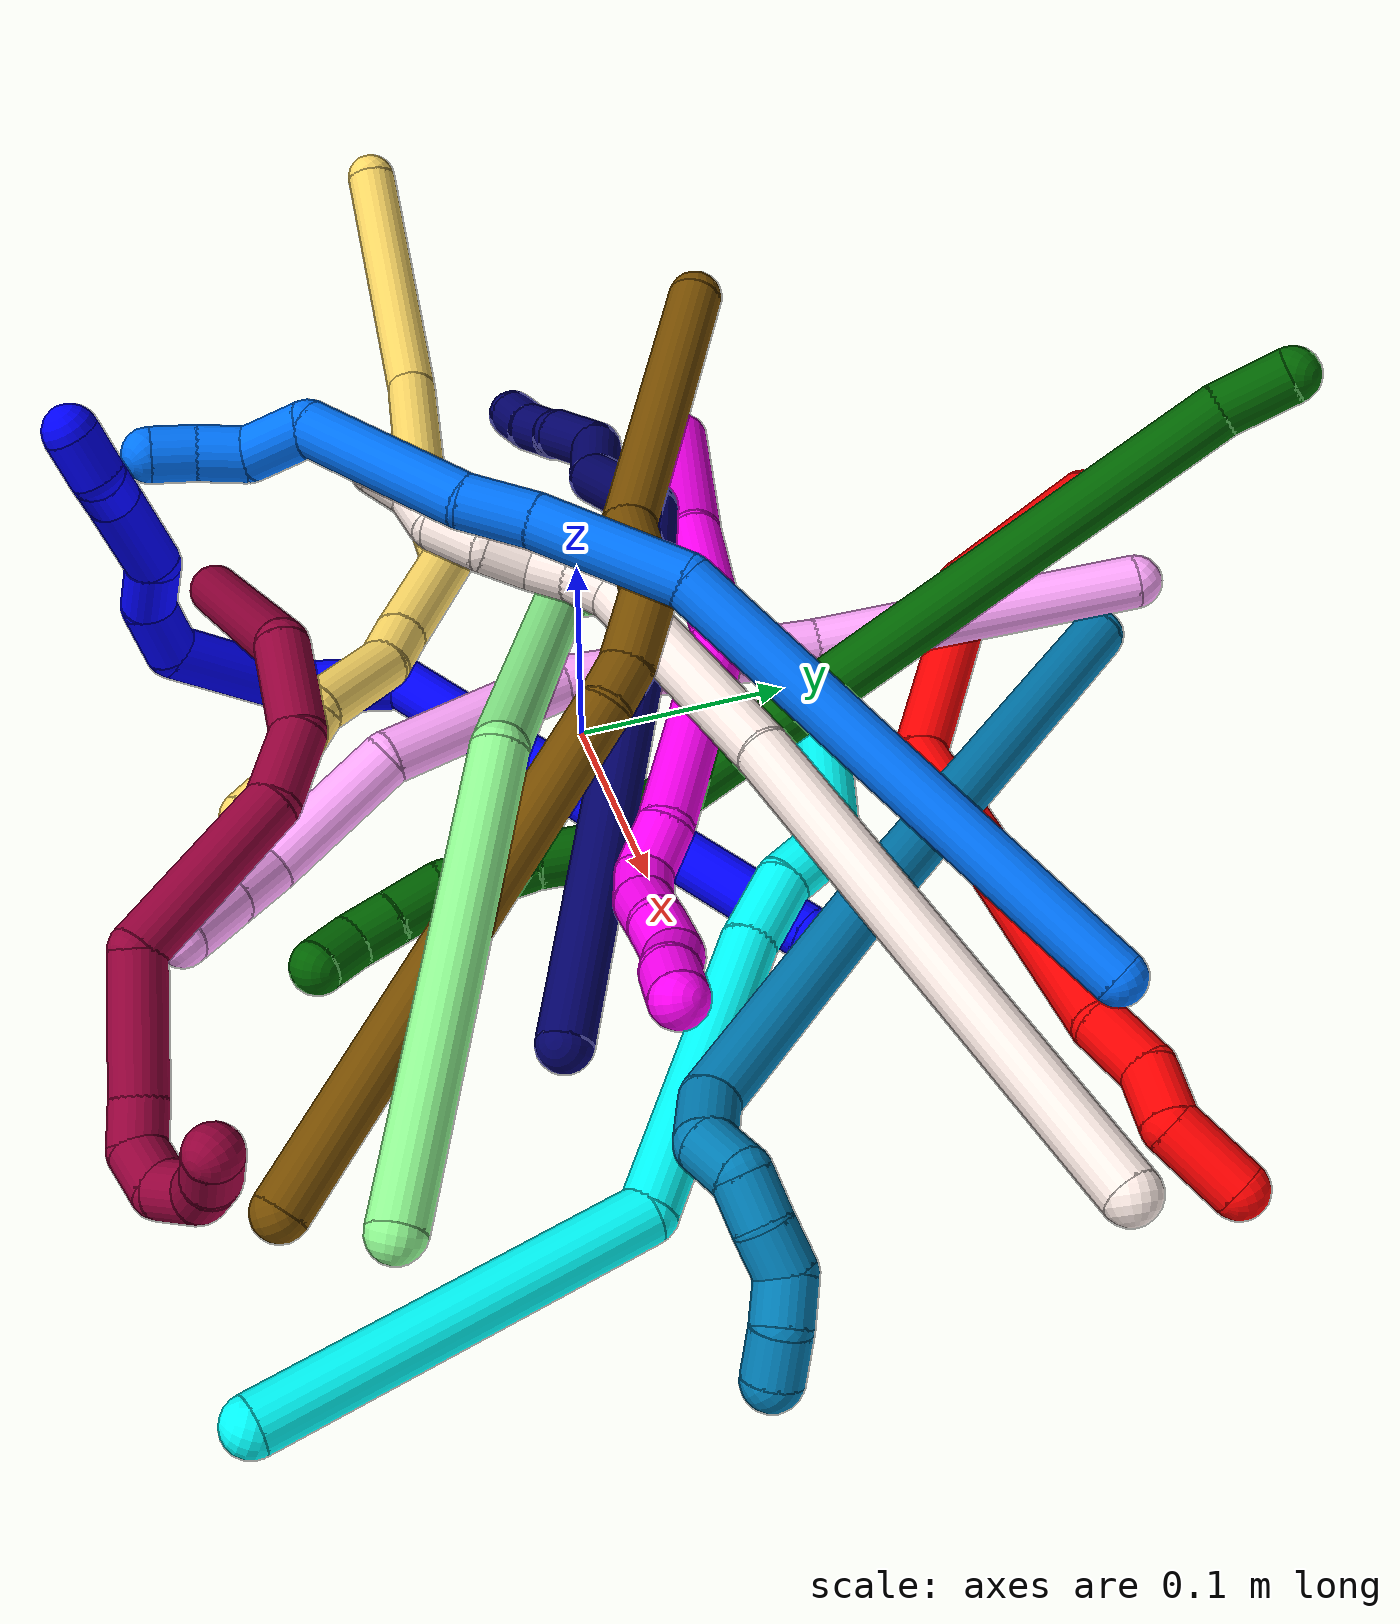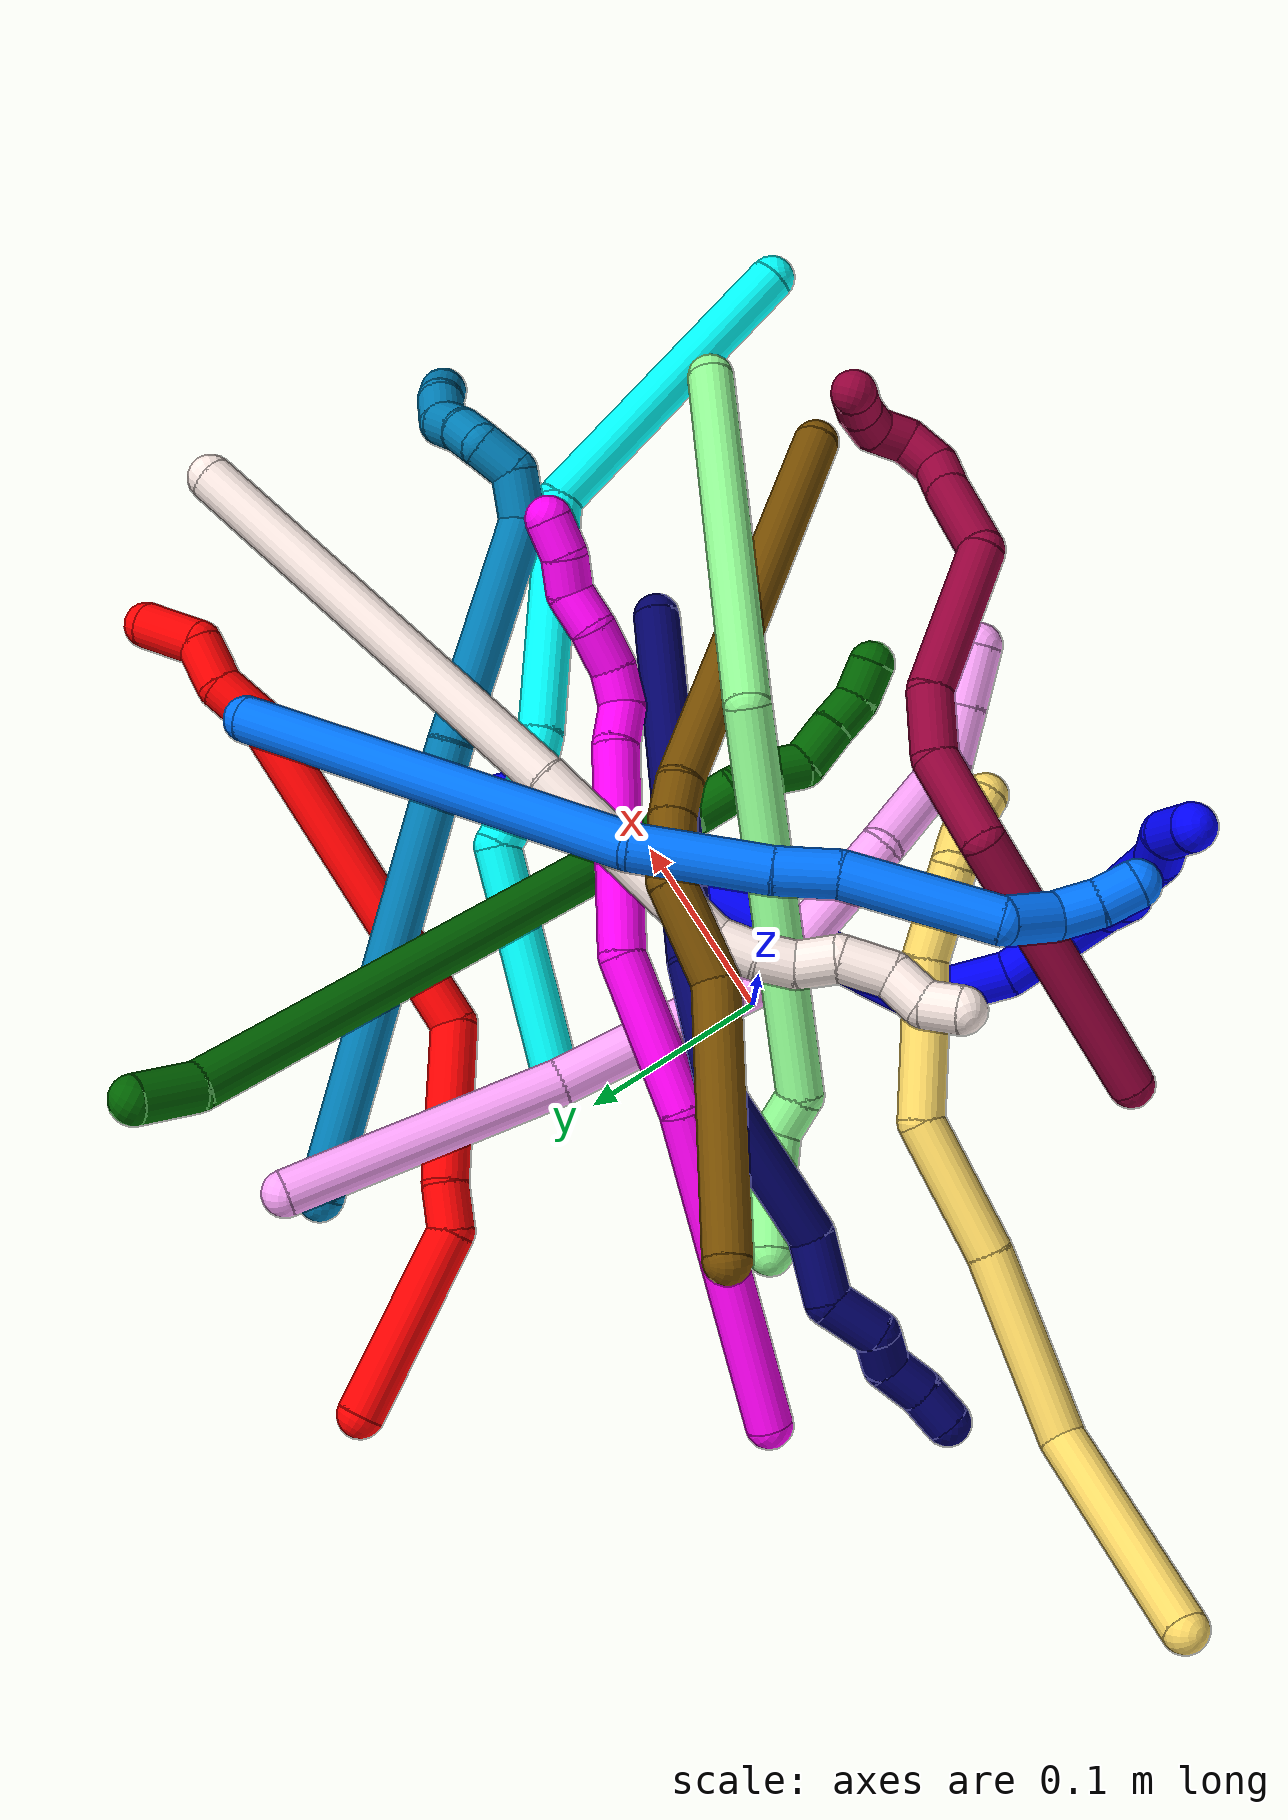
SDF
<sdf version="1.7">
 <world name="default">
  <plugin name="TubeGeneratorPlugin" filename="libtube_generator_plugin.so"/>
  <model name="photoneo_s_sensor">
   <static>1</static>
   <pose>0 0 2 1.57079 1.57079 3.14159</pose>
   <link name="link">
    <inertial><mass>0.1</mass></inertial>
    <sensor name="sensor" type="depth">
     <update_rate>30</update_rate>
     <camera>
      <horizontal_fov>1.22</horizontal_fov>
      <image><width>1920</width><height>1200</height><format>B8G8R8</format></image>
      <clip><near>0.1</near><far>4</far></clip>
      <depth_camera><output>points</output></depth_camera>
     </camera>
     <plugin name="camera_plugin" filename="libgazebo_ros_depth_camera.so">
      <baseline>0.2</baseline>
      <alwaysOn>1</alwaysOn>
      <updateRate>0.0</updateRate>
      <cameraName>camera_ir</cameraName>
      <imageTopicName>/camera/color/image_raw</imageTopicName>
      <cameraInfoTopicName>/camera/color/camera_info</cameraInfoTopicName>
      <depthImageTopicName>/camera/depth/image_raw</depthImageTopicName>
      <depthImageCameraInfoTopicName>/camera/depth/camera_info</depthImageCameraInfoTopicName>
      <pointCloudTopicName>/camera/depth/points</pointCloudTopicName>
      <frameName>fr_optical</frameName>
      <pointCloudCutoff>0.1</pointCloudCutoff>
      <pointCloudCutoffMax>2.0</pointCloudCutoffMax>
      <distortionK1>0</distortionK1>
      <distortionK2>0</distortionK2>
      <distortionK3>0</distortionK3>
      <distortionT1>0</distortionT1>
      <distortionT2>0</distortionT2>
      <CxPrime>0</CxPrime>
      <Cx>0</Cx>
      <Cy>0</Cy>
      <focalLength>0</focalLength>
      <hackBaseline>0</hackBaseline>
     </plugin>
    </sensor>
   </link>
  </model>
  <gravity>0 0 -9.8</gravity>
  <magnetic_field>6e-06 2.3e-05 -4.2e-05</magnetic_field>
  <atmosphere type="adiabatic"/>
  <physics name="default_physics" default="0" type="ode">
   <max_step_size>0.003</max_step_size>
   <real_time_factor>1</real_time_factor>
   <real_time_update_rate>1000</real_time_update_rate>
   <max_contacts>10000</max_contacts>
   <ode>
    <solver>
     <type>quick</type>
     <iters>100</iters>
     <sor>1.3</sor>
     <use_dynamic_moi_rescaling>0</use_dynamic_moi_rescaling>
    </solver>
    <constraints>
     <contact_max_correcting_vel>0</contact_max_correcting_vel>
     <contact_surface_layer>0.001</contact_surface_layer>
     <cfm>0</cfm>
     <erp>0.2</erp>
    </constraints>
   </ode>
  </physics>
  <scene><ambient>0.4 0.4 0.4 1</ambient><background>0.7 0.7 0.7 1</background><shadows>0</shadows></scene>
  <audio><device>default</device></audio>
  <spherical_coordinates>
   <surface_model>EARTH_WGS84</surface_model>
   <latitude_deg>0</latitude_deg>
   <longitude_deg>0</longitude_deg>
   <elevation>0</elevation>
   <heading_deg>0</heading_deg>
  </spherical_coordinates>
  <model name="bin">
   <static>1</static>
   <link name="bottom">
    <collision name="collision-bottom">
     <pose>0 0 -0.01 0 -0 0</pose>
     <geometry><box><size>0.8 0.6 0.02</size></box></geometry>
     <surface>
      <friction><ode><mu>100</mu><mu2>100</mu2></ode></friction>
      <contact><collide_bitmask>65535</collide_bitmask></contact>
     </surface>
    </collision>
   </link>
   <link name="west_wall">
    <collision name="collision-west_wall">
     <pose>-0.41 0 0.1 0 -0 0</pose>
     <geometry><box><size>0.02 0.6 0.2</size></box></geometry>
     <surface>
      <friction><ode><mu>100</mu><mu2>100</mu2></ode></friction>
      <contact><collide_bitmask>65535</collide_bitmask></contact>
     </surface>
    </collision>
   </link>
   <link name="east_wall">
    <collision name="collision-east_wall">
     <pose>0.41 0 0.1 0 -0 0</pose>
     <geometry><box><size>0.02 0.6 0.2</size></box></geometry>
     <surface>
      <friction><ode><mu>100</mu><mu2>100</mu2></ode></friction>
      <contact><collide_bitmask>65535</collide_bitmask></contact>
     </surface>
    </collision>
   </link>
   <link name="south_wall">
    <collision name="collision-south_wall">
     <pose>0 -0.31 0.1 0 -0 0</pose>
     <geometry><box><size>0.8 0.02 0.2</size></box></geometry>
     <surface>
      <friction><ode><mu>100</mu><mu2>100</mu2></ode></friction>
      <contact><collide_bitmask>65535</collide_bitmask></contact>
     </surface>
    </collision>
   </link>
   <link name="north_wall">
    <collision name="collision-north_wall">
     <pose>0 0.31 0.1 0 -0 0</pose>
     <geometry><box><size>0.8 0.02 0.2</size></box></geometry>
     <surface>
      <friction><ode><mu>100</mu><mu2>100</mu2></ode></friction>
      <contact><collide_bitmask>65535</collide_bitmask></contact>
     </surface>
    </collision>
   </link>
  </model>
  <model name="1">
   <static>0</static>
   <link name="1">
    <collision name="collision-cylinder-e_1_1_4">
     <pose>-0.065071 -0.043912 0.035939 0.884909 -0.853645 -0.424445</pose>
     <geometry><cylinder><radius>0.0125</radius><length>0.172674</length></cylinder></geometry>
     <surface>
      <friction><ode><mu>1.16</mu><mu2>1.16</mu2><slip1>0</slip1><slip2>0</slip2></ode></friction>
      <contact><ode><kp>1e+06</kp><kd>1</kd><max_vel>0</max_vel><min_depth>0.001</min_depth></ode></contact>
     </surface>
    </collision>
    <visual name="visual-cylinder-e_1_1_4">
     <pose>-0.065071 -0.043912 0.035939 0.884909 -0.853645 -0.424445</pose>
     <geometry><cylinder><radius>0.0125</radius><length>0.172674</length></cylinder></geometry>
     <material><ambient>0 0 1 1</ambient></material>
    </visual>
    <collision name="collision-cylinder-e_2_4_5">
     <pose>-0.158065 -0.10616 0.086165 0.90892 -0.876587 -0.450218</pose>
     <geometry><cylinder><radius>0.0125</radius><length>0.072666</length></cylinder></geometry>
     <surface>
      <friction><ode><mu>1.16</mu><mu2>1.16</mu2><slip1>0</slip1><slip2>0</slip2></ode></friction>
      <contact><ode><kp>1e+06</kp><kd>1</kd><max_vel>0</max_vel><min_depth>0.001</min_depth></ode></contact>
     </surface>
    </collision>
    <visual name="visual-cylinder-e_2_4_5">
     <pose>-0.158065 -0.10616 0.086165 0.90892 -0.876587 -0.450218</pose>
     <geometry><cylinder><radius>0.0125</radius><length>0.072666</length></cylinder></geometry>
     <material><ambient>0 0 1 1</ambient></material>
    </visual>
    <collision name="collision-cylinder-e_3_5_6">
     <pose>-0.190096 -0.14711 0.110109 1.16716 -0.165486 -0.109411</pose>
     <geometry><cylinder><radius>0.0125</radius><length>0.049859</length></cylinder></geometry>
     <surface>
      <friction><ode><mu>1.16</mu><mu2>1.16</mu2><slip1>0</slip1><slip2>0</slip2></ode></friction>
      <contact><ode><kp>1e+06</kp><kd>1</kd><max_vel>0</max_vel><min_depth>0.001</min_depth></ode></contact>
     </surface>
    </collision>
    <visual name="visual-cylinder-e_3_5_6">
     <pose>-0.190096 -0.14711 0.110109 1.16716 -0.165486 -0.109411</pose>
     <geometry><cylinder><radius>0.0125</radius><length>0.049859</length></cylinder></geometry>
     <material><ambient>0 0 1 1</ambient></material>
    </visual>
    <collision name="collision-cylinder-e_4_6_7">
     <pose>-0.187242 -0.188012 0.146076 0.607476 0.213919 0.067282</pose>
     <geometry><cylinder><radius>0.0125</radius><length>0.065577</length></cylinder></geometry>
     <surface>
      <friction><ode><mu>1.16</mu><mu2>1.16</mu2><slip1>0</slip1><slip2>0</slip2></ode></friction>
      <contact><ode><kp>1e+06</kp><kd>1</kd><max_vel>0</max_vel><min_depth>0.001</min_depth></ode></contact>
     </surface>
    </collision>
    <visual name="visual-cylinder-e_4_6_7">
     <pose>-0.187242 -0.188012 0.146076 0.607476 0.213919 0.067282</pose>
     <geometry><cylinder><radius>0.0125</radius><length>0.065577</length></cylinder></geometry>
     <material><ambient>0 0 1 1</ambient></material>
    </visual>
    <collision name="collision-cylinder-e_5_7_8">
     <pose>-0.178624 -0.204678 0.185979 -0.118835 0.120485 -0.007176</pose>
     <geometry><cylinder><radius>0.0125</radius><length>0.027582</length></cylinder></geometry>
     <surface>
      <friction><ode><mu>1.16</mu><mu2>1.16</mu2><slip1>0</slip1><slip2>0</slip2></ode></friction>
      <contact><ode><kp>1e+06</kp><kd>1</kd><max_vel>0</max_vel><min_depth>0.001</min_depth></ode></contact>
     </surface>
    </collision>
    <visual name="visual-cylinder-e_5_7_8">
     <pose>-0.178624 -0.204678 0.185979 -0.118835 0.120485 -0.007176</pose>
     <geometry><cylinder><radius>0.0125</radius><length>0.027582</length></cylinder></geometry>
     <material><ambient>0 0 1 1</ambient></material>
    </visual>
    <collision name="collision-cylinder-e_6_8_9">
     <pose>-0.172912 -0.195713 0.209962 -0.615234 0.308511 -0.098719</pose>
     <geometry><cylinder><radius>0.0125</radius><length>0.026703</length></cylinder></geometry>
     <surface>
      <friction><ode><mu>1.16</mu><mu2>1.16</mu2><slip1>0</slip1><slip2>0</slip2></ode></friction>
      <contact><ode><kp>1e+06</kp><kd>1</kd><max_vel>0</max_vel><min_depth>0.001</min_depth></ode></contact>
     </surface>
    </collision>
    <visual name="visual-cylinder-e_6_8_9">
     <pose>-0.172912 -0.195713 0.209962 -0.615234 0.308511 -0.098719</pose>
     <geometry><cylinder><radius>0.0125</radius><length>0.026703</length></cylinder></geometry>
     <material><ambient>0 0 1 1</ambient></material>
    </visual>
    <collision name="collision-cylinder-e_7_9_10">
     <pose>-0.163791 -0.18683 0.240585 -0.075981 0.244688 -0.009347</pose>
     <geometry><cylinder><radius>0.0125</radius><length>0.041834</length></cylinder></geometry>
     <surface>
      <friction><ode><mu>1.16</mu><mu2>1.16</mu2><slip1>0</slip1><slip2>0</slip2></ode></friction>
      <contact><ode><kp>1e+06</kp><kd>1</kd><max_vel>0</max_vel><min_depth>0.001</min_depth></ode></contact>
     </surface>
    </collision>
    <visual name="visual-cylinder-e_7_9_10">
     <pose>-0.163791 -0.18683 0.240585 -0.075981 0.244688 -0.009347</pose>
     <geometry><cylinder><radius>0.0125</radius><length>0.041834</length></cylinder></geometry>
     <material><ambient>0 0 1 1</ambient></material>
    </visual>
    <collision name="collision-cylinder-e_8_10_11">
     <pose>-0.153207 -0.184069 0.269203 -0.144642 0.577306 -0.043019</pose>
     <geometry><cylinder><radius>0.0125</radius><length>0.020218</length></cylinder></geometry>
     <surface>
      <friction><ode><mu>1.16</mu><mu2>1.16</mu2><slip1>0</slip1><slip2>0</slip2></ode></friction>
      <contact><ode><kp>1e+06</kp><kd>1</kd><max_vel>0</max_vel><min_depth>0.001</min_depth></ode></contact>
     </surface>
    </collision>
    <visual name="visual-cylinder-e_8_10_11">
     <pose>-0.153207 -0.184069 0.269203 -0.144642 0.577306 -0.043019</pose>
     <geometry><cylinder><radius>0.0125</radius><length>0.020218</length></cylinder></geometry>
     <material><ambient>0 0 1 1</ambient></material>
    </visual>
    <collision name="collision-cylinder-e_9_11_2">
     <pose>-0.147626 -0.182467 0.289022 -0.033286 0.00553 -9.2e-05</pose>
     <geometry><cylinder><radius>0.0125</radius><length>0.022888</length></cylinder></geometry>
     <surface>
      <friction><ode><mu>1.16</mu><mu2>1.16</mu2><slip1>0</slip1><slip2>0</slip2></ode></friction>
      <contact><ode><kp>1e+06</kp><kd>1</kd><max_vel>0</max_vel><min_depth>0.001</min_depth></ode></contact>
     </surface>
    </collision>
    <visual name="visual-cylinder-e_9_11_2">
     <pose>-0.147626 -0.182467 0.289022 -0.033286 0.00553 -9.2e-05</pose>
     <geometry><cylinder><radius>0.0125</radius><length>0.022888</length></cylinder></geometry>
     <material><ambient>0 0 1 1</ambient></material>
    </visual>
    <collision name="collision-sphere-2">
     <pose>-0.147563 -0.182086 0.30046 0 -0 0</pose>
     <geometry><sphere><radius>0.0125</radius></sphere></geometry>
     <surface>
      <friction><ode><mu>1.16</mu><mu2>1.16</mu2><slip1>0</slip1><slip2>0</slip2></ode></friction>
      <contact><ode><kp>1e+06</kp><kd>1</kd><max_vel>0</max_vel><min_depth>0.001</min_depth></ode></contact>
     </surface>
    </collision>
    <visual name="visual-sphere-2">
     <pose>-0.147563 -0.182086 0.30046 0 -0 0</pose>
     <geometry><sphere><radius>0.0125</radius></sphere></geometry>
     <material><ambient>0 0 1 1</ambient></material>
    </visual>
    <collision name="collision-sphere-11">
     <pose>-0.147689 -0.182848 0.277585 0 -0 0</pose>
     <geometry><sphere><radius>0.0125</radius></sphere></geometry>
     <surface>
      <friction><ode><mu>1.16</mu><mu2>1.16</mu2><slip1>0</slip1><slip2>0</slip2></ode></friction>
      <contact><ode><kp>1e+06</kp><kd>1</kd><max_vel>0</max_vel><min_depth>0.001</min_depth></ode></contact>
     </surface>
    </collision>
    <visual name="visual-sphere-11">
     <pose>-0.147689 -0.182848 0.277585 0 -0 0</pose>
     <geometry><sphere><radius>0.0125</radius></sphere></geometry>
     <material><ambient>0 0 1 1</ambient></material>
    </visual>
    <collision name="collision-sphere-10">
     <pose>-0.158724 -0.18529 0.260821 0 -0 0</pose>
     <geometry><sphere><radius>0.0125</radius></sphere></geometry>
     <surface>
      <friction><ode><mu>1.16</mu><mu2>1.16</mu2><slip1>0</slip1><slip2>0</slip2></ode></friction>
      <contact><ode><kp>1e+06</kp><kd>1</kd><max_vel>0</max_vel><min_depth>0.001</min_depth></ode></contact>
     </surface>
    </collision>
    <visual name="visual-sphere-10">
     <pose>-0.158724 -0.18529 0.260821 0 -0 0</pose>
     <geometry><sphere><radius>0.0125</radius></sphere></geometry>
     <material><ambient>0 0 1 1</ambient></material>
    </visual>
    <collision name="collision-sphere-9">
     <pose>-0.168858 -0.188371 0.22035 0 -0 0</pose>
     <geometry><sphere><radius>0.0125</radius></sphere></geometry>
     <surface>
      <friction><ode><mu>1.16</mu><mu2>1.16</mu2><slip1>0</slip1><slip2>0</slip2></ode></friction>
      <contact><ode><kp>1e+06</kp><kd>1</kd><max_vel>0</max_vel><min_depth>0.001</min_depth></ode></contact>
     </surface>
    </collision>
    <visual name="visual-sphere-9">
     <pose>-0.168858 -0.188371 0.22035 0 -0 0</pose>
     <geometry><sphere><radius>0.0125</radius></sphere></geometry>
     <material><ambient>0 0 1 1</ambient></material>
    </visual>
    <collision name="collision-sphere-4">
     <pose>-0.130141 -0.087824 0.071879 0 -0 0</pose>
     <geometry><sphere><radius>0.0125</radius></sphere></geometry>
     <surface>
      <friction><ode><mu>1.16</mu><mu2>1.16</mu2><slip1>0</slip1><slip2>0</slip2></ode></friction>
      <contact><ode><kp>1e+06</kp><kd>1</kd><max_vel>0</max_vel><min_depth>0.001</min_depth></ode></contact>
     </surface>
    </collision>
    <visual name="visual-sphere-4">
     <pose>-0.130141 -0.087824 0.071879 0 -0 0</pose>
     <geometry><sphere><radius>0.0125</radius></sphere></geometry>
     <material><ambient>0 0 1 1</ambient></material>
    </visual>
    <collision name="collision-sphere-1">
     <geometry><sphere><radius>0.0125</radius></sphere></geometry>
     <surface>
      <friction><ode><mu>1.16</mu><mu2>1.16</mu2><slip1>0</slip1><slip2>0</slip2></ode></friction>
      <contact><ode><kp>1e+06</kp><kd>1</kd><max_vel>0</max_vel><min_depth>0.001</min_depth></ode></contact>
     </surface>
    </collision>
    <visual name="visual-sphere-1">
     <geometry><sphere><radius>0.0125</radius></sphere></geometry>
     <material><ambient>0 0 1 1</ambient></material>
    </visual>
    <collision name="collision-sphere-8">
     <pose>-0.176966 -0.203055 0.199573 0 -0 0</pose>
     <geometry><sphere><radius>0.0125</radius></sphere></geometry>
     <surface>
      <friction><ode><mu>1.16</mu><mu2>1.16</mu2><slip1>0</slip1><slip2>0</slip2></ode></friction>
      <contact><ode><kp>1e+06</kp><kd>1</kd><max_vel>0</max_vel><min_depth>0.001</min_depth></ode></contact>
     </surface>
    </collision>
    <visual name="visual-sphere-8">
     <pose>-0.176966 -0.203055 0.199573 0 -0 0</pose>
     <geometry><sphere><radius>0.0125</radius></sphere></geometry>
     <material><ambient>0 0 1 1</ambient></material>
    </visual>
    <collision name="collision-sphere-5">
     <pose>-0.185989 -0.124497 0.100452 0 -0 0</pose>
     <geometry><sphere><radius>0.0125</radius></sphere></geometry>
     <surface>
      <friction><ode><mu>1.16</mu><mu2>1.16</mu2><slip1>0</slip1><slip2>0</slip2></ode></friction>
      <contact><ode><kp>1e+06</kp><kd>1</kd><max_vel>0</max_vel><min_depth>0.001</min_depth></ode></contact>
     </surface>
    </collision>
    <visual name="visual-sphere-5">
     <pose>-0.185989 -0.124497 0.100452 0 -0 0</pose>
     <geometry><sphere><radius>0.0125</radius></sphere></geometry>
     <material><ambient>0 0 1 1</ambient></material>
    </visual>
    <collision name="collision-sphere-6">
     <pose>-0.194203 -0.169723 0.119767 0 -0 0</pose>
     <geometry><sphere><radius>0.0125</radius></sphere></geometry>
     <surface>
      <friction><ode><mu>1.16</mu><mu2>1.16</mu2><slip1>0</slip1><slip2>0</slip2></ode></friction>
      <contact><ode><kp>1e+06</kp><kd>1</kd><max_vel>0</max_vel><min_depth>0.001</min_depth></ode></contact>
     </surface>
    </collision>
    <visual name="visual-sphere-6">
     <pose>-0.194203 -0.169723 0.119767 0 -0 0</pose>
     <geometry><sphere><radius>0.0125</radius></sphere></geometry>
     <material><ambient>0 0 1 1</ambient></material>
    </visual>
    <collision name="collision-sphere-7">
     <pose>-0.180281 -0.206301 0.172384 0 -0 0</pose>
     <geometry><sphere><radius>0.0125</radius></sphere></geometry>
     <surface>
      <friction><ode><mu>1.16</mu><mu2>1.16</mu2><slip1>0</slip1><slip2>0</slip2></ode></friction>
      <contact><ode><kp>1e+06</kp><kd>1</kd><max_vel>0</max_vel><min_depth>0.001</min_depth></ode></contact>
     </surface>
    </collision>
    <visual name="visual-sphere-7">
     <pose>-0.180281 -0.206301 0.172384 0 -0 0</pose>
     <geometry><sphere><radius>0.0125</radius></sphere></geometry>
     <material><ambient>0 0 1 1</ambient></material>
    </visual>
    <inertial>
     <pose>-0.134702 -0.123091 0.12079 0 -0 0</pose>
     <mass>0.5</mass>
     <inertia>
      <ixx>0.000195</ixx>
      <ixy>0</ixy>
      <ixz>0</ixz>
      <iyy>0.000285</iyy>
      <iyz>0</iyz>
      <izz>0.000634</izz>
     </inertia>
    </inertial>
   </link>
   <pose>0.165152 0.051519 0.011489 0.403933 -0.215258 -0.141239</pose>
  </model>
  <model name="2">
   <static>0</static>
   <link name="2">
    <collision name="collision-cylinder-e_1_1_4">
     <pose>0.003386 -0.002809 -0.052029 3.08766 0.064894 1.75495</pose>
     <geometry><cylinder><radius>0.0125</radius><length>0.104428</length></cylinder></geometry>
     <surface>
      <friction><ode><mu>1.16</mu><mu2>1.16</mu2><slip1>0</slip1><slip2>0</slip2></ode></friction>
      <contact><ode><kp>1e+06</kp><kd>1</kd><max_vel>0</max_vel><min_depth>0.001</min_depth></ode></contact>
     </surface>
    </collision>
    <visual name="visual-cylinder-e_1_1_4">
     <pose>0.003386 -0.002809 -0.052029 3.08766 0.064894 1.75495</pose>
     <geometry><cylinder><radius>0.0125</radius><length>0.104428</length></cylinder></geometry>
     <material><ambient>1 0 0 1</ambient></material>
    </visual>
    <collision name="collision-cylinder-e_2_4_5">
     <pose>0.013764 -0.009334 -0.11386 2.77918 0.588215 2.05358</pose>
     <geometry><cylinder><radius>0.0125</radius><length>0.025204</length></cylinder></geometry>
     <surface>
      <friction><ode><mu>1.16</mu><mu2>1.16</mu2><slip1>0</slip1><slip2>0</slip2></ode></friction>
      <contact><ode><kp>1e+06</kp><kd>1</kd><max_vel>0</max_vel><min_depth>0.001</min_depth></ode></contact>
     </surface>
    </collision>
    <visual name="visual-cylinder-e_2_4_5">
     <pose>0.013764 -0.009334 -0.11386 2.77918 0.588215 2.05358</pose>
     <geometry><cylinder><radius>0.0125</radius><length>0.025204</length></cylinder></geometry>
     <material><ambient>1 0 0 1</ambient></material>
    </visual>
    <collision name="collision-cylinder-e_3_5_6">
     <pose>0.042576 -0.016428 -0.160769 3.05083 0.529761 2.80983</pose>
     <geometry><cylinder><radius>0.0125</radius><length>0.086355</length></cylinder></geometry>
     <surface>
      <friction><ode><mu>1.16</mu><mu2>1.16</mu2><slip1>0</slip1><slip2>0</slip2></ode></friction>
      <contact><ode><kp>1e+06</kp><kd>1</kd><max_vel>0</max_vel><min_depth>0.001</min_depth></ode></contact>
     </surface>
    </collision>
    <visual name="visual-cylinder-e_3_5_6">
     <pose>0.042576 -0.016428 -0.160769 3.05083 0.529761 2.80983</pose>
     <geometry><cylinder><radius>0.0125</radius><length>0.086355</length></cylinder></geometry>
     <material><ambient>1 0 0 1</ambient></material>
    </visual>
    <collision name="collision-cylinder-e_4_6_7">
     <pose>0.134497 -0.068271 -0.240158 2.28817 0.828398 1.53722</pose>
     <geometry><cylinder><radius>0.0125</radius><length>0.190276</length></cylinder></geometry>
     <surface>
      <friction><ode><mu>1.16</mu><mu2>1.16</mu2><slip1>0</slip1><slip2>0</slip2></ode></friction>
      <contact><ode><kp>1e+06</kp><kd>1</kd><max_vel>0</max_vel><min_depth>0.001</min_depth></ode></contact>
     </surface>
    </collision>
    <visual name="visual-cylinder-e_4_6_7">
     <pose>0.134497 -0.068271 -0.240158 2.28817 0.828398 1.53722</pose>
     <geometry><cylinder><radius>0.0125</radius><length>0.190276</length></cylinder></geometry>
     <material><ambient>1 0 0 1</ambient></material>
    </visual>
    <collision name="collision-cylinder-e_5_7_8">
     <pose>0.217669 -0.123979 -0.285139 1.92741 1.03685 1.37519</pose>
     <geometry><cylinder><radius>0.0125</radius><length>0.030366</length></cylinder></geometry>
     <surface>
      <friction><ode><mu>1.16</mu><mu2>1.16</mu2><slip1>0</slip1><slip2>0</slip2></ode></friction>
      <contact><ode><kp>1e+06</kp><kd>1</kd><max_vel>0</max_vel><min_depth>0.001</min_depth></ode></contact>
     </surface>
    </collision>
    <visual name="visual-cylinder-e_5_7_8">
     <pose>0.217669 -0.123979 -0.285139 1.92741 1.03685 1.37519</pose>
     <geometry><cylinder><radius>0.0125</radius><length>0.030366</length></cylinder></geometry>
     <material><ambient>1 0 0 1</ambient></material>
    </visual>
    <collision name="collision-cylinder-e_6_8_9">
     <pose>0.241339 -0.135541 -0.295088 2.60415 0.898335 2.10349</pose>
     <geometry><cylinder><radius>0.0125</radius><length>0.027102</length></cylinder></geometry>
     <surface>
      <friction><ode><mu>1.16</mu><mu2>1.16</mu2><slip1>0</slip1><slip2>0</slip2></ode></friction>
      <contact><ode><kp>1e+06</kp><kd>1</kd><max_vel>0</max_vel><min_depth>0.001</min_depth></ode></contact>
     </surface>
    </collision>
    <visual name="visual-cylinder-e_6_8_9">
     <pose>0.241339 -0.135541 -0.295088 2.60415 0.898335 2.10349</pose>
     <geometry><cylinder><radius>0.0125</radius><length>0.027102</length></cylinder></geometry>
     <material><ambient>1 0 0 1</ambient></material>
    </visual>
    <collision name="collision-cylinder-e_7_9_2">
     <pose>0.269812 -0.142024 -0.300155 0.780209 1.40053 0.667138</pose>
     <geometry><cylinder><radius>0.0125</radius><length>0.036269</length></cylinder></geometry>
     <surface>
      <friction><ode><mu>1.16</mu><mu2>1.16</mu2><slip1>0</slip1><slip2>0</slip2></ode></friction>
      <contact><ode><kp>1e+06</kp><kd>1</kd><max_vel>0</max_vel><min_depth>0.001</min_depth></ode></contact>
     </surface>
    </collision>
    <visual name="visual-cylinder-e_7_9_2">
     <pose>0.269812 -0.142024 -0.300155 0.780209 1.40053 0.667138</pose>
     <geometry><cylinder><radius>0.0125</radius><length>0.036269</length></cylinder></geometry>
     <material><ambient>1 0 0 1</ambient></material>
    </visual>
    <collision name="collision-sphere-2">
     <pose>0.287685 -0.144185 -0.297971 0 -0 0</pose>
     <geometry><sphere><radius>0.0125</radius></sphere></geometry>
     <surface>
      <friction><ode><mu>1.16</mu><mu2>1.16</mu2><slip1>0</slip1><slip2>0</slip2></ode></friction>
      <contact><ode><kp>1e+06</kp><kd>1</kd><max_vel>0</max_vel><min_depth>0.001</min_depth></ode></contact>
     </surface>
    </collision>
    <visual name="visual-sphere-2">
     <pose>0.287685 -0.144185 -0.297971 0 -0 0</pose>
     <geometry><sphere><radius>0.0125</radius></sphere></geometry>
     <material><ambient>1 0 0 1</ambient></material>
    </visual>
    <collision name="collision-sphere-9">
     <pose>0.25194 -0.139863 -0.302339 0 -0 0</pose>
     <geometry><sphere><radius>0.0125</radius></sphere></geometry>
     <surface>
      <friction><ode><mu>1.16</mu><mu2>1.16</mu2><slip1>0</slip1><slip2>0</slip2></ode></friction>
      <contact><ode><kp>1e+06</kp><kd>1</kd><max_vel>0</max_vel><min_depth>0.001</min_depth></ode></contact>
     </surface>
    </collision>
    <visual name="visual-sphere-9">
     <pose>0.25194 -0.139863 -0.302339 0 -0 0</pose>
     <geometry><sphere><radius>0.0125</radius></sphere></geometry>
     <material><ambient>1 0 0 1</ambient></material>
    </visual>
    <collision name="collision-sphere-4">
     <pose>0.006772 -0.005617 -0.104057 0 -0 0</pose>
     <geometry><sphere><radius>0.0125</radius></sphere></geometry>
     <surface>
      <friction><ode><mu>1.16</mu><mu2>1.16</mu2><slip1>0</slip1><slip2>0</slip2></ode></friction>
      <contact><ode><kp>1e+06</kp><kd>1</kd><max_vel>0</max_vel><min_depth>0.001</min_depth></ode></contact>
     </surface>
    </collision>
    <visual name="visual-sphere-4">
     <pose>0.006772 -0.005617 -0.104057 0 -0 0</pose>
     <geometry><sphere><radius>0.0125</radius></sphere></geometry>
     <material><ambient>1 0 0 1</ambient></material>
    </visual>
    <collision name="collision-sphere-1">
     <geometry><sphere><radius>0.0125</radius></sphere></geometry>
     <surface>
      <friction><ode><mu>1.16</mu><mu2>1.16</mu2><slip1>0</slip1><slip2>0</slip2></ode></friction>
      <contact><ode><kp>1e+06</kp><kd>1</kd><max_vel>0</max_vel><min_depth>0.001</min_depth></ode></contact>
     </surface>
    </collision>
    <visual name="visual-sphere-1">
     <geometry><sphere><radius>0.0125</radius></sphere></geometry>
     <material><ambient>1 0 0 1</ambient></material>
    </visual>
    <collision name="collision-sphere-8">
     <pose>0.230739 -0.13122 -0.287837 0 -0 0</pose>
     <geometry><sphere><radius>0.0125</radius></sphere></geometry>
     <surface>
      <friction><ode><mu>1.16</mu><mu2>1.16</mu2><slip1>0</slip1><slip2>0</slip2></ode></friction>
      <contact><ode><kp>1e+06</kp><kd>1</kd><max_vel>0</max_vel><min_depth>0.001</min_depth></ode></contact>
     </surface>
    </collision>
    <visual name="visual-sphere-8">
     <pose>0.230739 -0.13122 -0.287837 0 -0 0</pose>
     <geometry><sphere><radius>0.0125</radius></sphere></geometry>
     <material><ambient>1 0 0 1</ambient></material>
    </visual>
    <collision name="collision-sphere-5">
     <pose>0.020757 -0.013051 -0.123663 0 -0 0</pose>
     <geometry><sphere><radius>0.0125</radius></sphere></geometry>
     <surface>
      <friction><ode><mu>1.16</mu><mu2>1.16</mu2><slip1>0</slip1><slip2>0</slip2></ode></friction>
      <contact><ode><kp>1e+06</kp><kd>1</kd><max_vel>0</max_vel><min_depth>0.001</min_depth></ode></contact>
     </surface>
    </collision>
    <visual name="visual-sphere-5">
     <pose>0.020757 -0.013051 -0.123663 0 -0 0</pose>
     <geometry><sphere><radius>0.0125</radius></sphere></geometry>
     <material><ambient>1 0 0 1</ambient></material>
    </visual>
    <collision name="collision-sphere-6">
     <pose>0.064394 -0.019805 -0.197874 0 -0 0</pose>
     <geometry><sphere><radius>0.0125</radius></sphere></geometry>
     <surface>
      <friction><ode><mu>1.16</mu><mu2>1.16</mu2><slip1>0</slip1><slip2>0</slip2></ode></friction>
      <contact><ode><kp>1e+06</kp><kd>1</kd><max_vel>0</max_vel><min_depth>0.001</min_depth></ode></contact>
     </surface>
    </collision>
    <visual name="visual-sphere-6">
     <pose>0.064394 -0.019805 -0.197874 0 -0 0</pose>
     <geometry><sphere><radius>0.0125</radius></sphere></geometry>
     <material><ambient>1 0 0 1</ambient></material>
    </visual>
    <collision name="collision-sphere-7">
     <pose>0.204599 -0.116738 -0.282442 0 -0 0</pose>
     <geometry><sphere><radius>0.0125</radius></sphere></geometry>
     <surface>
      <friction><ode><mu>1.16</mu><mu2>1.16</mu2><slip1>0</slip1><slip2>0</slip2></ode></friction>
      <contact><ode><kp>1e+06</kp><kd>1</kd><max_vel>0</max_vel><min_depth>0.001</min_depth></ode></contact>
     </surface>
    </collision>
    <visual name="visual-sphere-7">
     <pose>0.204599 -0.116738 -0.282442 0 -0 0</pose>
     <geometry><sphere><radius>0.0125</radius></sphere></geometry>
     <material><ambient>1 0 0 1</ambient></material>
    </visual>
    <inertial>
     <pose>0.10581 -0.055054 -0.190849 0 -0 0</pose>
     <mass>0.5</mass>
     <inertia>
      <ixx>0.000482</ixx>
      <ixy>0</ixy>
      <ixz>0</ixz>
      <iyy>0.000895</iyy>
      <iyz>0</iyz>
      <izz>-0.000189</izz>
     </inertia>
    </inertial>
   </link>
   <pose>-0.072103 0.287745 0.018492 -1.6179 0.523692 0.438265</pose>
  </model>
  <model name="3">
   <static>0</static>
   <link name="3">
    <collision name="collision-cylinder-e_1_1_4">
     <pose>-0.030642 0.047028 -0.065267 -2.51721 -0.36394 1.03632</pose>
     <geometry><cylinder><radius>0.0125</radius><length>0.172167</length></cylinder></geometry>
     <surface>
      <friction><ode><mu>1.16</mu><mu2>1.16</mu2><slip1>0</slip1><slip2>0</slip2></ode></friction>
      <contact><ode><kp>1e+06</kp><kd>1</kd><max_vel>0</max_vel><min_depth>0.001</min_depth></ode></contact>
     </surface>
    </collision>
    <visual name="visual-cylinder-e_1_1_4">
     <pose>-0.030642 0.047028 -0.065267 -2.51721 -0.36394 1.03632</pose>
     <geometry><cylinder><radius>0.0125</radius><length>0.172167</length></cylinder></geometry>
     <material><ambient>0.003922 1 0.996078 1</ambient></material>
    </visual>
    <collision name="collision-cylinder-e_2_4_5">
     <pose>-0.110341 0.1388 -0.144835 -1.88016 -0.807086 1.05823</pose>
     <geometry><cylinder><radius>0.0125</radius><length>0.135839</length></cylinder></geometry>
     <surface>
      <friction><ode><mu>1.16</mu><mu2>1.16</mu2><slip1>0</slip1><slip2>0</slip2></ode></friction>
      <contact><ode><kp>1e+06</kp><kd>1</kd><max_vel>0</max_vel><min_depth>0.001</min_depth></ode></contact>
     </surface>
    </collision>
    <visual name="visual-cylinder-e_2_4_5">
     <pose>-0.110341 0.1388 -0.144835 -1.88016 -0.807086 1.05823</pose>
     <geometry><cylinder><radius>0.0125</radius><length>0.135839</length></cylinder></geometry>
     <material><ambient>0.003922 1 0.996078 1</ambient></material>
    </visual>
    <collision name="collision-cylinder-e_3_5_6">
     <pose>-0.170704 0.19571 -0.164805 -2.00684 -0.700065 1.04044</pose>
     <geometry><cylinder><radius>0.0125</radius><length>0.035101</length></cylinder></geometry>
     <surface>
      <friction><ode><mu>1.16</mu><mu2>1.16</mu2><slip1>0</slip1><slip2>0</slip2></ode></friction>
      <contact><ode><kp>1e+06</kp><kd>1</kd><max_vel>0</max_vel><min_depth>0.001</min_depth></ode></contact>
     </surface>
    </collision>
    <visual name="visual-cylinder-e_3_5_6">
     <pose>-0.170704 0.19571 -0.164805 -2.00684 -0.700065 1.04044</pose>
     <geometry><cylinder><radius>0.0125</radius><length>0.035101</length></cylinder></geometry>
     <material><ambient>0.003922 1 0.996078 1</ambient></material>
    </visual>
    <collision name="collision-cylinder-e_4_6_7">
     <pose>-0.190387 0.217385 -0.179982 -2.35612 -0.557047 1.20836</pose>
     <geometry><cylinder><radius>0.0125</radius><length>0.031683</length></cylinder></geometry>
     <surface>
      <friction><ode><mu>1.16</mu><mu2>1.16</mu2><slip1>0</slip1><slip2>0</slip2></ode></friction>
      <contact><ode><kp>1e+06</kp><kd>1</kd><max_vel>0</max_vel><min_depth>0.001</min_depth></ode></contact>
     </surface>
    </collision>
    <visual name="visual-cylinder-e_4_6_7">
     <pose>-0.190387 0.217385 -0.179982 -2.35612 -0.557047 1.20836</pose>
     <geometry><cylinder><radius>0.0125</radius><length>0.031683</length></cylinder></geometry>
     <material><ambient>0.003922 1 0.996078 1</ambient></material>
    </visual>
    <collision name="collision-cylinder-e_5_7_2">
     <pose>-0.257874 0.247451 -0.191091 -1.64857 -1.23518 1.30957</pose>
     <geometry><cylinder><radius>0.0125</radius><length>0.12521</length></cylinder></geometry>
     <surface>
      <friction><ode><mu>1.16</mu><mu2>1.16</mu2><slip1>0</slip1><slip2>0</slip2></ode></friction>
      <contact><ode><kp>1e+06</kp><kd>1</kd><max_vel>0</max_vel><min_depth>0.001</min_depth></ode></contact>
     </surface>
    </collision>
    <visual name="visual-cylinder-e_5_7_2">
     <pose>-0.257874 0.247451 -0.191091 -1.64857 -1.23518 1.30957</pose>
     <geometry><cylinder><radius>0.0125</radius><length>0.12521</length></cylinder></geometry>
     <material><ambient>0.003922 1 0.996078 1</ambient></material>
    </visual>
    <collision name="collision-sphere-2">
     <pose>-0.316987 0.268008 -0.192693 0 -0 0</pose>
     <geometry><sphere><radius>0.0125</radius></sphere></geometry>
     <surface>
      <friction><ode><mu>1.16</mu><mu2>1.16</mu2><slip1>0</slip1><slip2>0</slip2></ode></friction>
      <contact><ode><kp>1e+06</kp><kd>1</kd><max_vel>0</max_vel><min_depth>0.001</min_depth></ode></contact>
     </surface>
    </collision>
    <visual name="visual-sphere-2">
     <pose>-0.316987 0.268008 -0.192693 0 -0 0</pose>
     <geometry><sphere><radius>0.0125</radius></sphere></geometry>
     <material><ambient>0.003922 1 0.996078 1</ambient></material>
    </visual>
    <collision name="collision-sphere-7">
     <pose>-0.198762 0.226894 -0.189489 0 -0 0</pose>
     <geometry><sphere><radius>0.0125</radius></sphere></geometry>
     <surface>
      <friction><ode><mu>1.16</mu><mu2>1.16</mu2><slip1>0</slip1><slip2>0</slip2></ode></friction>
      <contact><ode><kp>1e+06</kp><kd>1</kd><max_vel>0</max_vel><min_depth>0.001</min_depth></ode></contact>
     </surface>
    </collision>
    <visual name="visual-sphere-7">
     <pose>-0.198762 0.226894 -0.189489 0 -0 0</pose>
     <geometry><sphere><radius>0.0125</radius></sphere></geometry>
     <material><ambient>0.003922 1 0.996078 1</ambient></material>
    </visual>
    <collision name="collision-sphere-6">
     <pose>-0.182012 0.207876 -0.170474 0 -0 0</pose>
     <geometry><sphere><radius>0.0125</radius></sphere></geometry>
     <surface>
      <friction><ode><mu>1.16</mu><mu2>1.16</mu2><slip1>0</slip1><slip2>0</slip2></ode></friction>
      <contact><ode><kp>1e+06</kp><kd>1</kd><max_vel>0</max_vel><min_depth>0.001</min_depth></ode></contact>
     </surface>
    </collision>
    <visual name="visual-sphere-6">
     <pose>-0.182012 0.207876 -0.170474 0 -0 0</pose>
     <geometry><sphere><radius>0.0125</radius></sphere></geometry>
     <material><ambient>0.003922 1 0.996078 1</ambient></material>
    </visual>
    <collision name="collision-sphere-5">
     <pose>-0.159397 0.183543 -0.159136 0 -0 0</pose>
     <geometry><sphere><radius>0.0125</radius></sphere></geometry>
     <surface>
      <friction><ode><mu>1.16</mu><mu2>1.16</mu2><slip1>0</slip1><slip2>0</slip2></ode></friction>
      <contact><ode><kp>1e+06</kp><kd>1</kd><max_vel>0</max_vel><min_depth>0.001</min_depth></ode></contact>
     </surface>
    </collision>
    <visual name="visual-sphere-5">
     <pose>-0.159397 0.183543 -0.159136 0 -0 0</pose>
     <geometry><sphere><radius>0.0125</radius></sphere></geometry>
     <material><ambient>0.003922 1 0.996078 1</ambient></material>
    </visual>
    <collision name="collision-sphere-1">
     <geometry><sphere><radius>0.0125</radius></sphere></geometry>
     <surface>
      <friction><ode><mu>1.16</mu><mu2>1.16</mu2><slip1>0</slip1><slip2>0</slip2></ode></friction>
      <contact><ode><kp>1e+06</kp><kd>1</kd><max_vel>0</max_vel><min_depth>0.001</min_depth></ode></contact>
     </surface>
    </collision>
    <visual name="visual-sphere-1">
     <geometry><sphere><radius>0.0125</radius></sphere></geometry>
     <material><ambient>0.003922 1 0.996078 1</ambient></material>
    </visual>
    <collision name="collision-sphere-4">
     <pose>-0.061284 0.094056 -0.130534 0 -0 0</pose>
     <geometry><sphere><radius>0.0125</radius></sphere></geometry>
     <surface>
      <friction><ode><mu>1.16</mu><mu2>1.16</mu2><slip1>0</slip1><slip2>0</slip2></ode></friction>
      <contact><ode><kp>1e+06</kp><kd>1</kd><max_vel>0</max_vel><min_depth>0.001</min_depth></ode></contact>
     </surface>
    </collision>
    <visual name="visual-sphere-4">
     <pose>-0.061284 0.094056 -0.130534 0 -0 0</pose>
     <geometry><sphere><radius>0.0125</radius></sphere></geometry>
     <material><ambient>0.003922 1 0.996078 1</ambient></material>
    </visual>
    <inertial>
     <pose>-0.129153 0.143383 -0.13265 0 -0 0</pose>
     <mass>0.5</mass>
     <inertia><ixx>0.000807</ixx><ixy>0</ixy><ixz>0</ixz><iyy>0.000704</iyy><iyz>0</iyz><izz>2e-05</izz></inertia>
    </inertial>
   </link>
   <pose>0.332149 -0.227301 0.011395 1.16739 -0.488312 -0.161545</pose>
  </model>
  <model name="4">
   <static>0</static>
   <link name="4">
    <collision name="collision-cylinder-e_1_1_4">
     <pose>0.016629 -0.065666 0.034989 1.08123 0.219874 0.132323</pose>
     <geometry><cylinder><radius>0.0125</radius><length>0.152484</length></cylinder></geometry>
     <surface>
      <friction><ode><mu>1.16</mu><mu2>1.16</mu2><slip1>0</slip1><slip2>0</slip2></ode></friction>
      <contact><ode><kp>1e+06</kp><kd>1</kd><max_vel>0</max_vel><min_depth>0.001</min_depth></ode></contact>
     </surface>
    </collision>
    <visual name="visual-cylinder-e_1_1_4">
     <pose>0.016629 -0.065666 0.034989 1.08123 0.219874 0.132323</pose>
     <geometry><cylinder><radius>0.0125</radius><length>0.152484</length></cylinder></geometry>
     <material><ambient>1 0.65098 0.996078 1</ambient></material>
    </visual>
    <collision name="collision-cylinder-e_2_4_5">
     <pose>0.053166 -0.178994 0.100837 0.996219 0.337235 0.184637</pose>
     <geometry><cylinder><radius>0.0125</radius><length>0.120335</length></cylinder></geometry>
     <surface>
      <friction><ode><mu>1.16</mu><mu2>1.16</mu2><slip1>0</slip1><slip2>0</slip2></ode></friction>
      <contact><ode><kp>1e+06</kp><kd>1</kd><max_vel>0</max_vel><min_depth>0.001</min_depth></ode></contact>
     </surface>
    </collision>
    <visual name="visual-cylinder-e_2_4_5">
     <pose>0.053166 -0.178994 0.100837 0.996219 0.337235 0.184637</pose>
     <geometry><cylinder><radius>0.0125</radius><length>0.120335</length></cylinder></geometry>
     <material><ambient>1 0.65098 0.996078 1</ambient></material>
    </visual>
    <collision name="collision-cylinder-e_3_5_6">
     <pose>0.102259 -0.26009 0.144552 1.20369 0.683653 0.479357</pose>
     <geometry><cylinder><radius>0.0125</radius><length>0.092411</length></cylinder></geometry>
     <surface>
      <friction><ode><mu>1.16</mu><mu2>1.16</mu2><slip1>0</slip1><slip2>0</slip2></ode></friction>
      <contact><ode><kp>1e+06</kp><kd>1</kd><max_vel>0</max_vel><min_depth>0.001</min_depth></ode></contact>
     </surface>
    </collision>
    <visual name="visual-cylinder-e_3_5_6">
     <pose>0.102259 -0.26009 0.144552 1.20369 0.683653 0.479357</pose>
     <geometry><cylinder><radius>0.0125</radius><length>0.092411</length></cylinder></geometry>
     <material><ambient>1 0.65098 0.996078 1</ambient></material>
    </visual>
    <collision name="collision-cylinder-e_4_6_7">
     <pose>0.14626 -0.325043 0.155142 1.64258 0.438446 0.469954</pose>
     <geometry><cylinder><radius>0.0125</radius><length>0.069802</length></cylinder></geometry>
     <surface>
      <friction><ode><mu>1.16</mu><mu2>1.16</mu2><slip1>0</slip1><slip2>0</slip2></ode></friction>
      <contact><ode><kp>1e+06</kp><kd>1</kd><max_vel>0</max_vel><min_depth>0.001</min_depth></ode></contact>
     </surface>
    </collision>
    <visual name="visual-cylinder-e_4_6_7">
     <pose>0.14626 -0.325043 0.155142 1.64258 0.438446 0.469954</pose>
     <geometry><cylinder><radius>0.0125</radius><length>0.069802</length></cylinder></geometry>
     <material><ambient>1 0.65098 0.996078 1</ambient></material>
    </visual>
    <collision name="collision-cylinder-e_5_7_8">
     <pose>0.175543 -0.362832 0.153746 1.43291 1.1583 1.03534</pose>
     <geometry><cylinder><radius>0.0125</radius><length>0.031581</length></cylinder></geometry>
     <surface>
      <friction><ode><mu>1.16</mu><mu2>1.16</mu2><slip1>0</slip1><slip2>0</slip2></ode></friction>
      <contact><ode><kp>1e+06</kp><kd>1</kd><max_vel>0</max_vel><min_depth>0.001</min_depth></ode></contact>
     </surface>
    </collision>
    <visual name="visual-cylinder-e_5_7_8">
     <pose>0.175543 -0.362832 0.153746 1.43291 1.1583 1.03534</pose>
     <geometry><cylinder><radius>0.0125</radius><length>0.031581</length></cylinder></geometry>
     <material><ambient>1 0.65098 0.996078 1</ambient></material>
    </visual>
    <collision name="collision-cylinder-e_6_8_2">
     <pose>0.205303 -0.37573 0.155534 1.43321 1.15838 1.03568</pose>
     <geometry><cylinder><radius>0.0125</radius><length>0.033387</length></cylinder></geometry>
     <surface>
      <friction><ode><mu>1.16</mu><mu2>1.16</mu2><slip1>0</slip1><slip2>0</slip2></ode></friction>
      <contact><ode><kp>1e+06</kp><kd>1</kd><max_vel>0</max_vel><min_depth>0.001</min_depth></ode></contact>
     </surface>
    </collision>
    <visual name="visual-cylinder-e_6_8_2">
     <pose>0.205303 -0.37573 0.155534 1.43321 1.15838 1.03568</pose>
     <geometry><cylinder><radius>0.0125</radius><length>0.033387</length></cylinder></geometry>
     <material><ambient>1 0.65098 0.996078 1</ambient></material>
    </visual>
    <collision name="collision-sphere-2">
     <pose>0.220597 -0.382358 0.156452 0 -0 0</pose>
     <geometry><sphere><radius>0.0125</radius></sphere></geometry>
     <surface>
      <friction><ode><mu>1.16</mu><mu2>1.16</mu2><slip1>0</slip1><slip2>0</slip2></ode></friction>
      <contact><ode><kp>1e+06</kp><kd>1</kd><max_vel>0</max_vel><min_depth>0.001</min_depth></ode></contact>
     </surface>
    </collision>
    <visual name="visual-sphere-2">
     <pose>0.220597 -0.382358 0.156452 0 -0 0</pose>
     <geometry><sphere><radius>0.0125</radius></sphere></geometry>
     <material><ambient>1 0.65098 0.996078 1</ambient></material>
    </visual>
    <collision name="collision-sphere-4">
     <pose>0.033258 -0.131333 0.069979 0 -0 0</pose>
     <geometry><sphere><radius>0.0125</radius></sphere></geometry>
     <surface>
      <friction><ode><mu>1.16</mu><mu2>1.16</mu2><slip1>0</slip1><slip2>0</slip2></ode></friction>
      <contact><ode><kp>1e+06</kp><kd>1</kd><max_vel>0</max_vel><min_depth>0.001</min_depth></ode></contact>
     </surface>
    </collision>
    <visual name="visual-sphere-4">
     <pose>0.033258 -0.131333 0.069979 0 -0 0</pose>
     <geometry><sphere><radius>0.0125</radius></sphere></geometry>
     <material><ambient>1 0.65098 0.996078 1</ambient></material>
    </visual>
    <collision name="collision-sphere-1">
     <geometry><sphere><radius>0.0125</radius></sphere></geometry>
     <surface>
      <friction><ode><mu>1.16</mu><mu2>1.16</mu2><slip1>0</slip1><slip2>0</slip2></ode></friction>
      <contact><ode><kp>1e+06</kp><kd>1</kd><max_vel>0</max_vel><min_depth>0.001</min_depth></ode></contact>
     </surface>
    </collision>
    <visual name="visual-sphere-1">
     <geometry><sphere><radius>0.0125</radius></sphere></geometry>
     <material><ambient>1 0.65098 0.996078 1</ambient></material>
    </visual>
    <collision name="collision-sphere-8">
     <pose>0.190009 -0.369102 0.154616 0 -0 0</pose>
     <geometry><sphere><radius>0.0125</radius></sphere></geometry>
     <surface>
      <friction><ode><mu>1.16</mu><mu2>1.16</mu2><slip1>0</slip1><slip2>0</slip2></ode></friction>
      <contact><ode><kp>1e+06</kp><kd>1</kd><max_vel>0</max_vel><min_depth>0.001</min_depth></ode></contact>
     </surface>
    </collision>
    <visual name="visual-sphere-8">
     <pose>0.190009 -0.369102 0.154616 0 -0 0</pose>
     <geometry><sphere><radius>0.0125</radius></sphere></geometry>
     <material><ambient>1 0.65098 0.996078 1</ambient></material>
    </visual>
    <collision name="collision-sphere-5">
     <pose>0.073074 -0.226655 0.131695 0 -0 0</pose>
     <geometry><sphere><radius>0.0125</radius></sphere></geometry>
     <surface>
      <friction><ode><mu>1.16</mu><mu2>1.16</mu2><slip1>0</slip1><slip2>0</slip2></ode></friction>
      <contact><ode><kp>1e+06</kp><kd>1</kd><max_vel>0</max_vel><min_depth>0.001</min_depth></ode></contact>
     </surface>
    </collision>
    <visual name="visual-sphere-5">
     <pose>0.073074 -0.226655 0.131695 0 -0 0</pose>
     <geometry><sphere><radius>0.0125</radius></sphere></geometry>
     <material><ambient>1 0.65098 0.996078 1</ambient></material>
    </visual>
    <collision name="collision-sphere-6">
     <pose>0.131443 -0.293525 0.157409 0 -0 0</pose>
     <geometry><sphere><radius>0.0125</radius></sphere></geometry>
     <surface>
      <friction><ode><mu>1.16</mu><mu2>1.16</mu2><slip1>0</slip1><slip2>0</slip2></ode></friction>
      <contact><ode><kp>1e+06</kp><kd>1</kd><max_vel>0</max_vel><min_depth>0.001</min_depth></ode></contact>
     </surface>
    </collision>
    <visual name="visual-sphere-6">
     <pose>0.131443 -0.293525 0.157409 0 -0 0</pose>
     <geometry><sphere><radius>0.0125</radius></sphere></geometry>
     <material><ambient>1 0.65098 0.996078 1</ambient></material>
    </visual>
    <collision name="collision-sphere-7">
     <pose>0.161077 -0.356562 0.152876 0 -0 0</pose>
     <geometry><sphere><radius>0.0125</radius></sphere></geometry>
     <surface>
      <friction><ode><mu>1.16</mu><mu2>1.16</mu2><slip1>0</slip1><slip2>0</slip2></ode></friction>
      <contact><ode><kp>1e+06</kp><kd>1</kd><max_vel>0</max_vel><min_depth>0.001</min_depth></ode></contact>
     </surface>
    </collision>
    <visual name="visual-sphere-7">
     <pose>0.161077 -0.356562 0.152876 0 -0 0</pose>
     <geometry><sphere><radius>0.0125</radius></sphere></geometry>
     <material><ambient>1 0.65098 0.996078 1</ambient></material>
    </visual>
    <inertial>
     <pose>0.081981 -0.204558 0.10341 0 -0 0</pose>
     <mass>0.5</mass>
     <inertia>
      <ixx>0.000628</ixx>
      <ixy>0</ixy>
      <ixz>0</ixz>
      <iyy>0.000363</iyy>
      <iyz>0</iyz>
      <izz>0.000292</izz>
     </inertia>
    </inertial>
   </link>
   <pose>0.040739 0.259128 0.05652 0.743165 -0.454039 -0.476556</pose>
  </model>
  <model name="5">
   <static>0</static>
   <link name="5">
    <collision name="collision-cylinder-e_1_1_4">
     <pose>0.032344 -0.017475 -0.050752 2.80998 0.54231 2.0579</pose>
     <geometry><cylinder><radius>0.0125</radius><length>0.125336</length></cylinder></geometry>
     <surface>
      <friction><ode><mu>1.16</mu><mu2>1.16</mu2><slip1>0</slip1><slip2>0</slip2></ode></friction>
      <contact><ode><kp>1e+06</kp><kd>1</kd><max_vel>0</max_vel><min_depth>0.001</min_depth></ode></contact>
     </surface>
    </collision>
    <visual name="visual-cylinder-e_1_1_4">
     <pose>0.032344 -0.017475 -0.050752 2.80998 0.54231 2.0579</pose>
     <geometry><cylinder><radius>0.0125</radius><length>0.125336</length></cylinder></geometry>
     <material><ambient>1 0.858824 0.4 1</ambient></material>
    </visual>
    <collision name="collision-cylinder-e_2_4_5">
     <pose>0.113162 -0.039813 -0.117609 2.84836 1.23674 2.73226</pose>
     <geometry><cylinder><radius>0.0125</radius><length>0.10262</length></cylinder></geometry>
     <surface>
      <friction><ode><mu>1.16</mu><mu2>1.16</mu2><slip1>0</slip1><slip2>0</slip2></ode></friction>
      <contact><ode><kp>1e+06</kp><kd>1</kd><max_vel>0</max_vel><min_depth>0.001</min_depth></ode></contact>
     </surface>
    </collision>
    <visual name="visual-cylinder-e_2_4_5">
     <pose>0.113162 -0.039813 -0.117609 2.84836 1.23674 2.73226</pose>
     <geometry><cylinder><radius>0.0125</radius><length>0.10262</length></cylinder></geometry>
     <material><ambient>1 0.858824 0.4 1</ambient></material>
    </visual>
    <collision name="collision-cylinder-e_3_5_6">
     <pose>0.197253 -0.044291 -0.147015 -3.11264 1.21327 -3.09988</pose>
     <geometry><cylinder><radius>0.0125</radius><length>0.076042</length></cylinder></geometry>
     <surface>
      <friction><ode><mu>1.16</mu><mu2>1.16</mu2><slip1>0</slip1><slip2>0</slip2></ode></friction>
      <contact><ode><kp>1e+06</kp><kd>1</kd><max_vel>0</max_vel><min_depth>0.001</min_depth></ode></contact>
     </surface>
    </collision>
    <visual name="visual-cylinder-e_3_5_6">
     <pose>0.197253 -0.044291 -0.147015 -3.11264 1.21327 -3.09988</pose>
     <geometry><cylinder><radius>0.0125</radius><length>0.076042</length></cylinder></geometry>
     <material><ambient>1 0.858824 0.4 1</ambient></material>
    </visual>
    <collision name="collision-cylinder-e_4_6_7">
     <pose>0.259533 -0.058659 -0.164788 1.86517 1.04658 1.3221</pose>
     <geometry><cylinder><radius>0.0125</radius><length>0.061599</length></cylinder></geometry>
     <surface>
      <friction><ode><mu>1.16</mu><mu2>1.16</mu2><slip1>0</slip1><slip2>0</slip2></ode></friction>
      <contact><ode><kp>1e+06</kp><kd>1</kd><max_vel>0</max_vel><min_depth>0.001</min_depth></ode></contact>
     </surface>
    </collision>
    <visual name="visual-cylinder-e_4_6_7">
     <pose>0.259533 -0.058659 -0.164788 1.86517 1.04658 1.3221</pose>
     <geometry><cylinder><radius>0.0125</radius><length>0.061599</length></cylinder></geometry>
     <material><ambient>1 0.858824 0.4 1</ambient></material>
    </visual>
    <collision name="collision-cylinder-e_5_7_8">
     <pose>0.296334 -0.078379 -0.171123 1.9294 1.08872 1.43584</pose>
     <geometry><cylinder><radius>0.0125</radius><length>0.022883</length></cylinder></geometry>
     <surface>
      <friction><ode><mu>1.16</mu><mu2>1.16</mu2><slip1>0</slip1><slip2>0</slip2></ode></friction>
      <contact><ode><kp>1e+06</kp><kd>1</kd><max_vel>0</max_vel><min_depth>0.001</min_depth></ode></contact>
     </surface>
    </collision>
    <visual name="visual-cylinder-e_5_7_8">
     <pose>0.296334 -0.078379 -0.171123 1.9294 1.08872 1.43584</pose>
     <geometry><cylinder><radius>0.0125</radius><length>0.022883</length></cylinder></geometry>
     <material><ambient>1 0.858824 0.4 1</ambient></material>
    </visual>
    <collision name="collision-cylinder-e_6_8_9">
     <pose>0.327082 -0.097732 -0.169865 1.35725 0.950587 0.786748</pose>
     <geometry><cylinder><radius>0.0125</radius><length>0.050655</length></cylinder></geometry>
     <surface>
      <friction><ode><mu>1.16</mu><mu2>1.16</mu2><slip1>0</slip1><slip2>0</slip2></ode></friction>
      <contact><ode><kp>1e+06</kp><kd>1</kd><max_vel>0</max_vel><min_depth>0.001</min_depth></ode></contact>
     </surface>
    </collision>
    <visual name="visual-cylinder-e_6_8_9">
     <pose>0.327082 -0.097732 -0.169865 1.35725 0.950587 0.786748</pose>
     <geometry><cylinder><radius>0.0125</radius><length>0.050655</length></cylinder></geometry>
     <material><ambient>1 0.858824 0.4 1</ambient></material>
    </visual>
    <collision name="collision-cylinder-e_7_9_10">
     <pose>0.352554 -0.120446 -0.170432 1.98757 0.490329 0.733945</pose>
     <geometry><cylinder><radius>0.0125</radius><length>0.020647</length></cylinder></geometry>
     <surface>
      <friction><ode><mu>1.16</mu><mu2>1.16</mu2><slip1>0</slip1><slip2>0</slip2></ode></friction>
      <contact><ode><kp>1e+06</kp><kd>1</kd><max_vel>0</max_vel><min_depth>0.001</min_depth></ode></contact>
     </surface>
    </collision>
    <visual name="visual-cylinder-e_7_9_10">
     <pose>0.352554 -0.120446 -0.170432 1.98757 0.490329 0.733945</pose>
     <geometry><cylinder><radius>0.0125</radius><length>0.020647</length></cylinder></geometry>
     <material><ambient>1 0.858824 0.4 1</ambient></material>
    </visual>
    <collision name="collision-cylinder-e_8_10_11">
     <pose>0.357333 -0.136536 -0.180556 2.26315 -0.00815 -0.017346</pose>
     <geometry><cylinder><radius>0.0125</radius><length>0.02017</length></cylinder></geometry>
     <surface>
      <friction><ode><mu>1.16</mu><mu2>1.16</mu2><slip1>0</slip1><slip2>0</slip2></ode></friction>
      <contact><ode><kp>1e+06</kp><kd>1</kd><max_vel>0</max_vel><min_depth>0.001</min_depth></ode></contact>
     </surface>
    </collision>
    <visual name="visual-cylinder-e_8_10_11">
     <pose>0.357333 -0.136536 -0.180556 2.26315 -0.00815 -0.017346</pose>
     <geometry><cylinder><radius>0.0125</radius><length>0.02017</length></cylinder></geometry>
     <material><ambient>1 0.858824 0.4 1</ambient></material>
    </visual>
    <collision name="collision-cylinder-e_9_11_2">
     <pose>0.362116 -0.153026 -0.187798 1.66265 0.506767 0.55324</pose>
     <geometry><cylinder><radius>0.0125</radius><length>0.020047</length></cylinder></geometry>
     <surface>
      <friction><ode><mu>1.16</mu><mu2>1.16</mu2><slip1>0</slip1><slip2>0</slip2></ode></friction>
      <contact><ode><kp>1e+06</kp><kd>1</kd><max_vel>0</max_vel><min_depth>0.001</min_depth></ode></contact>
     </surface>
    </collision>
    <visual name="visual-cylinder-e_9_11_2">
     <pose>0.362116 -0.153026 -0.187798 1.66265 0.506767 0.55324</pose>
     <geometry><cylinder><radius>0.0125</radius><length>0.020047</length></cylinder></geometry>
     <material><ambient>1 0.858824 0.4 1</ambient></material>
    </visual>
    <collision name="collision-sphere-2">
     <pose>0.366981 -0.161753 -0.188602 0 -0 0</pose>
     <geometry><sphere><radius>0.0125</radius></sphere></geometry>
     <surface>
      <friction><ode><mu>1.16</mu><mu2>1.16</mu2><slip1>0</slip1><slip2>0</slip2></ode></friction>
      <contact><ode><kp>1e+06</kp><kd>1</kd><max_vel>0</max_vel><min_depth>0.001</min_depth></ode></contact>
     </surface>
    </collision>
    <visual name="visual-sphere-2">
     <pose>0.366981 -0.161753 -0.188602 0 -0 0</pose>
     <geometry><sphere><radius>0.0125</radius></sphere></geometry>
     <material><ambient>1 0.858824 0.4 1</ambient></material>
    </visual>
    <collision name="collision-sphere-11">
     <pose>0.357251 -0.144299 -0.186994 0 -0 0</pose>
     <geometry><sphere><radius>0.0125</radius></sphere></geometry>
     <surface>
      <friction><ode><mu>1.16</mu><mu2>1.16</mu2><slip1>0</slip1><slip2>0</slip2></ode></friction>
      <contact><ode><kp>1e+06</kp><kd>1</kd><max_vel>0</max_vel><min_depth>0.001</min_depth></ode></contact>
     </surface>
    </collision>
    <visual name="visual-sphere-11">
     <pose>0.357251 -0.144299 -0.186994 0 -0 0</pose>
     <geometry><sphere><radius>0.0125</radius></sphere></geometry>
     <material><ambient>1 0.858824 0.4 1</ambient></material>
    </visual>
    <collision name="collision-sphere-10">
     <pose>0.357416 -0.128774 -0.174119 0 -0 0</pose>
     <geometry><sphere><radius>0.0125</radius></sphere></geometry>
     <surface>
      <friction><ode><mu>1.16</mu><mu2>1.16</mu2><slip1>0</slip1><slip2>0</slip2></ode></friction>
      <contact><ode><kp>1e+06</kp><kd>1</kd><max_vel>0</max_vel><min_depth>0.001</min_depth></ode></contact>
     </surface>
    </collision>
    <visual name="visual-sphere-10">
     <pose>0.357416 -0.128774 -0.174119 0 -0 0</pose>
     <geometry><sphere><radius>0.0125</radius></sphere></geometry>
     <material><ambient>1 0.858824 0.4 1</ambient></material>
    </visual>
    <collision name="collision-sphere-9">
     <pose>0.347692 -0.112118 -0.166745 0 -0 0</pose>
     <geometry><sphere><radius>0.0125</radius></sphere></geometry>
     <surface>
      <friction><ode><mu>1.16</mu><mu2>1.16</mu2><slip1>0</slip1><slip2>0</slip2></ode></friction>
      <contact><ode><kp>1e+06</kp><kd>1</kd><max_vel>0</max_vel><min_depth>0.001</min_depth></ode></contact>
     </surface>
    </collision>
    <visual name="visual-sphere-9">
     <pose>0.347692 -0.112118 -0.166745 0 -0 0</pose>
     <geometry><sphere><radius>0.0125</radius></sphere></geometry>
     <material><ambient>1 0.858824 0.4 1</ambient></material>
    </visual>
    <collision name="collision-sphere-4">
     <pose>0.064688 -0.03495 -0.101504 0 -0 0</pose>
     <geometry><sphere><radius>0.0125</radius></sphere></geometry>
     <surface>
      <friction><ode><mu>1.16</mu><mu2>1.16</mu2><slip1>0</slip1><slip2>0</slip2></ode></friction>
      <contact><ode><kp>1e+06</kp><kd>1</kd><max_vel>0</max_vel><min_depth>0.001</min_depth></ode></contact>
     </surface>
    </collision>
    <visual name="visual-sphere-4">
     <pose>0.064688 -0.03495 -0.101504 0 -0 0</pose>
     <geometry><sphere><radius>0.0125</radius></sphere></geometry>
     <material><ambient>1 0.858824 0.4 1</ambient></material>
    </visual>
    <collision name="collision-sphere-1">
     <geometry><sphere><radius>0.0125</radius></sphere></geometry>
     <surface>
      <friction><ode><mu>1.16</mu><mu2>1.16</mu2><slip1>0</slip1><slip2>0</slip2></ode></friction>
      <contact><ode><kp>1e+06</kp><kd>1</kd><max_vel>0</max_vel><min_depth>0.001</min_depth></ode></contact>
     </surface>
    </collision>
    <visual name="visual-sphere-1">
     <geometry><sphere><radius>0.0125</radius></sphere></geometry>
     <material><ambient>1 0.858824 0.4 1</ambient></material>
    </visual>
    <collision name="collision-sphere-8">
     <pose>0.306471 -0.083346 -0.172984 0 -0 0</pose>
     <geometry><sphere><radius>0.0125</radius></sphere></geometry>
     <surface>
      <friction><ode><mu>1.16</mu><mu2>1.16</mu2><slip1>0</slip1><slip2>0</slip2></ode></friction>
      <contact><ode><kp>1e+06</kp><kd>1</kd><max_vel>0</max_vel><min_depth>0.001</min_depth></ode></contact>
     </surface>
    </collision>
    <visual name="visual-sphere-8">
     <pose>0.306471 -0.083346 -0.172984 0 -0 0</pose>
     <geometry><sphere><radius>0.0125</radius></sphere></geometry>
     <material><ambient>1 0.858824 0.4 1</ambient></material>
    </visual>
    <collision name="collision-sphere-5">
     <pose>0.161636 -0.044676 -0.133715 0 -0 0</pose>
     <geometry><sphere><radius>0.0125</radius></sphere></geometry>
     <surface>
      <friction><ode><mu>1.16</mu><mu2>1.16</mu2><slip1>0</slip1><slip2>0</slip2></ode></friction>
      <contact><ode><kp>1e+06</kp><kd>1</kd><max_vel>0</max_vel><min_depth>0.001</min_depth></ode></contact>
     </surface>
    </collision>
    <visual name="visual-sphere-5">
     <pose>0.161636 -0.044676 -0.133715 0 -0 0</pose>
     <geometry><sphere><radius>0.0125</radius></sphere></geometry>
     <material><ambient>1 0.858824 0.4 1</ambient></material>
    </visual>
    <collision name="collision-sphere-6">
     <pose>0.232869 -0.043906 -0.160315 0 -0 0</pose>
     <geometry><sphere><radius>0.0125</radius></sphere></geometry>
     <surface>
      <friction><ode><mu>1.16</mu><mu2>1.16</mu2><slip1>0</slip1><slip2>0</slip2></ode></friction>
      <contact><ode><kp>1e+06</kp><kd>1</kd><max_vel>0</max_vel><min_depth>0.001</min_depth></ode></contact>
     </surface>
    </collision>
    <visual name="visual-sphere-6">
     <pose>0.232869 -0.043906 -0.160315 0 -0 0</pose>
     <geometry><sphere><radius>0.0125</radius></sphere></geometry>
     <material><ambient>1 0.858824 0.4 1</ambient></material>
    </visual>
    <collision name="collision-sphere-7">
     <pose>0.286197 -0.073412 -0.169261 0 -0 0</pose>
     <geometry><sphere><radius>0.0125</radius></sphere></geometry>
     <surface>
      <friction><ode><mu>1.16</mu><mu2>1.16</mu2><slip1>0</slip1><slip2>0</slip2></ode></friction>
      <contact><ode><kp>1e+06</kp><kd>1</kd><max_vel>0</max_vel><min_depth>0.001</min_depth></ode></contact>
     </surface>
    </collision>
    <visual name="visual-sphere-7">
     <pose>0.286197 -0.073412 -0.169261 0 -0 0</pose>
     <geometry><sphere><radius>0.0125</radius></sphere></geometry>
     <material><ambient>1 0.858824 0.4 1</ambient></material>
    </visual>
    <inertial>
     <pose>0.183497 -0.05662 -0.126412 0 -0 0</pose>
     <mass>0.5</mass>
     <inertia>
      <ixx>8.8e-05</ixx>
      <ixy>0</ixy>
      <ixz>0</ixz>
      <iyy>0.000403</iyy>
      <iyz>0</iyz>
      <izz>-0.000183</izz>
     </inertia>
    </inertial>
   </link>
   <pose>-0.382305 -0.001172 0.080287 0.510235 -0.446401 -0.266211</pose>
  </model>
  <model name="6">
   <static>0</static>
   <link name="6">
    <collision name="collision-cylinder-e_1_1_4">
     <pose>0.001062 -0.010711 -0.01258 2.43628 0.064201 0.174058</pose>
     <geometry><cylinder><radius>0.0125</radius><length>0.033112</length></cylinder></geometry>
     <surface>
      <friction><ode><mu>1.16</mu><mu2>1.16</mu2><slip1>0</slip1><slip2>0</slip2></ode></friction>
      <contact><ode><kp>1e+06</kp><kd>1</kd><max_vel>0</max_vel><min_depth>0.001</min_depth></ode></contact>
     </surface>
    </collision>
    <visual name="visual-cylinder-e_1_1_4">
     <pose>0.001062 -0.010711 -0.01258 2.43628 0.064201 0.174058</pose>
     <geometry><cylinder><radius>0.0125</radius><length>0.033112</length></cylinder></geometry>
     <material><ambient>0 0.392157 0.003922 1</ambient></material>
    </visual>
    <collision name="collision-cylinder-e_2_4_5">
     <pose>0.006195 -0.158069 -0.117499 2.16506 0.024677 0.046452</pose>
     <geometry><cylinder><radius>0.0125</radius><length>0.329943</length></cylinder></geometry>
     <surface>
      <friction><ode><mu>1.16</mu><mu2>1.16</mu2><slip1>0</slip1><slip2>0</slip2></ode></friction>
      <contact><ode><kp>1e+06</kp><kd>1</kd><max_vel>0</max_vel><min_depth>0.001</min_depth></ode></contact>
     </surface>
    </collision>
    <visual name="visual-cylinder-e_2_4_5">
     <pose>0.006195 -0.158069 -0.117499 2.16506 0.024677 0.046452</pose>
     <geometry><cylinder><radius>0.0125</radius><length>0.329943</length></cylinder></geometry>
     <material><ambient>0 0.392157 0.003922 1</ambient></material>
    </visual>
    <collision name="collision-cylinder-e_3_5_6">
     <pose>0.00338 -0.303673 -0.216504 2.21063 -0.552597 -1.02783</pose>
     <geometry><cylinder><radius>0.0125</radius><length>0.026235</length></cylinder></geometry>
     <surface>
      <friction><ode><mu>1.16</mu><mu2>1.16</mu2><slip1>0</slip1><slip2>0</slip2></ode></friction>
      <contact><ode><kp>1e+06</kp><kd>1</kd><max_vel>0</max_vel><min_depth>0.001</min_depth></ode></contact>
     </surface>
    </collision>
    <visual name="visual-cylinder-e_3_5_6">
     <pose>0.00338 -0.303673 -0.216504 2.21063 -0.552597 -1.02783</pose>
     <geometry><cylinder><radius>0.0125</radius><length>0.026235</length></cylinder></geometry>
     <material><ambient>0 0.392157 0.003922 1</ambient></material>
    </visual>
    <collision name="collision-cylinder-e_4_6_7">
     <pose>-0.006515 -0.320677 -0.229771 2.25772 -0.281504 -0.581922</pose>
     <geometry><cylinder><radius>0.0125</radius><length>0.02167</length></cylinder></geometry>
     <surface>
      <friction><ode><mu>1.16</mu><mu2>1.16</mu2><slip1>0</slip1><slip2>0</slip2></ode></friction>
      <contact><ode><kp>1e+06</kp><kd>1</kd><max_vel>0</max_vel><min_depth>0.001</min_depth></ode></contact>
     </surface>
    </collision>
    <visual name="visual-cylinder-e_4_6_7">
     <pose>-0.006515 -0.320677 -0.229771 2.25772 -0.281504 -0.581922</pose>
     <geometry><cylinder><radius>0.0125</radius><length>0.02167</length></cylinder></geometry>
     <material><ambient>0 0.392157 0.003922 1</ambient></material>
    </visual>
    <collision name="collision-cylinder-e_5_7_8">
     <pose>-0.011614 -0.334892 -0.244416 2.48753 -0.203264 -0.584104</pose>
     <geometry><cylinder><radius>0.0125</radius><length>0.020699</length></cylinder></geometry>
     <surface>
      <friction><ode><mu>1.16</mu><mu2>1.16</mu2><slip1>0</slip1><slip2>0</slip2></ode></friction>
      <contact><ode><kp>1e+06</kp><kd>1</kd><max_vel>0</max_vel><min_depth>0.001</min_depth></ode></contact>
     </surface>
    </collision>
    <visual name="visual-cylinder-e_5_7_8">
     <pose>-0.011614 -0.334892 -0.244416 2.48753 -0.203264 -0.584104</pose>
     <geometry><cylinder><radius>0.0125</radius><length>0.020699</length></cylinder></geometry>
     <material><ambient>0 0.392157 0.003922 1</ambient></material>
    </visual>
    <collision name="collision-cylinder-e_6_8_9">
     <pose>-0.018688 -0.352943 -0.255348 1.80914 -0.387051 -0.488632</pose>
     <geometry><cylinder><radius>0.0125</radius><length>0.026412</length></cylinder></geometry>
     <surface>
      <friction><ode><mu>1.16</mu><mu2>1.16</mu2><slip1>0</slip1><slip2>0</slip2></ode></friction>
      <contact><ode><kp>1e+06</kp><kd>1</kd><max_vel>0</max_vel><min_depth>0.001</min_depth></ode></contact>
     </surface>
    </collision>
    <visual name="visual-cylinder-e_6_8_9">
     <pose>-0.018688 -0.352943 -0.255348 1.80914 -0.387051 -0.488632</pose>
     <geometry><cylinder><radius>0.0125</radius><length>0.026412</length></cylinder></geometry>
     <material><ambient>0 0.392157 0.003922 1</ambient></material>
    </visual>
    <collision name="collision-cylinder-e_7_9_10">
     <pose>-0.027168 -0.374052 -0.261073 1.86921 -0.347406 -0.466474</pose>
     <geometry><cylinder><radius>0.0125</radius><length>0.02053</length></cylinder></geometry>
     <surface>
      <friction><ode><mu>1.16</mu><mu2>1.16</mu2><slip1>0</slip1><slip2>0</slip2></ode></friction>
      <contact><ode><kp>1e+06</kp><kd>1</kd><max_vel>0</max_vel><min_depth>0.001</min_depth></ode></contact>
     </surface>
    </collision>
    <visual name="visual-cylinder-e_7_9_10">
     <pose>-0.027168 -0.374052 -0.261073 1.86921 -0.347406 -0.466474</pose>
     <geometry><cylinder><radius>0.0125</radius><length>0.02053</length></cylinder></geometry>
     <material><ambient>0 0.392157 0.003922 1</ambient></material>
    </visual>
    <collision name="collision-cylinder-e_8_10_2">
     <pose>-0.035869 -0.392591 -0.263128 1.48689 -0.50823 -0.468824</pose>
     <geometry><cylinder><radius>0.0125</radius><length>0.021398</length></cylinder></geometry>
     <surface>
      <friction><ode><mu>1.16</mu><mu2>1.16</mu2><slip1>0</slip1><slip2>0</slip2></ode></friction>
      <contact><ode><kp>1e+06</kp><kd>1</kd><max_vel>0</max_vel><min_depth>0.001</min_depth></ode></contact>
     </surface>
    </collision>
    <visual name="visual-cylinder-e_8_10_2">
     <pose>-0.035869 -0.392591 -0.263128 1.48689 -0.50823 -0.468824</pose>
     <geometry><cylinder><radius>0.0125</radius><length>0.021398</length></cylinder></geometry>
     <material><ambient>0 0.392157 0.003922 1</ambient></material>
    </visual>
    <collision name="collision-sphere-2">
     <pose>-0.041076 -0.401905 -0.262344 0 -0 0</pose>
     <geometry><sphere><radius>0.0125</radius></sphere></geometry>
     <surface>
      <friction><ode><mu>1.16</mu><mu2>1.16</mu2><slip1>0</slip1><slip2>0</slip2></ode></friction>
      <contact><ode><kp>1e+06</kp><kd>1</kd><max_vel>0</max_vel><min_depth>0.001</min_depth></ode></contact>
     </surface>
    </collision>
    <visual name="visual-sphere-2">
     <pose>-0.041076 -0.401905 -0.262344 0 -0 0</pose>
     <geometry><sphere><radius>0.0125</radius></sphere></geometry>
     <material><ambient>0 0.392157 0.003922 1</ambient></material>
    </visual>
    <collision name="collision-sphere-10">
     <pose>-0.030663 -0.383277 -0.263911 0 -0 0</pose>
     <geometry><sphere><radius>0.0125</radius></sphere></geometry>
     <surface>
      <friction><ode><mu>1.16</mu><mu2>1.16</mu2><slip1>0</slip1><slip2>0</slip2></ode></friction>
      <contact><ode><kp>1e+06</kp><kd>1</kd><max_vel>0</max_vel><min_depth>0.001</min_depth></ode></contact>
     </surface>
    </collision>
    <visual name="visual-sphere-10">
     <pose>-0.030663 -0.383277 -0.263911 0 -0 0</pose>
     <geometry><sphere><radius>0.0125</radius></sphere></geometry>
     <material><ambient>0 0.392157 0.003922 1</ambient></material>
    </visual>
    <collision name="collision-sphere-9">
     <pose>-0.023673 -0.364827 -0.258236 0 -0 0</pose>
     <geometry><sphere><radius>0.0125</radius></sphere></geometry>
     <surface>
      <friction><ode><mu>1.16</mu><mu2>1.16</mu2><slip1>0</slip1><slip2>0</slip2></ode></friction>
      <contact><ode><kp>1e+06</kp><kd>1</kd><max_vel>0</max_vel><min_depth>0.001</min_depth></ode></contact>
     </surface>
    </collision>
    <visual name="visual-sphere-9">
     <pose>-0.023673 -0.364827 -0.258236 0 -0 0</pose>
     <geometry><sphere><radius>0.0125</radius></sphere></geometry>
     <material><ambient>0 0.392157 0.003922 1</ambient></material>
    </visual>
    <collision name="collision-sphere-4">
     <pose>0.002124 -0.021422 -0.02516 0 -0 0</pose>
     <geometry><sphere><radius>0.0125</radius></sphere></geometry>
     <surface>
      <friction><ode><mu>1.16</mu><mu2>1.16</mu2><slip1>0</slip1><slip2>0</slip2></ode></friction>
      <contact><ode><kp>1e+06</kp><kd>1</kd><max_vel>0</max_vel><min_depth>0.001</min_depth></ode></contact>
     </surface>
    </collision>
    <visual name="visual-sphere-4">
     <pose>0.002124 -0.021422 -0.02516 0 -0 0</pose>
     <geometry><sphere><radius>0.0125</radius></sphere></geometry>
     <material><ambient>0 0.392157 0.003922 1</ambient></material>
    </visual>
    <collision name="collision-sphere-1">
     <geometry><sphere><radius>0.0125</radius></sphere></geometry>
     <surface>
      <friction><ode><mu>1.16</mu><mu2>1.16</mu2><slip1>0</slip1><slip2>0</slip2></ode></friction>
      <contact><ode><kp>1e+06</kp><kd>1</kd><max_vel>0</max_vel><min_depth>0.001</min_depth></ode></contact>
     </surface>
    </collision>
    <visual name="visual-sphere-1">
     <geometry><sphere><radius>0.0125</radius></sphere></geometry>
     <material><ambient>0 0.392157 0.003922 1</ambient></material>
    </visual>
    <collision name="collision-sphere-8">
     <pose>-0.013703 -0.34106 -0.252461 0 -0 0</pose>
     <geometry><sphere><radius>0.0125</radius></sphere></geometry>
     <surface>
      <friction><ode><mu>1.16</mu><mu2>1.16</mu2><slip1>0</slip1><slip2>0</slip2></ode></friction>
      <contact><ode><kp>1e+06</kp><kd>1</kd><max_vel>0</max_vel><min_depth>0.001</min_depth></ode></contact>
     </surface>
    </collision>
    <visual name="visual-sphere-8">
     <pose>-0.013703 -0.34106 -0.252461 0 -0 0</pose>
     <geometry><sphere><radius>0.0125</radius></sphere></geometry>
     <material><ambient>0 0.392157 0.003922 1</ambient></material>
    </visual>
    <collision name="collision-sphere-5">
     <pose>0.010266 -0.294716 -0.209838 0 -0 0</pose>
     <geometry><sphere><radius>0.0125</radius></sphere></geometry>
     <surface>
      <friction><ode><mu>1.16</mu><mu2>1.16</mu2><slip1>0</slip1><slip2>0</slip2></ode></friction>
      <contact><ode><kp>1e+06</kp><kd>1</kd><max_vel>0</max_vel><min_depth>0.001</min_depth></ode></contact>
     </surface>
    </collision>
    <visual name="visual-sphere-5">
     <pose>0.010266 -0.294716 -0.209838 0 -0 0</pose>
     <geometry><sphere><radius>0.0125</radius></sphere></geometry>
     <material><ambient>0 0.392157 0.003922 1</ambient></material>
    </visual>
    <collision name="collision-sphere-6">
     <pose>-0.003505 -0.31263 -0.22317 0 -0 0</pose>
     <geometry><sphere><radius>0.0125</radius></sphere></geometry>
     <surface>
      <friction><ode><mu>1.16</mu><mu2>1.16</mu2><slip1>0</slip1><slip2>0</slip2></ode></friction>
      <contact><ode><kp>1e+06</kp><kd>1</kd><max_vel>0</max_vel><min_depth>0.001</min_depth></ode></contact>
     </surface>
    </collision>
    <visual name="visual-sphere-6">
     <pose>-0.003505 -0.31263 -0.22317 0 -0 0</pose>
     <geometry><sphere><radius>0.0125</radius></sphere></geometry>
     <material><ambient>0 0.392157 0.003922 1</ambient></material>
    </visual>
    <collision name="collision-sphere-7">
     <pose>-0.009525 -0.328725 -0.236372 0 -0 0</pose>
     <geometry><sphere><radius>0.0125</radius></sphere></geometry>
     <surface>
      <friction><ode><mu>1.16</mu><mu2>1.16</mu2><slip1>0</slip1><slip2>0</slip2></ode></friction>
      <contact><ode><kp>1e+06</kp><kd>1</kd><max_vel>0</max_vel><min_depth>0.001</min_depth></ode></contact>
     </surface>
    </collision>
    <visual name="visual-sphere-7">
     <pose>-0.009525 -0.328725 -0.236372 0 -0 0</pose>
     <geometry><sphere><radius>0.0125</radius></sphere></geometry>
     <material><ambient>0 0.392157 0.003922 1</ambient></material>
    </visual>
    <inertial>
     <pose>-6.5e-05 -0.199517 -0.145275 0 -0 0</pose>
     <mass>0.5</mass>
     <inertia>
      <ixx>0.003146</ixx>
      <ixy>0</ixy>
      <ixz>0</ixz>
      <iyy>-0.00158</iyy>
      <iyz>0</iyz>
      <izz>0.002411</izz>
     </inertia>
    </inertial>
   </link>
   <pose>0.095545 0.289201 0.203927 0.886049 1.07792 1.50939</pose>
  </model>
  <model name="7">
   <static>0</static>
   <link name="7">
    <collision name="collision-cylinder-e_1_1_4">
     <pose>-0.096254 0.012886 0.035741 -0.34603 -1.19486 0.236694</pose>
     <geometry><cylinder><radius>0.0125</radius><length>0.206961</length></cylinder></geometry>
     <surface>
      <friction><ode><mu>1.16</mu><mu2>1.16</mu2><slip1>0</slip1><slip2>0</slip2></ode></friction>
      <contact><ode><kp>1e+06</kp><kd>1</kd><max_vel>0</max_vel><min_depth>0.001</min_depth></ode></contact>
     </surface>
    </collision>
    <visual name="visual-cylinder-e_1_1_4">
     <pose>-0.096254 0.012886 0.035741 -0.34603 -1.19486 0.236694</pose>
     <geometry><cylinder><radius>0.0125</radius><length>0.206961</length></cylinder></geometry>
     <material><ambient>0.003922 0 0.403922 1</ambient></material>
    </visual>
    <collision name="collision-cylinder-e_2_4_5">
     <pose>-0.223674 0.036208 0.088656 -0.546034 -0.998058 0.302896</pose>
     <geometry><cylinder><radius>0.0125</radius><length>0.07417</length></cylinder></geometry>
     <surface>
      <friction><ode><mu>1.16</mu><mu2>1.16</mu2><slip1>0</slip1><slip2>0</slip2></ode></friction>
      <contact><ode><kp>1e+06</kp><kd>1</kd><max_vel>0</max_vel><min_depth>0.001</min_depth></ode></contact>
     </surface>
    </collision>
    <visual name="visual-cylinder-e_2_4_5">
     <pose>-0.223674 0.036208 0.088656 -0.546034 -0.998058 0.302896</pose>
     <geometry><cylinder><radius>0.0125</radius><length>0.07417</length></cylinder></geometry>
     <material><ambient>0.003922 0 0.403922 1</ambient></material>
    </visual>
    <collision name="collision-cylinder-e_3_5_6">
     <pose>-0.268737 0.074872 0.135632 -0.758287 -0.326429 0.131035</pose>
     <geometry><cylinder><radius>0.0125</radius><length>0.086669</length></cylinder></geometry>
     <surface>
      <friction><ode><mu>1.16</mu><mu2>1.16</mu2><slip1>0</slip1><slip2>0</slip2></ode></friction>
      <contact><ode><kp>1e+06</kp><kd>1</kd><max_vel>0</max_vel><min_depth>0.001</min_depth></ode></contact>
     </surface>
    </collision>
    <visual name="visual-cylinder-e_3_5_6">
     <pose>-0.268737 0.074872 0.135632 -0.758287 -0.326429 0.131035</pose>
     <geometry><cylinder><radius>0.0125</radius><length>0.086669</length></cylinder></geometry>
     <material><ambient>0.003922 0 0.403922 1</ambient></material>
    </visual>
    <collision name="collision-cylinder-e_4_6_7">
     <pose>-0.293949 0.109418 0.177322 -0.488548 -0.698868 0.181151</pose>
     <geometry><cylinder><radius>0.0125</radius><length>0.035177</length></cylinder></geometry>
     <surface>
      <friction><ode><mu>1.16</mu><mu2>1.16</mu2><slip1>0</slip1><slip2>0</slip2></ode></friction>
      <contact><ode><kp>1e+06</kp><kd>1</kd><max_vel>0</max_vel><min_depth>0.001</min_depth></ode></contact>
     </surface>
    </collision>
    <visual name="visual-cylinder-e_4_6_7">
     <pose>-0.293949 0.109418 0.177322 -0.488548 -0.698868 0.181151</pose>
     <geometry><cylinder><radius>0.0125</radius><length>0.035177</length></cylinder></geometry>
     <material><ambient>0.003922 0 0.403922 1</ambient></material>
    </visual>
    <collision name="collision-cylinder-e_5_7_8">
     <pose>-0.309413 0.129467 0.194763 -1.18661 -0.273193 0.184854</pose>
     <geometry><cylinder><radius>0.0125</radius><length>0.030759</length></cylinder></geometry>
     <surface>
      <friction><ode><mu>1.16</mu><mu2>1.16</mu2><slip1>0</slip1><slip2>0</slip2></ode></friction>
      <contact><ode><kp>1e+06</kp><kd>1</kd><max_vel>0</max_vel><min_depth>0.001</min_depth></ode></contact>
     </surface>
    </collision>
    <visual name="visual-cylinder-e_5_7_8">
     <pose>-0.309413 0.129467 0.194763 -1.18661 -0.273193 0.184854</pose>
     <geometry><cylinder><radius>0.0125</radius><length>0.030759</length></cylinder></geometry>
     <material><ambient>0.003922 0 0.403922 1</ambient></material>
    </visual>
    <collision name="collision-cylinder-e_6_8_9">
     <pose>-0.315672 0.147642 0.2096 -0.446421 -0.202067 0.046016</pose>
     <geometry><cylinder><radius>0.0125</radius><length>0.021019</length></cylinder></geometry>
     <surface>
      <friction><ode><mu>1.16</mu><mu2>1.16</mu2><slip1>0</slip1><slip2>0</slip2></ode></friction>
      <contact><ode><kp>1e+06</kp><kd>1</kd><max_vel>0</max_vel><min_depth>0.001</min_depth></ode></contact>
     </surface>
    </collision>
    <visual name="visual-cylinder-e_6_8_9">
     <pose>-0.315672 0.147642 0.2096 -0.446421 -0.202067 0.046016</pose>
     <geometry><cylinder><radius>0.0125</radius><length>0.021019</length></cylinder></geometry>
     <material><ambient>0.003922 0 0.403922 1</ambient></material>
    </visual>
    <collision name="collision-cylinder-e_7_9_10">
     <pose>-0.321056 0.16222 0.223901 -1.11126 -0.281971 0.175785</pose>
     <geometry><cylinder><radius>0.0125</radius><length>0.02354</length></cylinder></geometry>
     <surface>
      <friction><ode><mu>1.16</mu><mu2>1.16</mu2><slip1>0</slip1><slip2>0</slip2></ode></friction>
      <contact><ode><kp>1e+06</kp><kd>1</kd><max_vel>0</max_vel><min_depth>0.001</min_depth></ode></contact>
     </surface>
    </collision>
    <visual name="visual-cylinder-e_7_9_10">
     <pose>-0.321056 0.16222 0.223901 -1.11126 -0.281971 0.175785</pose>
     <geometry><cylinder><radius>0.0125</radius><length>0.02354</length></cylinder></geometry>
     <material><ambient>0.003922 0 0.403922 1</ambient></material>
    </visual>
    <collision name="collision-cylinder-e_8_10_2">
     <pose>-0.329041 0.180435 0.234417 -0.973172 -0.448862 0.240358</pose>
     <geometry><cylinder><radius>0.0125</radius><length>0.021705</length></cylinder></geometry>
     <surface>
      <friction><ode><mu>1.16</mu><mu2>1.16</mu2><slip1>0</slip1><slip2>0</slip2></ode></friction>
      <contact><ode><kp>1e+06</kp><kd>1</kd><max_vel>0</max_vel><min_depth>0.001</min_depth></ode></contact>
     </surface>
    </collision>
    <visual name="visual-cylinder-e_8_10_2">
     <pose>-0.329041 0.180435 0.234417 -0.973172 -0.448862 0.240358</pose>
     <geometry><cylinder><radius>0.0125</radius><length>0.021705</length></cylinder></geometry>
     <material><ambient>0.003922 0 0.403922 1</ambient></material>
    </visual>
    <collision name="collision-sphere-2">
     <pose>-0.33375 0.188518 0.239918 0 -0 0</pose>
     <geometry><sphere><radius>0.0125</radius></sphere></geometry>
     <surface>
      <friction><ode><mu>1.16</mu><mu2>1.16</mu2><slip1>0</slip1><slip2>0</slip2></ode></friction>
      <contact><ode><kp>1e+06</kp><kd>1</kd><max_vel>0</max_vel><min_depth>0.001</min_depth></ode></contact>
     </surface>
    </collision>
    <visual name="visual-sphere-2">
     <pose>-0.33375 0.188518 0.239918 0 -0 0</pose>
     <geometry><sphere><radius>0.0125</radius></sphere></geometry>
     <material><ambient>0.003922 0 0.403922 1</ambient></material>
    </visual>
    <collision name="collision-sphere-10">
     <pose>-0.324331 0.172352 0.228915 0 -0 0</pose>
     <geometry><sphere><radius>0.0125</radius></sphere></geometry>
     <surface>
      <friction><ode><mu>1.16</mu><mu2>1.16</mu2><slip1>0</slip1><slip2>0</slip2></ode></friction>
      <contact><ode><kp>1e+06</kp><kd>1</kd><max_vel>0</max_vel><min_depth>0.001</min_depth></ode></contact>
     </surface>
    </collision>
    <visual name="visual-sphere-10">
     <pose>-0.324331 0.172352 0.228915 0 -0 0</pose>
     <geometry><sphere><radius>0.0125</radius></sphere></geometry>
     <material><ambient>0.003922 0 0.403922 1</ambient></material>
    </visual>
    <collision name="collision-sphere-9">
     <pose>-0.317781 0.152087 0.218886 0 -0 0</pose>
     <geometry><sphere><radius>0.0125</radius></sphere></geometry>
     <surface>
      <friction><ode><mu>1.16</mu><mu2>1.16</mu2><slip1>0</slip1><slip2>0</slip2></ode></friction>
      <contact><ode><kp>1e+06</kp><kd>1</kd><max_vel>0</max_vel><min_depth>0.001</min_depth></ode></contact>
     </surface>
    </collision>
    <visual name="visual-sphere-9">
     <pose>-0.317781 0.152087 0.218886 0 -0 0</pose>
     <geometry><sphere><radius>0.0125</radius></sphere></geometry>
     <material><ambient>0.003922 0 0.403922 1</ambient></material>
    </visual>
    <collision name="collision-sphere-4">
     <pose>-0.192507 0.025772 0.071481 0 -0 0</pose>
     <geometry><sphere><radius>0.0125</radius></sphere></geometry>
     <surface>
      <friction><ode><mu>1.16</mu><mu2>1.16</mu2><slip1>0</slip1><slip2>0</slip2></ode></friction>
      <contact><ode><kp>1e+06</kp><kd>1</kd><max_vel>0</max_vel><min_depth>0.001</min_depth></ode></contact>
     </surface>
    </collision>
    <visual name="visual-sphere-4">
     <pose>-0.192507 0.025772 0.071481 0 -0 0</pose>
     <geometry><sphere><radius>0.0125</radius></sphere></geometry>
     <material><ambient>0.003922 0 0.403922 1</ambient></material>
    </visual>
    <collision name="collision-sphere-1">
     <geometry><sphere><radius>0.0125</radius></sphere></geometry>
     <surface>
      <friction><ode><mu>1.16</mu><mu2>1.16</mu2><slip1>0</slip1><slip2>0</slip2></ode></friction>
      <contact><ode><kp>1e+06</kp><kd>1</kd><max_vel>0</max_vel><min_depth>0.001</min_depth></ode></contact>
     </surface>
    </collision>
    <visual name="visual-sphere-1">
     <geometry><sphere><radius>0.0125</radius></sphere></geometry>
     <material><ambient>0.003922 0 0.403922 1</ambient></material>
    </visual>
    <collision name="collision-sphere-8">
     <pose>-0.313563 0.143197 0.200313 0 -0 0</pose>
     <geometry><sphere><radius>0.0125</radius></sphere></geometry>
     <surface>
      <friction><ode><mu>1.16</mu><mu2>1.16</mu2><slip1>0</slip1><slip2>0</slip2></ode></friction>
      <contact><ode><kp>1e+06</kp><kd>1</kd><max_vel>0</max_vel><min_depth>0.001</min_depth></ode></contact>
     </surface>
    </collision>
    <visual name="visual-sphere-8">
     <pose>-0.313563 0.143197 0.200313 0 -0 0</pose>
     <geometry><sphere><radius>0.0125</radius></sphere></geometry>
     <material><ambient>0.003922 0 0.403922 1</ambient></material>
    </visual>
    <collision name="collision-sphere-5">
     <pose>-0.254841 0.046645 0.105832 0 -0 0</pose>
     <geometry><sphere><radius>0.0125</radius></sphere></geometry>
     <surface>
      <friction><ode><mu>1.16</mu><mu2>1.16</mu2><slip1>0</slip1><slip2>0</slip2></ode></friction>
      <contact><ode><kp>1e+06</kp><kd>1</kd><max_vel>0</max_vel><min_depth>0.001</min_depth></ode></contact>
     </surface>
    </collision>
    <visual name="visual-sphere-5">
     <pose>-0.254841 0.046645 0.105832 0 -0 0</pose>
     <geometry><sphere><radius>0.0125</radius></sphere></geometry>
     <material><ambient>0.003922 0 0.403922 1</ambient></material>
    </visual>
    <collision name="collision-sphere-6">
     <pose>-0.282633 0.103098 0.165432 0 -0 0</pose>
     <geometry><sphere><radius>0.0125</radius></sphere></geometry>
     <surface>
      <friction><ode><mu>1.16</mu><mu2>1.16</mu2><slip1>0</slip1><slip2>0</slip2></ode></friction>
      <contact><ode><kp>1e+06</kp><kd>1</kd><max_vel>0</max_vel><min_depth>0.001</min_depth></ode></contact>
     </surface>
    </collision>
    <visual name="visual-sphere-6">
     <pose>-0.282633 0.103098 0.165432 0 -0 0</pose>
     <geometry><sphere><radius>0.0125</radius></sphere></geometry>
     <material><ambient>0.003922 0 0.403922 1</ambient></material>
    </visual>
    <collision name="collision-sphere-7">
     <pose>-0.305264 0.115738 0.189212 0 -0 0</pose>
     <geometry><sphere><radius>0.0125</radius></sphere></geometry>
     <surface>
      <friction><ode><mu>1.16</mu><mu2>1.16</mu2><slip1>0</slip1><slip2>0</slip2></ode></friction>
      <contact><ode><kp>1e+06</kp><kd>1</kd><max_vel>0</max_vel><min_depth>0.001</min_depth></ode></contact>
     </surface>
    </collision>
    <visual name="visual-sphere-7">
     <pose>-0.305264 0.115738 0.189212 0 -0 0</pose>
     <geometry><sphere><radius>0.0125</radius></sphere></geometry>
     <material><ambient>0.003922 0 0.403922 1</ambient></material>
    </visual>
    <inertial>
     <pose>-0.201988 0.061022 0.10544 0 -0 0</pose>
     <mass>0.5</mass>
     <inertia>
      <ixx>0.000405</ixx>
      <ixy>0</ixy>
      <ixz>0</ixz>
      <iyy>0.00092</iyy>
      <iyz>0</iyz>
      <izz>0.000619</izz>
     </inertia>
    </inertial>
   </link>
   <pose>0.201776 -0.068545 0.022889 -2.93472 0.662008 -0.535072</pose>
  </model>
  <model name="8">
   <static>0</static>
   <link name="8">
    <collision name="collision-cylinder-e_1_1_4">
     <pose>0.05181 0.038457 0.049484 -0.66066 0.690813 -0.245527</pose>
     <geometry><cylinder><radius>0.0125</radius><length>0.162627</length></cylinder></geometry>
     <surface>
      <friction><ode><mu>1.16</mu><mu2>1.16</mu2><slip1>0</slip1><slip2>0</slip2></ode></friction>
      <contact><ode><kp>1e+06</kp><kd>1</kd><max_vel>0</max_vel><min_depth>0.001</min_depth></ode></contact>
     </surface>
    </collision>
    <visual name="visual-cylinder-e_1_1_4">
     <pose>0.05181 0.038457 0.049484 -0.66066 0.690813 -0.245527</pose>
     <geometry><cylinder><radius>0.0125</radius><length>0.162627</length></cylinder></geometry>
     <material><ambient>0.584314 0 0.227451 1</ambient></material>
    </visual>
    <collision name="collision-cylinder-e_2_4_5">
     <pose>0.122352 0.07249 0.115535 0.260977 0.829507 0.115435</pose>
     <geometry><cylinder><radius>0.0125</radius><length>0.050792</length></cylinder></geometry>
     <surface>
      <friction><ode><mu>1.16</mu><mu2>1.16</mu2><slip1>0</slip1><slip2>0</slip2></ode></friction>
      <contact><ode><kp>1e+06</kp><kd>1</kd><max_vel>0</max_vel><min_depth>0.001</min_depth></ode></contact>
     </surface>
    </collision>
    <visual name="visual-cylinder-e_2_4_5">
     <pose>0.122352 0.07249 0.115535 0.260977 0.829507 0.115435</pose>
     <geometry><cylinder><radius>0.0125</radius><length>0.050792</length></cylinder></geometry>
     <material><ambient>0.584314 0 0.227451 1</ambient></material>
    </visual>
    <collision name="collision-cylinder-e_3_5_6">
     <pose>0.148329 0.062446 0.14837 0.332581 0.398455 0.06775</pose>
     <geometry><cylinder><radius>0.0125</radius><length>0.037345</length></cylinder></geometry>
     <surface>
      <friction><ode><mu>1.16</mu><mu2>1.16</mu2><slip1>0</slip1><slip2>0</slip2></ode></friction>
      <contact><ode><kp>1e+06</kp><kd>1</kd><max_vel>0</max_vel><min_depth>0.001</min_depth></ode></contact>
     </surface>
    </collision>
    <visual name="visual-cylinder-e_3_5_6">
     <pose>0.148329 0.062446 0.14837 0.332581 0.398455 0.06775</pose>
     <geometry><cylinder><radius>0.0125</radius><length>0.037345</length></cylinder></geometry>
     <material><ambient>0.584314 0 0.227451 1</ambient></material>
    </visual>
    <collision name="collision-cylinder-e_4_6_7">
     <pose>0.156157 0.040419 0.204713 0.388606 0.01347 0.002651</pose>
     <geometry><cylinder><radius>0.0125</radius><length>0.086619</length></cylinder></geometry>
     <surface>
      <friction><ode><mu>1.16</mu><mu2>1.16</mu2><slip1>0</slip1><slip2>0</slip2></ode></friction>
      <contact><ode><kp>1e+06</kp><kd>1</kd><max_vel>0</max_vel><min_depth>0.001</min_depth></ode></contact>
     </surface>
    </collision>
    <visual name="visual-cylinder-e_4_6_7">
     <pose>0.156157 0.040419 0.204713 0.388606 0.01347 0.002651</pose>
     <geometry><cylinder><radius>0.0125</radius><length>0.086619</length></cylinder></geometry>
     <material><ambient>0.584314 0 0.227451 1</ambient></material>
    </visual>
    <collision name="collision-cylinder-e_5_7_8">
     <pose>0.173548 0.003955 0.259422 0.940514 0.595146 0.309275</pose>
     <geometry><cylinder><radius>0.0125</radius><length>0.059961</length></cylinder></geometry>
     <surface>
      <friction><ode><mu>1.16</mu><mu2>1.16</mu2><slip1>0</slip1><slip2>0</slip2></ode></friction>
      <contact><ode><kp>1e+06</kp><kd>1</kd><max_vel>0</max_vel><min_depth>0.001</min_depth></ode></contact>
     </surface>
    </collision>
    <visual name="visual-cylinder-e_5_7_8">
     <pose>0.173548 0.003955 0.259422 0.940514 0.595146 0.309275</pose>
     <geometry><cylinder><radius>0.0125</radius><length>0.059961</length></cylinder></geometry>
     <material><ambient>0.584314 0 0.227451 1</ambient></material>
    </visual>
    <collision name="collision-cylinder-e_6_8_9">
     <pose>0.196452 -0.021088 0.280552 0.654528 0.639675 0.223931</pose>
     <geometry><cylinder><radius>0.0125</radius><length>0.020422</length></cylinder></geometry>
     <surface>
      <friction><ode><mu>1.16</mu><mu2>1.16</mu2><slip1>0</slip1><slip2>0</slip2></ode></friction>
      <contact><ode><kp>1e+06</kp><kd>1</kd><max_vel>0</max_vel><min_depth>0.001</min_depth></ode></contact>
     </surface>
    </collision>
    <visual name="visual-cylinder-e_6_8_9">
     <pose>0.196452 -0.021088 0.280552 0.654528 0.639675 0.223931</pose>
     <geometry><cylinder><radius>0.0125</radius><length>0.020422</length></cylinder></geometry>
     <material><ambient>0.584314 0 0.227451 1</ambient></material>
    </visual>
    <collision name="collision-cylinder-e_7_9_10">
     <pose>0.212304 -0.026357 0.291283 0.066425 1.16081 0.043567</pose>
     <geometry><cylinder><radius>0.0125</radius><length>0.021278</length></cylinder></geometry>
     <surface>
      <friction><ode><mu>1.16</mu><mu2>1.16</mu2><slip1>0</slip1><slip2>0</slip2></ode></friction>
      <contact><ode><kp>1e+06</kp><kd>1</kd><max_vel>0</max_vel><min_depth>0.001</min_depth></ode></contact>
     </surface>
    </collision>
    <visual name="visual-cylinder-e_7_9_10">
     <pose>0.212304 -0.026357 0.291283 0.066425 1.16081 0.043567</pose>
     <geometry><cylinder><radius>0.0125</radius><length>0.021278</length></cylinder></geometry>
     <material><ambient>0.584314 0 0.227451 1</ambient></material>
    </visual>
    <collision name="collision-cylinder-e_8_10_11">
     <pose>0.230757 -0.021092 0.295425 -1.58693 1.00293 -1.01659</pose>
     <geometry><cylinder><radius>0.0125</radius><length>0.020629</length></cylinder></geometry>
     <surface>
      <friction><ode><mu>1.16</mu><mu2>1.16</mu2><slip1>0</slip1><slip2>0</slip2></ode></friction>
      <contact><ode><kp>1e+06</kp><kd>1</kd><max_vel>0</max_vel><min_depth>0.001</min_depth></ode></contact>
     </surface>
    </collision>
    <visual name="visual-cylinder-e_8_10_11">
     <pose>0.230757 -0.021092 0.295425 -1.58693 1.00293 -1.01659</pose>
     <geometry><cylinder><radius>0.0125</radius><length>0.020629</length></cylinder></geometry>
     <material><ambient>0.584314 0 0.227451 1</ambient></material>
    </visual>
    <collision name="collision-cylinder-e_9_11_12">
     <pose>0.242952 -0.006454 0.298196 -1.26589 0.351902 -0.259402</pose>
     <geometry><cylinder><radius>0.0125</radius><length>0.020305</length></cylinder></geometry>
     <surface>
      <friction><ode><mu>1.16</mu><mu2>1.16</mu2><slip1>0</slip1><slip2>0</slip2></ode></friction>
      <contact><ode><kp>1e+06</kp><kd>1</kd><max_vel>0</max_vel><min_depth>0.001</min_depth></ode></contact>
     </surface>
    </collision>
    <visual name="visual-cylinder-e_9_11_12">
     <pose>0.242952 -0.006454 0.298196 -1.26589 0.351902 -0.259402</pose>
     <geometry><cylinder><radius>0.0125</radius><length>0.020305</length></cylinder></geometry>
     <material><ambient>0.584314 0 0.227451 1</ambient></material>
    </visual>
    <collision name="collision-cylinder-e_10_12_2">
     <pose>0.24725 0.012239 0.303774 -1.29509 0.079875 -0.060426</pose>
     <geometry><cylinder><radius>0.0125</radius><length>0.020022</length></cylinder></geometry>
     <surface>
      <friction><ode><mu>1.16</mu><mu2>1.16</mu2><slip1>0</slip1><slip2>0</slip2></ode></friction>
      <contact><ode><kp>1e+06</kp><kd>1</kd><max_vel>0</max_vel><min_depth>0.001</min_depth></ode></contact>
     </surface>
    </collision>
    <visual name="visual-cylinder-e_10_12_2">
     <pose>0.24725 0.012239 0.303774 -1.29509 0.079875 -0.060426</pose>
     <geometry><cylinder><radius>0.0125</radius><length>0.020022</length></cylinder></geometry>
     <material><ambient>0.584314 0 0.227451 1</ambient></material>
    </visual>
    <collision name="collision-sphere-2">
     <pose>0.248049 0.021841 0.30649 0 -0 0</pose>
     <geometry><sphere><radius>0.0125</radius></sphere></geometry>
     <surface>
      <friction><ode><mu>1.16</mu><mu2>1.16</mu2><slip1>0</slip1><slip2>0</slip2></ode></friction>
      <contact><ode><kp>1e+06</kp><kd>1</kd><max_vel>0</max_vel><min_depth>0.001</min_depth></ode></contact>
     </surface>
    </collision>
    <visual name="visual-sphere-2">
     <pose>0.248049 0.021841 0.30649 0 -0 0</pose>
     <geometry><sphere><radius>0.0125</radius></sphere></geometry>
     <material><ambient>0.584314 0 0.227451 1</ambient></material>
    </visual>
    <collision name="collision-sphere-12">
     <pose>0.246452 0.002636 0.301057 0 -0 0</pose>
     <geometry><sphere><radius>0.0125</radius></sphere></geometry>
     <surface>
      <friction><ode><mu>1.16</mu><mu2>1.16</mu2><slip1>0</slip1><slip2>0</slip2></ode></friction>
      <contact><ode><kp>1e+06</kp><kd>1</kd><max_vel>0</max_vel><min_depth>0.001</min_depth></ode></contact>
     </surface>
    </collision>
    <visual name="visual-sphere-12">
     <pose>0.246452 0.002636 0.301057 0 -0 0</pose>
     <geometry><sphere><radius>0.0125</radius></sphere></geometry>
     <material><ambient>0.584314 0 0.227451 1</ambient></material>
    </visual>
    <collision name="collision-sphere-11">
     <pose>0.239453 -0.015545 0.295335 0 -0 0</pose>
     <geometry><sphere><radius>0.0125</radius></sphere></geometry>
     <surface>
      <friction><ode><mu>1.16</mu><mu2>1.16</mu2><slip1>0</slip1><slip2>0</slip2></ode></friction>
      <contact><ode><kp>1e+06</kp><kd>1</kd><max_vel>0</max_vel><min_depth>0.001</min_depth></ode></contact>
     </surface>
    </collision>
    <visual name="visual-sphere-11">
     <pose>0.239453 -0.015545 0.295335 0 -0 0</pose>
     <geometry><sphere><radius>0.0125</radius></sphere></geometry>
     <material><ambient>0.584314 0 0.227451 1</ambient></material>
    </visual>
    <collision name="collision-sphere-10">
     <pose>0.222062 -0.026639 0.295514 0 -0 0</pose>
     <geometry><sphere><radius>0.0125</radius></sphere></geometry>
     <surface>
      <friction><ode><mu>1.16</mu><mu2>1.16</mu2><slip1>0</slip1><slip2>0</slip2></ode></friction>
      <contact><ode><kp>1e+06</kp><kd>1</kd><max_vel>0</max_vel><min_depth>0.001</min_depth></ode></contact>
     </surface>
    </collision>
    <visual name="visual-sphere-10">
     <pose>0.222062 -0.026639 0.295514 0 -0 0</pose>
     <geometry><sphere><radius>0.0125</radius></sphere></geometry>
     <material><ambient>0.584314 0 0.227451 1</ambient></material>
    </visual>
    <collision name="collision-sphere-9">
     <pose>0.202547 -0.026076 0.287051 0 -0 0</pose>
     <geometry><sphere><radius>0.0125</radius></sphere></geometry>
     <surface>
      <friction><ode><mu>1.16</mu><mu2>1.16</mu2><slip1>0</slip1><slip2>0</slip2></ode></friction>
      <contact><ode><kp>1e+06</kp><kd>1</kd><max_vel>0</max_vel><min_depth>0.001</min_depth></ode></contact>
     </surface>
    </collision>
    <visual name="visual-sphere-9">
     <pose>0.202547 -0.026076 0.287051 0 -0 0</pose>
     <geometry><sphere><radius>0.0125</radius></sphere></geometry>
     <material><ambient>0.584314 0 0.227451 1</ambient></material>
    </visual>
    <collision name="collision-sphere-4">
     <pose>0.10362 0.076914 0.098968 0 -0 0</pose>
     <geometry><sphere><radius>0.0125</radius></sphere></geometry>
     <surface>
      <friction><ode><mu>1.16</mu><mu2>1.16</mu2><slip1>0</slip1><slip2>0</slip2></ode></friction>
      <contact><ode><kp>1e+06</kp><kd>1</kd><max_vel>0</max_vel><min_depth>0.001</min_depth></ode></contact>
     </surface>
    </collision>
    <visual name="visual-sphere-4">
     <pose>0.10362 0.076914 0.098968 0 -0 0</pose>
     <geometry><sphere><radius>0.0125</radius></sphere></geometry>
     <material><ambient>0.584314 0 0.227451 1</ambient></material>
    </visual>
    <collision name="collision-sphere-1">
     <geometry><sphere><radius>0.0125</radius></sphere></geometry>
     <surface>
      <friction><ode><mu>1.16</mu><mu2>1.16</mu2><slip1>0</slip1><slip2>0</slip2></ode></friction>
      <contact><ode><kp>1e+06</kp><kd>1</kd><max_vel>0</max_vel><min_depth>0.001</min_depth></ode></contact>
     </surface>
    </collision>
    <visual name="visual-sphere-1">
     <geometry><sphere><radius>0.0125</radius></sphere></geometry>
     <material><ambient>0.584314 0 0.227451 1</ambient></material>
    </visual>
    <collision name="collision-sphere-8">
     <pose>0.190356 -0.016101 0.274053 0 -0 0</pose>
     <geometry><sphere><radius>0.0125</radius></sphere></geometry>
     <surface>
      <friction><ode><mu>1.16</mu><mu2>1.16</mu2><slip1>0</slip1><slip2>0</slip2></ode></friction>
      <contact><ode><kp>1e+06</kp><kd>1</kd><max_vel>0</max_vel><min_depth>0.001</min_depth></ode></contact>
     </surface>
    </collision>
    <visual name="visual-sphere-8">
     <pose>0.190356 -0.016101 0.274053 0 -0 0</pose>
     <geometry><sphere><radius>0.0125</radius></sphere></geometry>
     <material><ambient>0.584314 0 0.227451 1</ambient></material>
    </visual>
    <collision name="collision-sphere-5">
     <pose>0.141084 0.068065 0.132103 0 -0 0</pose>
     <geometry><sphere><radius>0.0125</radius></sphere></geometry>
     <surface>
      <friction><ode><mu>1.16</mu><mu2>1.16</mu2><slip1>0</slip1><slip2>0</slip2></ode></friction>
      <contact><ode><kp>1e+06</kp><kd>1</kd><max_vel>0</max_vel><min_depth>0.001</min_depth></ode></contact>
     </surface>
    </collision>
    <visual name="visual-sphere-5">
     <pose>0.141084 0.068065 0.132103 0 -0 0</pose>
     <geometry><sphere><radius>0.0125</radius></sphere></geometry>
     <material><ambient>0.584314 0 0.227451 1</ambient></material>
    </visual>
    <collision name="collision-sphere-6">
     <pose>0.155574 0.056827 0.164637 0 -0 0</pose>
     <geometry><sphere><radius>0.0125</radius></sphere></geometry>
     <surface>
      <friction><ode><mu>1.16</mu><mu2>1.16</mu2><slip1>0</slip1><slip2>0</slip2></ode></friction>
      <contact><ode><kp>1e+06</kp><kd>1</kd><max_vel>0</max_vel><min_depth>0.001</min_depth></ode></contact>
     </surface>
    </collision>
    <visual name="visual-sphere-6">
     <pose>0.155574 0.056827 0.164637 0 -0 0</pose>
     <geometry><sphere><radius>0.0125</radius></sphere></geometry>
     <material><ambient>0.584314 0 0.227451 1</ambient></material>
    </visual>
    <collision name="collision-sphere-7">
     <pose>0.15674 0.024011 0.24479 0 -0 0</pose>
     <geometry><sphere><radius>0.0125</radius></sphere></geometry>
     <surface>
      <friction><ode><mu>1.16</mu><mu2>1.16</mu2><slip1>0</slip1><slip2>0</slip2></ode></friction>
      <contact><ode><kp>1e+06</kp><kd>1</kd><max_vel>0</max_vel><min_depth>0.001</min_depth></ode></contact>
     </surface>
    </collision>
    <visual name="visual-sphere-7">
     <pose>0.15674 0.024011 0.24479 0 -0 0</pose>
     <geometry><sphere><radius>0.0125</radius></sphere></geometry>
     <material><ambient>0.584314 0 0.227451 1</ambient></material>
    </visual>
    <inertial>
     <pose>0.13457 0.029387 0.165805 0 -0 0</pose>
     <mass>0.5</mass>
     <inertia>
      <ixx>0.000322</ixx>
      <ixy>0</ixy>
      <ixz>0</ixz>
      <iyy>0.000344</iyy>
      <iyz>0</iyz>
      <izz>-0.000373</izz>
     </inertia>
    </inertial>
   </link>
   <pose>-0.144194 -0.143286 0.011859 1.35629 0.165094 0.658233</pose>
  </model>
  <model name="9">
   <static>0</static>
   <link name="9">
    <collision name="collision-cylinder-e_1_1_4">
     <pose>0.023666 -0.107068 -0.056223 2.05433 0.193257 0.318054</pose>
     <geometry><cylinder><radius>0.0125</radius><length>0.246453</length></cylinder></geometry>
     <surface>
      <friction><ode><mu>1.16</mu><mu2>1.16</mu2><slip1>0</slip1><slip2>0</slip2></ode></friction>
      <contact><ode><kp>1e+06</kp><kd>1</kd><max_vel>0</max_vel><min_depth>0.001</min_depth></ode></contact>
     </surface>
    </collision>
    <visual name="visual-cylinder-e_1_1_4">
     <pose>0.023666 -0.107068 -0.056223 2.05433 0.193257 0.318054</pose>
     <geometry><cylinder><radius>0.0125</radius><length>0.246453</length></cylinder></geometry>
     <material><ambient>0 0.490196 0.709804 1</ambient></material>
    </visual>
    <collision name="collision-cylinder-e_2_4_5">
     <pose>0.062091 -0.264461 -0.146258 2.1624 0.238771 0.442846</pose>
     <geometry><cylinder><radius>0.0125</radius><length>0.124796</length></cylinder></geometry>
     <surface>
      <friction><ode><mu>1.16</mu><mu2>1.16</mu2><slip1>0</slip1><slip2>0</slip2></ode></friction>
      <contact><ode><kp>1e+06</kp><kd>1</kd><max_vel>0</max_vel><min_depth>0.001</min_depth></ode></contact>
     </surface>
    </collision>
    <visual name="visual-cylinder-e_2_4_5">
     <pose>0.062091 -0.264461 -0.146258 2.1624 0.238771 0.442846</pose>
     <geometry><cylinder><radius>0.0125</radius><length>0.124796</length></cylinder></geometry>
     <material><ambient>0 0.490196 0.709804 1</ambient></material>
    </visual>
    <collision name="collision-cylinder-e_3_5_6">
     <pose>0.08308 -0.326521 -0.181499 1.69196 0.485083 0.544837</pose>
     <geometry><cylinder><radius>0.0125</radius><length>0.026731</length></cylinder></geometry>
     <surface>
      <friction><ode><mu>1.16</mu><mu2>1.16</mu2><slip1>0</slip1><slip2>0</slip2></ode></friction>
      <contact><ode><kp>1e+06</kp><kd>1</kd><max_vel>0</max_vel><min_depth>0.001</min_depth></ode></contact>
     </surface>
    </collision>
    <visual name="visual-cylinder-e_3_5_6">
     <pose>0.08308 -0.326521 -0.181499 1.69196 0.485083 0.544837</pose>
     <geometry><cylinder><radius>0.0125</radius><length>0.026731</length></cylinder></geometry>
     <material><ambient>0 0.490196 0.709804 1</ambient></material>
    </visual>
    <collision name="collision-cylinder-e_4_6_7">
     <pose>0.097881 -0.343563 -0.178528 0.878303 0.893375 0.442622</pose>
     <geometry><cylinder><radius>0.0125</radius><length>0.021993</length></cylinder></geometry>
     <surface>
      <friction><ode><mu>1.16</mu><mu2>1.16</mu2><slip1>0</slip1><slip2>0</slip2></ode></friction>
      <contact><ode><kp>1e+06</kp><kd>1</kd><max_vel>0</max_vel><min_depth>0.001</min_depth></ode></contact>
     </surface>
    </collision>
    <visual name="visual-cylinder-e_4_6_7">
     <pose>0.097881 -0.343563 -0.178528 0.878303 0.893375 0.442622</pose>
     <geometry><cylinder><radius>0.0125</radius><length>0.021993</length></cylinder></geometry>
     <material><ambient>0 0.490196 0.709804 1</ambient></material>
    </visual>
    <collision name="collision-cylinder-e_5_7_8">
     <pose>0.116265 -0.349769 -0.175819 2.65213 1.37791 2.55275</pose>
     <geometry><cylinder><radius>0.0125</radius><length>0.020004</length></cylinder></geometry>
     <surface>
      <friction><ode><mu>1.16</mu><mu2>1.16</mu2><slip1>0</slip1><slip2>0</slip2></ode></friction>
      <contact><ode><kp>1e+06</kp><kd>1</kd><max_vel>0</max_vel><min_depth>0.001</min_depth></ode></contact>
     </surface>
    </collision>
    <visual name="visual-cylinder-e_5_7_8">
     <pose>0.116265 -0.349769 -0.175819 2.65213 1.37791 2.55275</pose>
     <geometry><cylinder><radius>0.0125</radius><length>0.020004</length></cylinder></geometry>
     <material><ambient>0 0.490196 0.709804 1</ambient></material>
    </visual>
    <collision name="collision-cylinder-e_6_8_9">
     <pose>0.135811 -0.349503 -0.17955 -2.6213 1.33391 -2.48955</pose>
     <geometry><cylinder><radius>0.0125</radius><length>0.020018</length></cylinder></geometry>
     <surface>
      <friction><ode><mu>1.16</mu><mu2>1.16</mu2><slip1>0</slip1><slip2>0</slip2></ode></friction>
      <contact><ode><kp>1e+06</kp><kd>1</kd><max_vel>0</max_vel><min_depth>0.001</min_depth></ode></contact>
     </surface>
    </collision>
    <visual name="visual-cylinder-e_6_8_9">
     <pose>0.135811 -0.349503 -0.17955 -2.6213 1.33391 -2.48955</pose>
     <geometry><cylinder><radius>0.0125</radius><length>0.020018</length></cylinder></geometry>
     <material><ambient>0 0.490196 0.709804 1</ambient></material>
    </visual>
    <collision name="collision-cylinder-e_7_9_10">
     <pose>0.153105 -0.351521 -0.187304 2.63322 0.8576 2.10803</pose>
     <geometry><cylinder><radius>0.0125</radius><length>0.020005</length></cylinder></geometry>
     <surface>
      <friction><ode><mu>1.16</mu><mu2>1.16</mu2><slip1>0</slip1><slip2>0</slip2></ode></friction>
      <contact><ode><kp>1e+06</kp><kd>1</kd><max_vel>0</max_vel><min_depth>0.001</min_depth></ode></contact>
     </surface>
    </collision>
    <visual name="visual-cylinder-e_7_9_10">
     <pose>0.153105 -0.351521 -0.187304 2.63322 0.8576 2.10803</pose>
     <geometry><cylinder><radius>0.0125</radius><length>0.020005</length></cylinder></geometry>
     <material><ambient>0 0.490196 0.709804 1</ambient></material>
    </visual>
    <collision name="collision-cylinder-e_8_10_2">
     <pose>0.167523 -0.354298 -0.200293 -3.08556 0.75493 -3.00046</pose>
     <geometry><cylinder><radius>0.0125</radius><length>0.02</length></cylinder></geometry>
     <surface>
      <friction><ode><mu>1.16</mu><mu2>1.16</mu2><slip1>0</slip1><slip2>0</slip2></ode></friction>
      <contact><ode><kp>1e+06</kp><kd>1</kd><max_vel>0</max_vel><min_depth>0.001</min_depth></ode></contact>
     </surface>
    </collision>
    <visual name="visual-cylinder-e_8_10_2">
     <pose>0.167523 -0.354298 -0.200293 -3.08556 0.75493 -3.00046</pose>
     <geometry><cylinder><radius>0.0125</radius><length>0.02</length></cylinder></geometry>
     <material><ambient>0 0.490196 0.709804 1</ambient></material>
    </visual>
    <collision name="collision-sphere-2">
     <pose>0.174375 -0.35389 -0.207565 0 -0 0</pose>
     <geometry><sphere><radius>0.0125</radius></sphere></geometry>
     <surface>
      <friction><ode><mu>1.16</mu><mu2>1.16</mu2><slip1>0</slip1><slip2>0</slip2></ode></friction>
      <contact><ode><kp>1e+06</kp><kd>1</kd><max_vel>0</max_vel><min_depth>0.001</min_depth></ode></contact>
     </surface>
    </collision>
    <visual name="visual-sphere-2">
     <pose>0.174375 -0.35389 -0.207565 0 -0 0</pose>
     <geometry><sphere><radius>0.0125</radius></sphere></geometry>
     <material><ambient>0 0.490196 0.709804 1</ambient></material>
    </visual>
    <collision name="collision-sphere-10">
     <pose>0.16067 -0.354706 -0.193021 0 -0 0</pose>
     <geometry><sphere><radius>0.0125</radius></sphere></geometry>
     <surface>
      <friction><ode><mu>1.16</mu><mu2>1.16</mu2><slip1>0</slip1><slip2>0</slip2></ode></friction>
      <contact><ode><kp>1e+06</kp><kd>1</kd><max_vel>0</max_vel><min_depth>0.001</min_depth></ode></contact>
     </surface>
    </collision>
    <visual name="visual-sphere-10">
     <pose>0.16067 -0.354706 -0.193021 0 -0 0</pose>
     <geometry><sphere><radius>0.0125</radius></sphere></geometry>
     <material><ambient>0 0.490196 0.709804 1</ambient></material>
    </visual>
    <collision name="collision-sphere-9">
     <pose>0.145541 -0.348335 -0.181588 0 -0 0</pose>
     <geometry><sphere><radius>0.0125</radius></sphere></geometry>
     <surface>
      <friction><ode><mu>1.16</mu><mu2>1.16</mu2><slip1>0</slip1><slip2>0</slip2></ode></friction>
      <contact><ode><kp>1e+06</kp><kd>1</kd><max_vel>0</max_vel><min_depth>0.001</min_depth></ode></contact>
     </surface>
    </collision>
    <visual name="visual-sphere-9">
     <pose>0.145541 -0.348335 -0.181588 0 -0 0</pose>
     <geometry><sphere><radius>0.0125</radius></sphere></geometry>
     <material><ambient>0 0.490196 0.709804 1</ambient></material>
    </visual>
    <collision name="collision-sphere-4">
     <pose>0.047333 -0.214137 -0.112446 0 -0 0</pose>
     <geometry><sphere><radius>0.0125</radius></sphere></geometry>
     <surface>
      <friction><ode><mu>1.16</mu><mu2>1.16</mu2><slip1>0</slip1><slip2>0</slip2></ode></friction>
      <contact><ode><kp>1e+06</kp><kd>1</kd><max_vel>0</max_vel><min_depth>0.001</min_depth></ode></contact>
     </surface>
    </collision>
    <visual name="visual-sphere-4">
     <pose>0.047333 -0.214137 -0.112446 0 -0 0</pose>
     <geometry><sphere><radius>0.0125</radius></sphere></geometry>
     <material><ambient>0 0.490196 0.709804 1</ambient></material>
    </visual>
    <collision name="collision-sphere-1">
     <geometry><sphere><radius>0.0125</radius></sphere></geometry>
     <surface>
      <friction><ode><mu>1.16</mu><mu2>1.16</mu2><slip1>0</slip1><slip2>0</slip2></ode></friction>
      <contact><ode><kp>1e+06</kp><kd>1</kd><max_vel>0</max_vel><min_depth>0.001</min_depth></ode></contact>
     </surface>
    </collision>
    <visual name="visual-sphere-1">
     <geometry><sphere><radius>0.0125</radius></sphere></geometry>
     <material><ambient>0 0.490196 0.709804 1</ambient></material>
    </visual>
    <collision name="collision-sphere-8">
     <pose>0.126082 -0.350671 -0.177512 0 -0 0</pose>
     <geometry><sphere><radius>0.0125</radius></sphere></geometry>
     <surface>
      <friction><ode><mu>1.16</mu><mu2>1.16</mu2><slip1>0</slip1><slip2>0</slip2></ode></friction>
      <contact><ode><kp>1e+06</kp><kd>1</kd><max_vel>0</max_vel><min_depth>0.001</min_depth></ode></contact>
     </surface>
    </collision>
    <visual name="visual-sphere-8">
     <pose>0.126082 -0.350671 -0.177512 0 -0 0</pose>
     <geometry><sphere><radius>0.0125</radius></sphere></geometry>
     <material><ambient>0 0.490196 0.709804 1</ambient></material>
    </visual>
    <collision name="collision-sphere-5">
     <pose>0.076848 -0.314784 -0.18007 0 -0 0</pose>
     <geometry><sphere><radius>0.0125</radius></sphere></geometry>
     <surface>
      <friction><ode><mu>1.16</mu><mu2>1.16</mu2><slip1>0</slip1><slip2>0</slip2></ode></friction>
      <contact><ode><kp>1e+06</kp><kd>1</kd><max_vel>0</max_vel><min_depth>0.001</min_depth></ode></contact>
     </surface>
    </collision>
    <visual name="visual-sphere-5">
     <pose>0.076848 -0.314784 -0.18007 0 -0 0</pose>
     <geometry><sphere><radius>0.0125</radius></sphere></geometry>
     <material><ambient>0 0.490196 0.709804 1</ambient></material>
    </visual>
    <collision name="collision-sphere-6">
     <pose>0.089312 -0.338258 -0.182928 0 -0 0</pose>
     <geometry><sphere><radius>0.0125</radius></sphere></geometry>
     <surface>
      <friction><ode><mu>1.16</mu><mu2>1.16</mu2><slip1>0</slip1><slip2>0</slip2></ode></friction>
      <contact><ode><kp>1e+06</kp><kd>1</kd><max_vel>0</max_vel><min_depth>0.001</min_depth></ode></contact>
     </surface>
    </collision>
    <visual name="visual-sphere-6">
     <pose>0.089312 -0.338258 -0.182928 0 -0 0</pose>
     <geometry><sphere><radius>0.0125</radius></sphere></geometry>
     <material><ambient>0 0.490196 0.709804 1</ambient></material>
    </visual>
    <collision name="collision-sphere-7">
     <pose>0.106449 -0.348868 -0.174127 0 -0 0</pose>
     <geometry><sphere><radius>0.0125</radius></sphere></geometry>
     <surface>
      <friction><ode><mu>1.16</mu><mu2>1.16</mu2><slip1>0</slip1><slip2>0</slip2></ode></friction>
      <contact><ode><kp>1e+06</kp><kd>1</kd><max_vel>0</max_vel><min_depth>0.001</min_depth></ode></contact>
     </surface>
    </collision>
    <visual name="visual-sphere-7">
     <pose>0.106449 -0.348868 -0.174127 0 -0 0</pose>
     <geometry><sphere><radius>0.0125</radius></sphere></geometry>
     <material><ambient>0 0.490196 0.709804 1</ambient></material>
    </visual>
    <inertial>
     <pose>0.058825 -0.207573 -0.111502 0 -0 0</pose>
     <mass>0.5</mass>
     <inertia>
      <ixx>0.00179</ixx>
      <ixy>0</ixy>
      <ixz>0</ixz>
      <iyy>-0.000121</iyy>
      <iyz>0</iyz>
      <izz>0.000926</izz>
     </inertia>
    </inertial>
   </link>
   <pose>0.033712 0.246679 0.021115 -0.76897 0.55175 0.406033</pose>
  </model>
  <model name="10">
   <static>0</static>
   <link name="10">
    <collision name="collision-cylinder-e_1_1_4">
     <pose>0.06257 -0.006843 -0.059659 3.02739 0.805947 2.875</pose>
     <geometry><cylinder><radius>0.0125</radius><length>0.173449</length></cylinder></geometry>
     <surface>
      <friction><ode><mu>1.16</mu><mu2>1.16</mu2><slip1>0</slip1><slip2>0</slip2></ode></friction>
      <contact><ode><kp>1e+06</kp><kd>1</kd><max_vel>0</max_vel><min_depth>0.001</min_depth></ode></contact>
     </surface>
    </collision>
    <visual name="visual-cylinder-e_1_1_4">
     <pose>0.06257 -0.006843 -0.059659 3.02739 0.805947 2.875</pose>
     <geometry><cylinder><radius>0.0125</radius><length>0.173449</length></cylinder></geometry>
     <material><ambient>1 0 0.964706 1</ambient></material>
    </visual>
    <collision name="collision-cylinder-e_2_4_5">
     <pose>0.154088 -0.029113 -0.146054 2.61824 0.753309 1.95122</pose>
     <geometry><cylinder><radius>0.0125</radius><length>0.084635</length></cylinder></geometry>
     <surface>
      <friction><ode><mu>1.16</mu><mu2>1.16</mu2><slip1>0</slip1><slip2>0</slip2></ode></friction>
      <contact><ode><kp>1e+06</kp><kd>1</kd><max_vel>0</max_vel><min_depth>0.001</min_depth></ode></contact>
     </surface>
    </collision>
    <visual name="visual-cylinder-e_2_4_5">
     <pose>0.154088 -0.029113 -0.146054 2.61824 0.753309 1.95122</pose>
     <geometry><cylinder><radius>0.0125</radius><length>0.084635</length></cylinder></geometry>
     <material><ambient>1 0 0.964706 1</ambient></material>
    </visual>
    <collision name="collision-cylinder-e_3_5_6">
     <pose>0.231932 -0.065647 -0.189549 2.24186 1.06704 1.77089</pose>
     <geometry><cylinder><radius>0.0125</radius><length>0.111664</length></cylinder></geometry>
     <surface>
      <friction><ode><mu>1.16</mu><mu2>1.16</mu2><slip1>0</slip1><slip2>0</slip2></ode></friction>
      <contact><ode><kp>1e+06</kp><kd>1</kd><max_vel>0</max_vel><min_depth>0.001</min_depth></ode></contact>
     </surface>
    </collision>
    <visual name="visual-cylinder-e_3_5_6">
     <pose>0.231932 -0.065647 -0.189549 2.24186 1.06704 1.77089</pose>
     <geometry><cylinder><radius>0.0125</radius><length>0.111664</length></cylinder></geometry>
     <material><ambient>1 0 0.964706 1</ambient></material>
    </visual>
    <collision name="collision-cylinder-e_4_6_7">
     <pose>0.291473 -0.092523 -0.206514 1.60645 1.07397 1.10559</pose>
     <geometry><cylinder><radius>0.0125</radius><length>0.024219</length></cylinder></geometry>
     <surface>
      <friction><ode><mu>1.16</mu><mu2>1.16</mu2><slip1>0</slip1><slip2>0</slip2></ode></friction>
      <contact><ode><kp>1e+06</kp><kd>1</kd><max_vel>0</max_vel><min_depth>0.001</min_depth></ode></contact>
     </surface>
    </collision>
    <visual name="visual-cylinder-e_4_6_7">
     <pose>0.291473 -0.092523 -0.206514 1.60645 1.07397 1.10559</pose>
     <geometry><cylinder><radius>0.0125</radius><length>0.024219</length></cylinder></geometry>
     <material><ambient>1 0 0.964706 1</ambient></material>
    </visual>
    <collision name="collision-cylinder-e_5_7_8">
     <pose>0.310021 -0.10044 -0.212956 2.80975 0.875182 2.45413</pose>
     <geometry><cylinder><radius>0.0125</radius><length>0.020588</length></cylinder></geometry>
     <surface>
      <friction><ode><mu>1.16</mu><mu2>1.16</mu2><slip1>0</slip1><slip2>0</slip2></ode></friction>
      <contact><ode><kp>1e+06</kp><kd>1</kd><max_vel>0</max_vel><min_depth>0.001</min_depth></ode></contact>
     </surface>
    </collision>
    <visual name="visual-cylinder-e_5_7_8">
     <pose>0.310021 -0.10044 -0.212956 2.80975 0.875182 2.45413</pose>
     <geometry><cylinder><radius>0.0125</radius><length>0.020588</length></cylinder></geometry>
     <material><ambient>1 0 0.964706 1</ambient></material>
    </visual>
    <collision name="collision-cylinder-e_6_8_9">
     <pose>0.324618 -0.1039 -0.229059 3.00947 0.592157 2.71445</pose>
     <geometry><cylinder><radius>0.0125</radius><length>0.023989</length></cylinder></geometry>
     <surface>
      <friction><ode><mu>1.16</mu><mu2>1.16</mu2><slip1>0</slip1><slip2>0</slip2></ode></friction>
      <contact><ode><kp>1e+06</kp><kd>1</kd><max_vel>0</max_vel><min_depth>0.001</min_depth></ode></contact>
     </surface>
    </collision>
    <visual name="visual-cylinder-e_6_8_9">
     <pose>0.324618 -0.1039 -0.229059 3.00947 0.592157 2.71445</pose>
     <geometry><cylinder><radius>0.0125</radius><length>0.023989</length></cylinder></geometry>
     <material><ambient>1 0 0.964706 1</ambient></material>
    </visual>
    <collision name="collision-cylinder-e_7_9_10">
     <pose>0.336891 -0.109409 -0.24704 2.66429 0.548124 1.71488</pose>
     <geometry><cylinder><radius>0.0125</radius><length>0.021409</length></cylinder></geometry>
     <surface>
      <friction><ode><mu>1.16</mu><mu2>1.16</mu2><slip1>0</slip1><slip2>0</slip2></ode></friction>
      <contact><ode><kp>1e+06</kp><kd>1</kd><max_vel>0</max_vel><min_depth>0.001</min_depth></ode></contact>
     </surface>
    </collision>
    <visual name="visual-cylinder-e_7_9_10">
     <pose>0.336891 -0.109409 -0.24704 2.66429 0.548124 1.71488</pose>
     <geometry><cylinder><radius>0.0125</radius><length>0.021409</length></cylinder></geometry>
     <material><ambient>1 0 0.964706 1</ambient></material>
    </visual>
    <collision name="collision-cylinder-e_8_10_11">
     <pose>0.350095 -0.112796 -0.261583 -3.01627 0.866516 -2.87195</pose>
     <geometry><cylinder><radius>0.0125</radius><length>0.020013</length></cylinder></geometry>
     <surface>
      <friction><ode><mu>1.16</mu><mu2>1.16</mu2><slip1>0</slip1><slip2>0</slip2></ode></friction>
      <contact><ode><kp>1e+06</kp><kd>1</kd><max_vel>0</max_vel><min_depth>0.001</min_depth></ode></contact>
     </surface>
    </collision>
    <visual name="visual-cylinder-e_8_10_11">
     <pose>0.350095 -0.112796 -0.261583 -3.01627 0.866516 -2.87195</pose>
     <geometry><cylinder><radius>0.0125</radius><length>0.020013</length></cylinder></geometry>
     <material><ambient>1 0 0.964706 1</ambient></material>
    </visual>
    <collision name="collision-cylinder-e_9_11_2">
     <pose>0.36407 -0.113946 -0.275508 2.8859 0.68645 2.45099</pose>
     <geometry><cylinder><radius>0.0125</radius><length>0.020035</length></cylinder></geometry>
     <surface>
      <friction><ode><mu>1.16</mu><mu2>1.16</mu2><slip1>0</slip1><slip2>0</slip2></ode></friction>
      <contact><ode><kp>1e+06</kp><kd>1</kd><max_vel>0</max_vel><min_depth>0.001</min_depth></ode></contact>
     </surface>
    </collision>
    <visual name="visual-cylinder-e_9_11_2">
     <pose>0.36407 -0.113946 -0.275508 2.8859 0.68645 2.45099</pose>
     <geometry><cylinder><radius>0.0125</radius><length>0.020035</length></cylinder></geometry>
     <material><ambient>1 0 0.964706 1</ambient></material>
    </visual>
    <collision name="collision-sphere-2">
     <pose>0.370419 -0.115906 -0.283005 0 -0 0</pose>
     <geometry><sphere><radius>0.0125</radius></sphere></geometry>
     <surface>
      <friction><ode><mu>1.16</mu><mu2>1.16</mu2><slip1>0</slip1><slip2>0</slip2></ode></friction>
      <contact><ode><kp>1e+06</kp><kd>1</kd><max_vel>0</max_vel><min_depth>0.001</min_depth></ode></contact>
     </surface>
    </collision>
    <visual name="visual-sphere-2">
     <pose>0.370419 -0.115906 -0.283005 0 -0 0</pose>
     <geometry><sphere><radius>0.0125</radius></sphere></geometry>
     <material><ambient>1 0 0.964706 1</ambient></material>
    </visual>
    <collision name="collision-sphere-11">
     <pose>0.357721 -0.111986 -0.268011 0 -0 0</pose>
     <geometry><sphere><radius>0.0125</radius></sphere></geometry>
     <surface>
      <friction><ode><mu>1.16</mu><mu2>1.16</mu2><slip1>0</slip1><slip2>0</slip2></ode></friction>
      <contact><ode><kp>1e+06</kp><kd>1</kd><max_vel>0</max_vel><min_depth>0.001</min_depth></ode></contact>
     </surface>
    </collision>
    <visual name="visual-sphere-11">
     <pose>0.357721 -0.111986 -0.268011 0 -0 0</pose>
     <geometry><sphere><radius>0.0125</radius></sphere></geometry>
     <material><ambient>1 0 0.964706 1</ambient></material>
    </visual>
    <collision name="collision-sphere-10">
     <pose>0.342469 -0.113606 -0.255155 0 -0 0</pose>
     <geometry><sphere><radius>0.0125</radius></sphere></geometry>
     <surface>
      <friction><ode><mu>1.16</mu><mu2>1.16</mu2><slip1>0</slip1><slip2>0</slip2></ode></friction>
      <contact><ode><kp>1e+06</kp><kd>1</kd><max_vel>0</max_vel><min_depth>0.001</min_depth></ode></contact>
     </surface>
    </collision>
    <visual name="visual-sphere-10">
     <pose>0.342469 -0.113606 -0.255155 0 -0 0</pose>
     <geometry><sphere><radius>0.0125</radius></sphere></geometry>
     <material><ambient>1 0 0.964706 1</ambient></material>
    </visual>
    <collision name="collision-sphere-9">
     <pose>0.331313 -0.105212 -0.238925 0 -0 0</pose>
     <geometry><sphere><radius>0.0125</radius></sphere></geometry>
     <surface>
      <friction><ode><mu>1.16</mu><mu2>1.16</mu2><slip1>0</slip1><slip2>0</slip2></ode></friction>
      <contact><ode><kp>1e+06</kp><kd>1</kd><max_vel>0</max_vel><min_depth>0.001</min_depth></ode></contact>
     </surface>
    </collision>
    <visual name="visual-sphere-9">
     <pose>0.331313 -0.105212 -0.238925 0 -0 0</pose>
     <geometry><sphere><radius>0.0125</radius></sphere></geometry>
     <material><ambient>1 0 0.964706 1</ambient></material>
    </visual>
    <collision name="collision-sphere-4">
     <pose>0.125141 -0.013686 -0.119318 0 -0 0</pose>
     <geometry><sphere><radius>0.0125</radius></sphere></geometry>
     <surface>
      <friction><ode><mu>1.16</mu><mu2>1.16</mu2><slip1>0</slip1><slip2>0</slip2></ode></friction>
      <contact><ode><kp>1e+06</kp><kd>1</kd><max_vel>0</max_vel><min_depth>0.001</min_depth></ode></contact>
     </surface>
    </collision>
    <visual name="visual-sphere-4">
     <pose>0.125141 -0.013686 -0.119318 0 -0 0</pose>
     <geometry><sphere><radius>0.0125</radius></sphere></geometry>
     <material><ambient>1 0 0.964706 1</ambient></material>
    </visual>
    <collision name="collision-sphere-1">
     <geometry><sphere><radius>0.0125</radius></sphere></geometry>
     <surface>
      <friction><ode><mu>1.16</mu><mu2>1.16</mu2><slip1>0</slip1><slip2>0</slip2></ode></friction>
      <contact><ode><kp>1e+06</kp><kd>1</kd><max_vel>0</max_vel><min_depth>0.001</min_depth></ode></contact>
     </surface>
    </collision>
    <visual name="visual-sphere-1">
     <geometry><sphere><radius>0.0125</radius></sphere></geometry>
     <material><ambient>1 0 0.964706 1</ambient></material>
    </visual>
    <collision name="collision-sphere-8">
     <pose>0.317924 -0.102589 -0.219194 0 -0 0</pose>
     <geometry><sphere><radius>0.0125</radius></sphere></geometry>
     <surface>
      <friction><ode><mu>1.16</mu><mu2>1.16</mu2><slip1>0</slip1><slip2>0</slip2></ode></friction>
      <contact><ode><kp>1e+06</kp><kd>1</kd><max_vel>0</max_vel><min_depth>0.001</min_depth></ode></contact>
     </surface>
    </collision>
    <visual name="visual-sphere-8">
     <pose>0.317924 -0.102589 -0.219194 0 -0 0</pose>
     <geometry><sphere><radius>0.0125</radius></sphere></geometry>
     <material><ambient>1 0 0.964706 1</ambient></material>
    </visual>
    <collision name="collision-sphere-5">
     <pose>0.183036 -0.04454 -0.17279 0 -0 0</pose>
     <geometry><sphere><radius>0.0125</radius></sphere></geometry>
     <surface>
      <friction><ode><mu>1.16</mu><mu2>1.16</mu2><slip1>0</slip1><slip2>0</slip2></ode></friction>
      <contact><ode><kp>1e+06</kp><kd>1</kd><max_vel>0</max_vel><min_depth>0.001</min_depth></ode></contact>
     </surface>
    </collision>
    <visual name="visual-sphere-5">
     <pose>0.183036 -0.04454 -0.17279 0 -0 0</pose>
     <geometry><sphere><radius>0.0125</radius></sphere></geometry>
     <material><ambient>1 0 0.964706 1</ambient></material>
    </visual>
    <collision name="collision-sphere-6">
     <pose>0.280828 -0.086754 -0.206308 0 -0 0</pose>
     <geometry><sphere><radius>0.0125</radius></sphere></geometry>
     <surface>
      <friction><ode><mu>1.16</mu><mu2>1.16</mu2><slip1>0</slip1><slip2>0</slip2></ode></friction>
      <contact><ode><kp>1e+06</kp><kd>1</kd><max_vel>0</max_vel><min_depth>0.001</min_depth></ode></contact>
     </surface>
    </collision>
    <visual name="visual-sphere-6">
     <pose>0.280828 -0.086754 -0.206308 0 -0 0</pose>
     <geometry><sphere><radius>0.0125</radius></sphere></geometry>
     <material><ambient>1 0 0.964706 1</ambient></material>
    </visual>
    <collision name="collision-sphere-7">
     <pose>0.302119 -0.098291 -0.206719 0 -0 0</pose>
     <geometry><sphere><radius>0.0125</radius></sphere></geometry>
     <surface>
      <friction><ode><mu>1.16</mu><mu2>1.16</mu2><slip1>0</slip1><slip2>0</slip2></ode></friction>
      <contact><ode><kp>1e+06</kp><kd>1</kd><max_vel>0</max_vel><min_depth>0.001</min_depth></ode></contact>
     </surface>
    </collision>
    <visual name="visual-sphere-7">
     <pose>0.302119 -0.098291 -0.206719 0 -0 0</pose>
     <geometry><sphere><radius>0.0125</radius></sphere></geometry>
     <material><ambient>1 0 0.964706 1</ambient></material>
    </visual>
    <inertial>
     <pose>0.185069 -0.04933 -0.149599 0 -0 0</pose>
     <mass>0.5</mass>
     <inertia>
      <ixx>-0.000118</ixx>
      <ixy>0</ixy>
      <ixz>0</ixz>
      <iyy>0.00074</iyy>
      <iyz>0</iyz>
      <izz>-0.000388</izz>
     </inertia>
    </inertial>
   </link>
   <pose>-0.18983 0.113411 0.012599 2.14785 -0.076898 -1.01545</pose>
  </model>
  <model name="11">
   <static>0</static>
   <link name="11">
    <collision name="collision-cylinder-e_1_1_4">
     <pose>-0.069135 -0.024702 -0.098341 2.8955 -0.598426 -2.37901</pose>
     <geometry><cylinder><radius>0.0125</radius><length>0.245445</length></cylinder></geometry>
     <surface>
      <friction><ode><mu>1.16</mu><mu2>1.16</mu2><slip1>0</slip1><slip2>0</slip2></ode></friction>
      <contact><ode><kp>1e+06</kp><kd>1</kd><max_vel>0</max_vel><min_depth>0.001</min_depth></ode></contact>
     </surface>
    </collision>
    <visual name="visual-cylinder-e_1_1_4">
     <pose>-0.069135 -0.024702 -0.098341 2.8955 -0.598426 -2.37901</pose>
     <geometry><cylinder><radius>0.0125</radius><length>0.245445</length></cylinder></geometry>
     <material><ambient>1 0.933333 0.909804 1</ambient></material>
    </visual>
    <collision name="collision-cylinder-e_2_4_5">
     <pose>-0.1752 -0.066964 -0.240547 2.76079 -0.663427 -2.12129</pose>
     <geometry><cylinder><radius>0.0125</radius><length>0.119939</length></cylinder></geometry>
     <surface>
      <friction><ode><mu>1.16</mu><mu2>1.16</mu2><slip1>0</slip1><slip2>0</slip2></ode></friction>
      <contact><ode><kp>1e+06</kp><kd>1</kd><max_vel>0</max_vel><min_depth>0.001</min_depth></ode></contact>
     </surface>
    </collision>
    <visual name="visual-cylinder-e_2_4_5">
     <pose>-0.1752 -0.066964 -0.240547 2.76079 -0.663427 -2.12129</pose>
     <geometry><cylinder><radius>0.0125</radius><length>0.119939</length></cylinder></geometry>
     <material><ambient>1 0.933333 0.909804 1</ambient></material>
    </visual>
    <collision name="collision-cylinder-e_3_5_6">
     <pose>-0.220931 -0.084392 -0.290674 -3.12051 -0.952174 3.10071</pose>
     <geometry><cylinder><radius>0.0125</radius><length>0.021605</length></cylinder></geometry>
     <surface>
      <friction><ode><mu>1.16</mu><mu2>1.16</mu2><slip1>0</slip1><slip2>0</slip2></ode></friction>
      <contact><ode><kp>1e+06</kp><kd>1</kd><max_vel>0</max_vel><min_depth>0.001</min_depth></ode></contact>
     </surface>
    </collision>
    <visual name="visual-cylinder-e_3_5_6">
     <pose>-0.220931 -0.084392 -0.290674 -3.12051 -0.952174 3.10071</pose>
     <geometry><cylinder><radius>0.0125</radius><length>0.021605</length></cylinder></geometry>
     <material><ambient>1 0.933333 0.909804 1</ambient></material>
    </visual>
    <collision name="collision-cylinder-e_4_6_7">
     <pose>-0.23899 -0.083231 -0.301692 -2.92842 -1.08706 2.79109</pose>
     <geometry><cylinder><radius>0.0125</radius><length>0.020917</length></cylinder></geometry>
     <surface>
      <friction><ode><mu>1.16</mu><mu2>1.16</mu2><slip1>0</slip1><slip2>0</slip2></ode></friction>
      <contact><ode><kp>1e+06</kp><kd>1</kd><max_vel>0</max_vel><min_depth>0.001</min_depth></ode></contact>
     </surface>
    </collision>
    <visual name="visual-cylinder-e_4_6_7">
     <pose>-0.23899 -0.083231 -0.301692 -2.92842 -1.08706 2.79109</pose>
     <geometry><cylinder><radius>0.0125</radius><length>0.020917</length></cylinder></geometry>
     <material><ambient>1 0.933333 0.909804 1</ambient></material>
    </visual>
    <collision name="collision-cylinder-e_5_7_8">
     <pose>-0.256269 -0.076041 -0.311664 -2.27356 -0.782124 1.45402</pose>
     <geometry><cylinder><radius>0.0125</radius><length>0.022762</length></cylinder></geometry>
     <surface>
      <friction><ode><mu>1.16</mu><mu2>1.16</mu2><slip1>0</slip1><slip2>0</slip2></ode></friction>
      <contact><ode><kp>1e+06</kp><kd>1</kd><max_vel>0</max_vel><min_depth>0.001</min_depth></ode></contact>
     </surface>
    </collision>
    <visual name="visual-cylinder-e_5_7_8">
     <pose>-0.256269 -0.076041 -0.311664 -2.27356 -0.782124 1.45402</pose>
     <geometry><cylinder><radius>0.0125</radius><length>0.022762</length></cylinder></geometry>
     <material><ambient>1 0.933333 0.909804 1</ambient></material>
    </visual>
    <collision name="collision-cylinder-e_6_8_9">
     <pose>-0.275498 -0.069033 -0.324508 -3.03087 -0.970489 2.93216</pose>
     <geometry><cylinder><radius>0.0125</radius><length>0.027165</length></cylinder></geometry>
     <surface>
      <friction><ode><mu>1.16</mu><mu2>1.16</mu2><slip1>0</slip1><slip2>0</slip2></ode></friction>
      <contact><ode><kp>1e+06</kp><kd>1</kd><max_vel>0</max_vel><min_depth>0.001</min_depth></ode></contact>
     </surface>
    </collision>
    <visual name="visual-cylinder-e_6_8_9">
     <pose>-0.275498 -0.069033 -0.324508 -3.03087 -0.970489 2.93216</pose>
     <geometry><cylinder><radius>0.0125</radius><length>0.027165</length></cylinder></geometry>
     <material><ambient>1 0.933333 0.909804 1</ambient></material>
    </visual>
    <collision name="collision-cylinder-e_7_9_10">
     <pose>-0.292374 -0.070155 -0.34143 2.9327 -0.537839 -2.41466</pose>
     <geometry><cylinder><radius>0.0125</radius><length>0.022129</length></cylinder></geometry>
     <surface>
      <friction><ode><mu>1.16</mu><mu2>1.16</mu2><slip1>0</slip1><slip2>0</slip2></ode></friction>
      <contact><ode><kp>1e+06</kp><kd>1</kd><max_vel>0</max_vel><min_depth>0.001</min_depth></ode></contact>
     </surface>
    </collision>
    <visual name="visual-cylinder-e_7_9_10">
     <pose>-0.292374 -0.070155 -0.34143 2.9327 -0.537839 -2.41466</pose>
     <geometry><cylinder><radius>0.0125</radius><length>0.022129</length></cylinder></geometry>
     <material><ambient>1 0.933333 0.909804 1</ambient></material>
    </visual>
    <collision name="collision-cylinder-e_8_10_2">
     <pose>-0.304652 -0.068635 -0.357397 -2.65944 -0.720479 1.98505</pose>
     <geometry><cylinder><radius>0.0125</radius><length>0.020039</length></cylinder></geometry>
     <surface>
      <friction><ode><mu>1.16</mu><mu2>1.16</mu2><slip1>0</slip1><slip2>0</slip2></ode></friction>
      <contact><ode><kp>1e+06</kp><kd>1</kd><max_vel>0</max_vel><min_depth>0.001</min_depth></ode></contact>
     </surface>
    </collision>
    <visual name="visual-cylinder-e_8_10_2">
     <pose>-0.304652 -0.068635 -0.357397 -2.65944 -0.720479 1.98505</pose>
     <geometry><cylinder><radius>0.0125</radius><length>0.020039</length></cylinder></geometry>
     <material><ambient>1 0.933333 0.909804 1</ambient></material>
    </visual>
    <collision name="collision-sphere-2">
     <pose>-0.311263 -0.065143 -0.364068 0 -0 0</pose>
     <geometry><sphere><radius>0.0125</radius></sphere></geometry>
     <surface>
      <friction><ode><mu>1.16</mu><mu2>1.16</mu2><slip1>0</slip1><slip2>0</slip2></ode></friction>
      <contact><ode><kp>1e+06</kp><kd>1</kd><max_vel>0</max_vel><min_depth>0.001</min_depth></ode></contact>
     </surface>
    </collision>
    <visual name="visual-sphere-2">
     <pose>-0.311263 -0.065143 -0.364068 0 -0 0</pose>
     <geometry><sphere><radius>0.0125</radius></sphere></geometry>
     <material><ambient>1 0.933333 0.909804 1</ambient></material>
    </visual>
    <collision name="collision-sphere-10">
     <pose>-0.298042 -0.072126 -0.350726 0 -0 0</pose>
     <geometry><sphere><radius>0.0125</radius></sphere></geometry>
     <surface>
      <friction><ode><mu>1.16</mu><mu2>1.16</mu2><slip1>0</slip1><slip2>0</slip2></ode></friction>
      <contact><ode><kp>1e+06</kp><kd>1</kd><max_vel>0</max_vel><min_depth>0.001</min_depth></ode></contact>
     </surface>
    </collision>
    <visual name="visual-sphere-10">
     <pose>-0.298042 -0.072126 -0.350726 0 -0 0</pose>
     <geometry><sphere><radius>0.0125</radius></sphere></geometry>
     <material><ambient>1 0.933333 0.909804 1</ambient></material>
    </visual>
    <collision name="collision-sphere-9">
     <pose>-0.286706 -0.068185 -0.332134 0 -0 0</pose>
     <geometry><sphere><radius>0.0125</radius></sphere></geometry>
     <surface>
      <friction><ode><mu>1.16</mu><mu2>1.16</mu2><slip1>0</slip1><slip2>0</slip2></ode></friction>
      <contact><ode><kp>1e+06</kp><kd>1</kd><max_vel>0</max_vel><min_depth>0.001</min_depth></ode></contact>
     </surface>
    </collision>
    <visual name="visual-sphere-9">
     <pose>-0.286706 -0.068185 -0.332134 0 -0 0</pose>
     <geometry><sphere><radius>0.0125</radius></sphere></geometry>
     <material><ambient>1 0.933333 0.909804 1</ambient></material>
    </visual>
    <collision name="collision-sphere-4">
     <pose>-0.138269 -0.049403 -0.196682 0 -0 0</pose>
     <geometry><sphere><radius>0.0125</radius></sphere></geometry>
     <surface>
      <friction><ode><mu>1.16</mu><mu2>1.16</mu2><slip1>0</slip1><slip2>0</slip2></ode></friction>
      <contact><ode><kp>1e+06</kp><kd>1</kd><max_vel>0</max_vel><min_depth>0.001</min_depth></ode></contact>
     </surface>
    </collision>
    <visual name="visual-sphere-4">
     <pose>-0.138269 -0.049403 -0.196682 0 -0 0</pose>
     <geometry><sphere><radius>0.0125</radius></sphere></geometry>
     <material><ambient>1 0.933333 0.909804 1</ambient></material>
    </visual>
    <collision name="collision-sphere-1">
     <geometry><sphere><radius>0.0125</radius></sphere></geometry>
     <surface>
      <friction><ode><mu>1.16</mu><mu2>1.16</mu2><slip1>0</slip1><slip2>0</slip2></ode></friction>
      <contact><ode><kp>1e+06</kp><kd>1</kd><max_vel>0</max_vel><min_depth>0.001</min_depth></ode></contact>
     </surface>
    </collision>
    <visual name="visual-sphere-1">
     <geometry><sphere><radius>0.0125</radius></sphere></geometry>
     <material><ambient>1 0.933333 0.909804 1</ambient></material>
    </visual>
    <collision name="collision-sphere-8">
     <pose>-0.26429 -0.06988 -0.316883 0 -0 0</pose>
     <geometry><sphere><radius>0.0125</radius></sphere></geometry>
     <surface>
      <friction><ode><mu>1.16</mu><mu2>1.16</mu2><slip1>0</slip1><slip2>0</slip2></ode></friction>
      <contact><ode><kp>1e+06</kp><kd>1</kd><max_vel>0</max_vel><min_depth>0.001</min_depth></ode></contact>
     </surface>
    </collision>
    <visual name="visual-sphere-8">
     <pose>-0.26429 -0.06988 -0.316883 0 -0 0</pose>
     <geometry><sphere><radius>0.0125</radius></sphere></geometry>
     <material><ambient>1 0.933333 0.909804 1</ambient></material>
    </visual>
    <collision name="collision-sphere-5">
     <pose>-0.21213 -0.084524 -0.284411 0 -0 0</pose>
     <geometry><sphere><radius>0.0125</radius></sphere></geometry>
     <surface>
      <friction><ode><mu>1.16</mu><mu2>1.16</mu2><slip1>0</slip1><slip2>0</slip2></ode></friction>
      <contact><ode><kp>1e+06</kp><kd>1</kd><max_vel>0</max_vel><min_depth>0.001</min_depth></ode></contact>
     </surface>
    </collision>
    <visual name="visual-sphere-5">
     <pose>-0.21213 -0.084524 -0.284411 0 -0 0</pose>
     <geometry><sphere><radius>0.0125</radius></sphere></geometry>
     <material><ambient>1 0.933333 0.909804 1</ambient></material>
    </visual>
    <collision name="collision-sphere-6">
     <pose>-0.229731 -0.08426 -0.296938 0 -0 0</pose>
     <geometry><sphere><radius>0.0125</radius></sphere></geometry>
     <surface>
      <friction><ode><mu>1.16</mu><mu2>1.16</mu2><slip1>0</slip1><slip2>0</slip2></ode></friction>
      <contact><ode><kp>1e+06</kp><kd>1</kd><max_vel>0</max_vel><min_depth>0.001</min_depth></ode></contact>
     </surface>
    </collision>
    <visual name="visual-sphere-6">
     <pose>-0.229731 -0.08426 -0.296938 0 -0 0</pose>
     <geometry><sphere><radius>0.0125</radius></sphere></geometry>
     <material><ambient>1 0.933333 0.909804 1</ambient></material>
    </visual>
    <collision name="collision-sphere-7">
     <pose>-0.248248 -0.082202 -0.306446 0 -0 0</pose>
     <geometry><sphere><radius>0.0125</radius></sphere></geometry>
     <surface>
      <friction><ode><mu>1.16</mu><mu2>1.16</mu2><slip1>0</slip1><slip2>0</slip2></ode></friction>
      <contact><ode><kp>1e+06</kp><kd>1</kd><max_vel>0</max_vel><min_depth>0.001</min_depth></ode></contact>
     </surface>
    </collision>
    <visual name="visual-sphere-7">
     <pose>-0.248248 -0.082202 -0.306446 0 -0 0</pose>
     <geometry><sphere><radius>0.0125</radius></sphere></geometry>
     <material><ambient>1 0.933333 0.909804 1</ambient></material>
    </visual>
    <inertial>
     <pose>-0.147292 -0.048385 -0.192411 0 -0 0</pose>
     <mass>0.5</mass>
     <inertia>
      <ixx>-0.001638</ixx>
      <ixy>0</ixy>
      <ixz>0</ixz>
      <iyy>0.000287</iyy>
      <iyz>0</iyz>
      <izz>0.001063</izz>
     </inertia>
    </inertial>
   </link>
   <pose>0.379302 0.095126 0.072766 2.34114 -0.454712 1.04758</pose>
  </model>
  <model name="12">
   <static>0</static>
   <link name="12">
    <collision name="collision-cylinder-e_1_1_4">
     <pose>-0.089553 0.031037 -0.07738 -2.76014 -0.821124 2.30664</pose>
     <geometry><cylinder><radius>0.0125</radius><length>0.244709</length></cylinder></geometry>
     <surface>
      <friction><ode><mu>1.16</mu><mu2>1.16</mu2><slip1>0</slip1><slip2>0</slip2></ode></friction>
      <contact><ode><kp>1e+06</kp><kd>1</kd><max_vel>0</max_vel><min_depth>0.001</min_depth></ode></contact>
     </surface>
    </collision>
    <visual name="visual-cylinder-e_1_1_4">
     <pose>-0.089553 0.031037 -0.07738 -2.76014 -0.821124 2.30664</pose>
     <geometry><cylinder><radius>0.0125</radius><length>0.244709</length></cylinder></geometry>
     <material><ambient>0.466667 0.301961 0 1</ambient></material>
    </visual>
    <collision name="collision-cylinder-e_2_4_5">
     <pose>-0.188293 0.063818 -0.159695 -2.80212 -1.05289 2.56804</pose>
     <geometry><cylinder><radius>0.0125</radius><length>0.021149</length></cylinder></geometry>
     <surface>
      <friction><ode><mu>1.16</mu><mu2>1.16</mu2><slip1>0</slip1><slip2>0</slip2></ode></friction>
      <contact><ode><kp>1e+06</kp><kd>1</kd><max_vel>0</max_vel><min_depth>0.001</min_depth></ode></contact>
     </surface>
    </collision>
    <visual name="visual-cylinder-e_2_4_5">
     <pose>-0.188293 0.063818 -0.159695 -2.80212 -1.05289 2.56804</pose>
     <geometry><cylinder><radius>0.0125</radius><length>0.021149</length></cylinder></geometry>
     <material><ambient>0.466667 0.301961 0 1</ambient></material>
    </visual>
    <collision name="collision-cylinder-e_3_5_6">
     <pose>-0.213338 0.072285 -0.171813 -2.38908 -1.01549 1.90671</pose>
     <geometry><cylinder><radius>0.0125</radius><length>0.037322</length></cylinder></geometry>
     <surface>
      <friction><ode><mu>1.16</mu><mu2>1.16</mu2><slip1>0</slip1><slip2>0</slip2></ode></friction>
      <contact><ode><kp>1e+06</kp><kd>1</kd><max_vel>0</max_vel><min_depth>0.001</min_depth></ode></contact>
     </surface>
    </collision>
    <visual name="visual-cylinder-e_3_5_6">
     <pose>-0.213338 0.072285 -0.171813 -2.38908 -1.01549 1.90671</pose>
     <geometry><cylinder><radius>0.0125</radius><length>0.037322</length></cylinder></geometry>
     <material><ambient>0.466667 0.301961 0 1</ambient></material>
    </visual>
    <collision name="collision-cylinder-e_4_6_7">
     <pose>-0.255497 0.083267 -0.172987 -0.616487 -1.29782 0.473918</pose>
     <geometry><cylinder><radius>0.0125</radius><length>0.054627</length></cylinder></geometry>
     <surface>
      <friction><ode><mu>1.16</mu><mu2>1.16</mu2><slip1>0</slip1><slip2>0</slip2></ode></friction>
      <contact><ode><kp>1e+06</kp><kd>1</kd><max_vel>0</max_vel><min_depth>0.001</min_depth></ode></contact>
     </surface>
    </collision>
    <visual name="visual-cylinder-e_4_6_7">
     <pose>-0.255497 0.083267 -0.172987 -0.616487 -1.29782 0.473918</pose>
     <geometry><cylinder><radius>0.0125</radius><length>0.054627</length></cylinder></geometry>
     <material><ambient>0.466667 0.301961 0 1</ambient></material>
    </visual>
    <collision name="collision-cylinder-e_5_7_2">
     <pose>-0.3477 0.105828 -0.18639 -2.38555 -1.18612 2.07671</pose>
     <geometry><cylinder><radius>0.0125</radius><length>0.142193</length></cylinder></geometry>
     <surface>
      <friction><ode><mu>1.16</mu><mu2>1.16</mu2><slip1>0</slip1><slip2>0</slip2></ode></friction>
      <contact><ode><kp>1e+06</kp><kd>1</kd><max_vel>0</max_vel><min_depth>0.001</min_depth></ode></contact>
     </surface>
    </collision>
    <visual name="visual-cylinder-e_5_7_2">
     <pose>-0.3477 0.105828 -0.18639 -2.38555 -1.18612 2.07671</pose>
     <geometry><cylinder><radius>0.0125</radius><length>0.142193</length></cylinder></geometry>
     <material><ambient>0.466667 0.301961 0 1</ambient></material>
    </visual>
    <collision name="collision-sphere-2">
     <pose>-0.413601 0.124131 -0.205801 0 -0 0</pose>
     <geometry><sphere><radius>0.0125</radius></sphere></geometry>
     <surface>
      <friction><ode><mu>1.16</mu><mu2>1.16</mu2><slip1>0</slip1><slip2>0</slip2></ode></friction>
      <contact><ode><kp>1e+06</kp><kd>1</kd><max_vel>0</max_vel><min_depth>0.001</min_depth></ode></contact>
     </surface>
    </collision>
    <visual name="visual-sphere-2">
     <pose>-0.413601 0.124131 -0.205801 0 -0 0</pose>
     <geometry><sphere><radius>0.0125</radius></sphere></geometry>
     <material><ambient>0.466667 0.301961 0 1</ambient></material>
    </visual>
    <collision name="collision-sphere-7">
     <pose>-0.2818 0.087524 -0.166979 0 -0 0</pose>
     <geometry><sphere><radius>0.0125</radius></sphere></geometry>
     <surface>
      <friction><ode><mu>1.16</mu><mu2>1.16</mu2><slip1>0</slip1><slip2>0</slip2></ode></friction>
      <contact><ode><kp>1e+06</kp><kd>1</kd><max_vel>0</max_vel><min_depth>0.001</min_depth></ode></contact>
     </surface>
    </collision>
    <visual name="visual-sphere-7">
     <pose>-0.2818 0.087524 -0.166979 0 -0 0</pose>
     <geometry><sphere><radius>0.0125</radius></sphere></geometry>
     <material><ambient>0.466667 0.301961 0 1</ambient></material>
    </visual>
    <collision name="collision-sphere-6">
     <pose>-0.229195 0.079009 -0.178995 0 -0 0</pose>
     <geometry><sphere><radius>0.0125</radius></sphere></geometry>
     <surface>
      <friction><ode><mu>1.16</mu><mu2>1.16</mu2><slip1>0</slip1><slip2>0</slip2></ode></friction>
      <contact><ode><kp>1e+06</kp><kd>1</kd><max_vel>0</max_vel><min_depth>0.001</min_depth></ode></contact>
     </surface>
    </collision>
    <visual name="visual-sphere-6">
     <pose>-0.229195 0.079009 -0.178995 0 -0 0</pose>
     <geometry><sphere><radius>0.0125</radius></sphere></geometry>
     <material><ambient>0.466667 0.301961 0 1</ambient></material>
    </visual>
    <collision name="collision-sphere-5">
     <pose>-0.197481 0.065561 -0.164632 0 -0 0</pose>
     <geometry><sphere><radius>0.0125</radius></sphere></geometry>
     <surface>
      <friction><ode><mu>1.16</mu><mu2>1.16</mu2><slip1>0</slip1><slip2>0</slip2></ode></friction>
      <contact><ode><kp>1e+06</kp><kd>1</kd><max_vel>0</max_vel><min_depth>0.001</min_depth></ode></contact>
     </surface>
    </collision>
    <visual name="visual-sphere-5">
     <pose>-0.197481 0.065561 -0.164632 0 -0 0</pose>
     <geometry><sphere><radius>0.0125</radius></sphere></geometry>
     <material><ambient>0.466667 0.301961 0 1</ambient></material>
    </visual>
    <collision name="collision-sphere-1">
     <geometry><sphere><radius>0.0125</radius></sphere></geometry>
     <surface>
      <friction><ode><mu>1.16</mu><mu2>1.16</mu2><slip1>0</slip1><slip2>0</slip2></ode></friction>
      <contact><ode><kp>1e+06</kp><kd>1</kd><max_vel>0</max_vel><min_depth>0.001</min_depth></ode></contact>
     </surface>
    </collision>
    <visual name="visual-sphere-1">
     <geometry><sphere><radius>0.0125</radius></sphere></geometry>
     <material><ambient>0.466667 0.301961 0 1</ambient></material>
    </visual>
    <collision name="collision-sphere-4">
     <pose>-0.179105 0.062075 -0.154759 0 -0 0</pose>
     <geometry><sphere><radius>0.0125</radius></sphere></geometry>
     <surface>
      <friction><ode><mu>1.16</mu><mu2>1.16</mu2><slip1>0</slip1><slip2>0</slip2></ode></friction>
      <contact><ode><kp>1e+06</kp><kd>1</kd><max_vel>0</max_vel><min_depth>0.001</min_depth></ode></contact>
     </surface>
    </collision>
    <visual name="visual-sphere-4">
     <pose>-0.179105 0.062075 -0.154759 0 -0 0</pose>
     <geometry><sphere><radius>0.0125</radius></sphere></geometry>
     <material><ambient>0.466667 0.301961 0 1</ambient></material>
    </visual>
    <inertial>
     <pose>-0.194513 0.062478 -0.129357 0 -0 0</pose>
     <mass>0.5</mass>
     <inertia><ixx>7e-05</ixx><ixy>0</ixy><ixz>0</ixz><iyy>0.001977</iyy><iyz>0</iyz><izz>0.000753</izz></inertia>
    </inertial>
   </link>
   <pose>0.240061 -0.196227 0.011716 2.06914 -0.156689 -0.418244</pose>
  </model>
  <model name="13">
   <static>0</static>
   <link name="13">
    <collision name="collision-cylinder-e_1_1_4">
     <pose>-0.04121 -0.009867 0.094855 0.103647 -0.407887 -0.021455</pose>
     <geometry><cylinder><radius>0.0125</radius><length>0.20778</length></cylinder></geometry>
     <surface>
      <friction><ode><mu>1.16</mu><mu2>1.16</mu2><slip1>0</slip1><slip2>0</slip2></ode></friction>
      <contact><ode><kp>1e+06</kp><kd>1</kd><max_vel>0</max_vel><min_depth>0.001</min_depth></ode></contact>
     </surface>
    </collision>
    <visual name="visual-cylinder-e_1_1_4">
     <pose>-0.04121 -0.009867 0.094855 0.103647 -0.407887 -0.021455</pose>
     <geometry><cylinder><radius>0.0125</radius><length>0.20778</length></cylinder></geometry>
     <material><ambient>0.564706 0.984314 0.572549 1</ambient></material>
    </visual>
    <collision name="collision-cylinder-e_2_4_5">
     <pose>-0.173008 -0.036377 0.235031 0.351939 -1.08113 -0.212635</pose>
     <geometry><cylinder><radius>0.0125</radius><length>0.205302</length></cylinder></geometry>
     <surface>
      <friction><ode><mu>1.16</mu><mu2>1.16</mu2><slip1>0</slip1><slip2>0</slip2></ode></friction>
      <contact><ode><kp>1e+06</kp><kd>1</kd><max_vel>0</max_vel><min_depth>0.001</min_depth></ode></contact>
     </surface>
    </collision>
    <visual name="visual-cylinder-e_2_4_5">
     <pose>-0.173008 -0.036377 0.235031 0.351939 -1.08113 -0.212635</pose>
     <geometry><cylinder><radius>0.0125</radius><length>0.205302</length></cylinder></geometry>
     <material><ambient>0.564706 0.984314 0.572549 1</ambient></material>
    </visual>
    <collision name="collision-cylinder-e_3_5_6">
     <pose>-0.273246 -0.047433 0.284002 -0.992146 -0.965751 0.552952</pose>
     <geometry><cylinder><radius>0.0125</radius><length>0.023464</length></cylinder></geometry>
     <surface>
      <friction><ode><mu>1.16</mu><mu2>1.16</mu2><slip1>0</slip1><slip2>0</slip2></ode></friction>
      <contact><ode><kp>1e+06</kp><kd>1</kd><max_vel>0</max_vel><min_depth>0.001</min_depth></ode></contact>
     </surface>
    </collision>
    <visual name="visual-cylinder-e_3_5_6">
     <pose>-0.273246 -0.047433 0.284002 -0.992146 -0.965751 0.552952</pose>
     <geometry><cylinder><radius>0.0125</radius><length>0.023464</length></cylinder></geometry>
     <material><ambient>0.564706 0.984314 0.572549 1</ambient></material>
    </visual>
    <collision name="collision-cylinder-e_4_6_7">
     <pose>-0.292165 -0.040297 0.301097 -0.114762 -0.600524 0.035568</pose>
     <geometry><cylinder><radius>0.0125</radius><length>0.03281</length></cylinder></geometry>
     <surface>
      <friction><ode><mu>1.16</mu><mu2>1.16</mu2><slip1>0</slip1><slip2>0</slip2></ode></friction>
      <contact><ode><kp>1e+06</kp><kd>1</kd><max_vel>0</max_vel><min_depth>0.001</min_depth></ode></contact>
     </surface>
    </collision>
    <visual name="visual-cylinder-e_4_6_7">
     <pose>-0.292165 -0.040297 0.301097 -0.114762 -0.600524 0.035568</pose>
     <geometry><cylinder><radius>0.0125</radius><length>0.03281</length></cylinder></geometry>
     <material><ambient>0.564706 0.984314 0.572549 1</ambient></material>
    </visual>
    <collision name="collision-cylinder-e_5_7_2">
     <pose>-0.309459 -0.038618 0.327596 -0.009863 -0.551117 0.002789</pose>
     <geometry><cylinder><radius>0.0125</radius><length>0.030644</length></cylinder></geometry>
     <surface>
      <friction><ode><mu>1.16</mu><mu2>1.16</mu2><slip1>0</slip1><slip2>0</slip2></ode></friction>
      <contact><ode><kp>1e+06</kp><kd>1</kd><max_vel>0</max_vel><min_depth>0.001</min_depth></ode></contact>
     </surface>
    </collision>
    <visual name="visual-cylinder-e_5_7_2">
     <pose>-0.309459 -0.038618 0.327596 -0.009863 -0.551117 0.002789</pose>
     <geometry><cylinder><radius>0.0125</radius><length>0.030644</length></cylinder></geometry>
     <material><ambient>0.564706 0.984314 0.572549 1</ambient></material>
    </visual>
    <collision name="collision-sphere-2">
     <pose>-0.317482 -0.038489 0.340649 0 -0 0</pose>
     <geometry><sphere><radius>0.0125</radius></sphere></geometry>
     <surface>
      <friction><ode><mu>1.16</mu><mu2>1.16</mu2><slip1>0</slip1><slip2>0</slip2></ode></friction>
      <contact><ode><kp>1e+06</kp><kd>1</kd><max_vel>0</max_vel><min_depth>0.001</min_depth></ode></contact>
     </surface>
    </collision>
    <visual name="visual-sphere-2">
     <pose>-0.317482 -0.038489 0.340649 0 -0 0</pose>
     <geometry><sphere><radius>0.0125</radius></sphere></geometry>
     <material><ambient>0.564706 0.984314 0.572549 1</ambient></material>
    </visual>
    <collision name="collision-sphere-7">
     <pose>-0.301435 -0.038747 0.314543 0 -0 0</pose>
     <geometry><sphere><radius>0.0125</radius></sphere></geometry>
     <surface>
      <friction><ode><mu>1.16</mu><mu2>1.16</mu2><slip1>0</slip1><slip2>0</slip2></ode></friction>
      <contact><ode><kp>1e+06</kp><kd>1</kd><max_vel>0</max_vel><min_depth>0.001</min_depth></ode></contact>
     </surface>
    </collision>
    <visual name="visual-sphere-7">
     <pose>-0.301435 -0.038747 0.314543 0 -0 0</pose>
     <geometry><sphere><radius>0.0125</radius></sphere></geometry>
     <material><ambient>0.564706 0.984314 0.572549 1</ambient></material>
    </visual>
    <collision name="collision-sphere-6">
     <pose>-0.282895 -0.041846 0.287651 0 -0 0</pose>
     <geometry><sphere><radius>0.0125</radius></sphere></geometry>
     <surface>
      <friction><ode><mu>1.16</mu><mu2>1.16</mu2><slip1>0</slip1><slip2>0</slip2></ode></friction>
      <contact><ode><kp>1e+06</kp><kd>1</kd><max_vel>0</max_vel><min_depth>0.001</min_depth></ode></contact>
     </surface>
    </collision>
    <visual name="visual-sphere-6">
     <pose>-0.282895 -0.041846 0.287651 0 -0 0</pose>
     <geometry><sphere><radius>0.0125</radius></sphere></geometry>
     <material><ambient>0.564706 0.984314 0.572549 1</ambient></material>
    </visual>
    <collision name="collision-sphere-5">
     <pose>-0.263597 -0.05302 0.280352 0 -0 0</pose>
     <geometry><sphere><radius>0.0125</radius></sphere></geometry>
     <surface>
      <friction><ode><mu>1.16</mu><mu2>1.16</mu2><slip1>0</slip1><slip2>0</slip2></ode></friction>
      <contact><ode><kp>1e+06</kp><kd>1</kd><max_vel>0</max_vel><min_depth>0.001</min_depth></ode></contact>
     </surface>
    </collision>
    <visual name="visual-sphere-5">
     <pose>-0.263597 -0.05302 0.280352 0 -0 0</pose>
     <geometry><sphere><radius>0.0125</radius></sphere></geometry>
     <material><ambient>0.564706 0.984314 0.572549 1</ambient></material>
    </visual>
    <collision name="collision-sphere-1">
     <geometry><sphere><radius>0.0125</radius></sphere></geometry>
     <surface>
      <friction><ode><mu>1.16</mu><mu2>1.16</mu2><slip1>0</slip1><slip2>0</slip2></ode></friction>
      <contact><ode><kp>1e+06</kp><kd>1</kd><max_vel>0</max_vel><min_depth>0.001</min_depth></ode></contact>
     </surface>
    </collision>
    <visual name="visual-sphere-1">
     <geometry><sphere><radius>0.0125</radius></sphere></geometry>
     <material><ambient>0.564706 0.984314 0.572549 1</ambient></material>
    </visual>
    <collision name="collision-sphere-4">
     <pose>-0.08242 -0.019734 0.18971 0 -0 0</pose>
     <geometry><sphere><radius>0.0125</radius></sphere></geometry>
     <surface>
      <friction><ode><mu>1.16</mu><mu2>1.16</mu2><slip1>0</slip1><slip2>0</slip2></ode></friction>
      <contact><ode><kp>1e+06</kp><kd>1</kd><max_vel>0</max_vel><min_depth>0.001</min_depth></ode></contact>
     </surface>
    </collision>
    <visual name="visual-sphere-4">
     <pose>-0.08242 -0.019734 0.18971 0 -0 0</pose>
     <geometry><sphere><radius>0.0125</radius></sphere></geometry>
     <material><ambient>0.564706 0.984314 0.572549 1</ambient></material>
    </visual>
    <inertial>
     <pose>-0.139124 -0.026274 0.189086 0 -0 0</pose>
     <mass>0.5</mass>
     <inertia>
      <ixx>0.000925</ixx>
      <ixy>0</ixy>
      <ixz>0</ixz>
      <iyy>0.001388</iyy>
      <iyz>0</iyz>
      <izz>0.001164</izz>
     </inertia>
    </inertial>
   </link>
   <pose>0.29191 -0.160493 0.047719 0.018927 -0.839284 -0.603486</pose>
  </model>
  <model name="14">
   <static>0</static>
   <link name="14">
    <collision name="collision-cylinder-e_1_1_4">
     <pose>-0.05259 -0.107305 -0.009173 1.65608 -0.454259 -0.493191</pose>
     <geometry><cylinder><radius>0.0125</radius><length>0.239703</length></cylinder></geometry>
     <surface>
      <friction><ode><mu>1.16</mu><mu2>1.16</mu2><slip1>0</slip1><slip2>0</slip2></ode></friction>
      <contact><ode><kp>1e+06</kp><kd>1</kd><max_vel>0</max_vel><min_depth>0.001</min_depth></ode></contact>
     </surface>
    </collision>
    <visual name="visual-cylinder-e_1_1_4">
     <pose>-0.05259 -0.107305 -0.009173 1.65608 -0.454259 -0.493191</pose>
     <geometry><cylinder><radius>0.0125</radius><length>0.239703</length></cylinder></geometry>
     <material><ambient>0 0.462745 1 1</ambient></material>
    </visual>
    <collision name="collision-cylinder-e_2_4_5">
     <pose>-0.129072 -0.239409 -0.028015 1.94254 -0.731502 -1.02155</pose>
     <geometry><cylinder><radius>0.0125</radius><length>0.071532</length></cylinder></geometry>
     <surface>
      <friction><ode><mu>1.16</mu><mu2>1.16</mu2><slip1>0</slip1><slip2>0</slip2></ode></friction>
      <contact><ode><kp>1e+06</kp><kd>1</kd><max_vel>0</max_vel><min_depth>0.001</min_depth></ode></contact>
     </surface>
    </collision>
    <visual name="visual-cylinder-e_2_4_5">
     <pose>-0.129072 -0.239409 -0.028015 1.94254 -0.731502 -1.02155</pose>
     <geometry><cylinder><radius>0.0125</radius><length>0.071532</length></cylinder></geometry>
     <material><ambient>0 0.462745 1 1</ambient></material>
    </visual>
    <collision name="collision-cylinder-e_3_5_6">
     <pose>-0.163926 -0.274557 -0.043899 2.11162 -0.737233 -1.19783</pose>
     <geometry><cylinder><radius>0.0125</radius><length>0.032615</length></cylinder></geometry>
     <surface>
      <friction><ode><mu>1.16</mu><mu2>1.16</mu2><slip1>0</slip1><slip2>0</slip2></ode></friction>
      <contact><ode><kp>1e+06</kp><kd>1</kd><max_vel>0</max_vel><min_depth>0.001</min_depth></ode></contact>
     </surface>
    </collision>
    <visual name="visual-cylinder-e_3_5_6">
     <pose>-0.163926 -0.274557 -0.043899 2.11162 -0.737233 -1.19783</pose>
     <geometry><cylinder><radius>0.0125</radius><length>0.032615</length></cylinder></geometry>
     <material><ambient>0 0.462745 1 1</ambient></material>
    </visual>
    <collision name="collision-cylinder-e_4_6_7">
     <pose>-0.203329 -0.313302 -0.056503 1.79211 -0.773858 -0.942177</pose>
     <geometry><cylinder><radius>0.0125</radius><length>0.081386</length></cylinder></geometry>
     <surface>
      <friction><ode><mu>1.16</mu><mu2>1.16</mu2><slip1>0</slip1><slip2>0</slip2></ode></friction>
      <contact><ode><kp>1e+06</kp><kd>1</kd><max_vel>0</max_vel><min_depth>0.001</min_depth></ode></contact>
     </surface>
    </collision>
    <visual name="visual-cylinder-e_4_6_7">
     <pose>-0.203329 -0.313302 -0.056503 1.79211 -0.773858 -0.942177</pose>
     <geometry><cylinder><radius>0.0125</radius><length>0.081386</length></cylinder></geometry>
     <material><ambient>0 0.462745 1 1</ambient></material>
    </visual>
    <collision name="collision-cylinder-e_5_7_8">
     <pose>-0.245636 -0.342306 -0.070409 3.06074 -1.07265 -3.00572</pose>
     <geometry><cylinder><radius>0.0125</radius><length>0.03157</length></cylinder></geometry>
     <surface>
      <friction><ode><mu>1.16</mu><mu2>1.16</mu2><slip1>0</slip1><slip2>0</slip2></ode></friction>
      <contact><ode><kp>1e+06</kp><kd>1</kd><max_vel>0</max_vel><min_depth>0.001</min_depth></ode></contact>
     </surface>
    </collision>
    <visual name="visual-cylinder-e_5_7_8">
     <pose>-0.245636 -0.342306 -0.070409 3.06074 -1.07265 -3.00572</pose>
     <geometry><cylinder><radius>0.0125</radius><length>0.03157</length></cylinder></geometry>
     <material><ambient>0 0.462745 1 1</ambient></material>
    </visual>
    <collision name="collision-cylinder-e_6_8_9">
     <pose>-0.265803 -0.348356 -0.085509 2.5191 -0.593815 -1.52061</pose>
     <geometry><cylinder><radius>0.0125</radius><length>0.022521</length></cylinder></geometry>
     <surface>
      <friction><ode><mu>1.16</mu><mu2>1.16</mu2><slip1>0</slip1><slip2>0</slip2></ode></friction>
      <contact><ode><kp>1e+06</kp><kd>1</kd><max_vel>0</max_vel><min_depth>0.001</min_depth></ode></contact>
     </surface>
    </collision>
    <visual name="visual-cylinder-e_6_8_9">
     <pose>-0.265803 -0.348356 -0.085509 2.5191 -0.593815 -1.52061</pose>
     <geometry><cylinder><radius>0.0125</radius><length>0.022521</length></cylinder></geometry>
     <material><ambient>0 0.462745 1 1</ambient></material>
    </visual>
    <collision name="collision-cylinder-e_7_9_2">
     <pose>-0.276655 -0.358126 -0.1013 2.65638 -0.455936 -1.50625</pose>
     <geometry><cylinder><radius>0.0125</radius><length>0.020673</length></cylinder></geometry>
     <surface>
      <friction><ode><mu>1.16</mu><mu2>1.16</mu2><slip1>0</slip1><slip2>0</slip2></ode></friction>
      <contact><ode><kp>1e+06</kp><kd>1</kd><max_vel>0</max_vel><min_depth>0.001</min_depth></ode></contact>
     </surface>
    </collision>
    <visual name="visual-cylinder-e_7_9_2">
     <pose>-0.276655 -0.358126 -0.1013 2.65638 -0.455936 -1.50625</pose>
     <geometry><cylinder><radius>0.0125</radius><length>0.020673</length></cylinder></geometry>
     <material><ambient>0 0.462745 1 1</ambient></material>
    </visual>
    <collision name="collision-sphere-2">
     <pose>-0.281206 -0.362455 -0.10951 0 -0 0</pose>
     <geometry><sphere><radius>0.0125</radius></sphere></geometry>
     <surface>
      <friction><ode><mu>1.16</mu><mu2>1.16</mu2><slip1>0</slip1><slip2>0</slip2></ode></friction>
      <contact><ode><kp>1e+06</kp><kd>1</kd><max_vel>0</max_vel><min_depth>0.001</min_depth></ode></contact>
     </surface>
    </collision>
    <visual name="visual-sphere-2">
     <pose>-0.281206 -0.362455 -0.10951 0 -0 0</pose>
     <geometry><sphere><radius>0.0125</radius></sphere></geometry>
     <material><ambient>0 0.462745 1 1</ambient></material>
    </visual>
    <collision name="collision-sphere-9">
     <pose>-0.272104 -0.353798 -0.093091 0 -0 0</pose>
     <geometry><sphere><radius>0.0125</radius></sphere></geometry>
     <surface>
      <friction><ode><mu>1.16</mu><mu2>1.16</mu2><slip1>0</slip1><slip2>0</slip2></ode></friction>
      <contact><ode><kp>1e+06</kp><kd>1</kd><max_vel>0</max_vel><min_depth>0.001</min_depth></ode></contact>
     </surface>
    </collision>
    <visual name="visual-sphere-9">
     <pose>-0.272104 -0.353798 -0.093091 0 -0 0</pose>
     <geometry><sphere><radius>0.0125</radius></sphere></geometry>
     <material><ambient>0 0.462745 1 1</ambient></material>
    </visual>
    <collision name="collision-sphere-4">
     <pose>-0.105181 -0.214611 -0.018347 0 -0 0</pose>
     <geometry><sphere><radius>0.0125</radius></sphere></geometry>
     <surface>
      <friction><ode><mu>1.16</mu><mu2>1.16</mu2><slip1>0</slip1><slip2>0</slip2></ode></friction>
      <contact><ode><kp>1e+06</kp><kd>1</kd><max_vel>0</max_vel><min_depth>0.001</min_depth></ode></contact>
     </surface>
    </collision>
    <visual name="visual-sphere-4">
     <pose>-0.105181 -0.214611 -0.018347 0 -0 0</pose>
     <geometry><sphere><radius>0.0125</radius></sphere></geometry>
     <material><ambient>0 0.462745 1 1</ambient></material>
    </visual>
    <collision name="collision-sphere-1">
     <geometry><sphere><radius>0.0125</radius></sphere></geometry>
     <surface>
      <friction><ode><mu>1.16</mu><mu2>1.16</mu2><slip1>0</slip1><slip2>0</slip2></ode></friction>
      <contact><ode><kp>1e+06</kp><kd>1</kd><max_vel>0</max_vel><min_depth>0.001</min_depth></ode></contact>
     </surface>
    </collision>
    <visual name="visual-sphere-1">
     <geometry><sphere><radius>0.0125</radius></sphere></geometry>
     <material><ambient>0 0.462745 1 1</ambient></material>
    </visual>
    <collision name="collision-sphere-8">
     <pose>-0.259503 -0.342915 -0.077927 0 -0 0</pose>
     <geometry><sphere><radius>0.0125</radius></sphere></geometry>
     <surface>
      <friction><ode><mu>1.16</mu><mu2>1.16</mu2><slip1>0</slip1><slip2>0</slip2></ode></friction>
      <contact><ode><kp>1e+06</kp><kd>1</kd><max_vel>0</max_vel><min_depth>0.001</min_depth></ode></contact>
     </surface>
    </collision>
    <visual name="visual-sphere-8">
     <pose>-0.259503 -0.342915 -0.077927 0 -0 0</pose>
     <geometry><sphere><radius>0.0125</radius></sphere></geometry>
     <material><ambient>0 0.462745 1 1</ambient></material>
    </visual>
    <collision name="collision-sphere-5">
     <pose>-0.152963 -0.264207 -0.037683 0 -0 0</pose>
     <geometry><sphere><radius>0.0125</radius></sphere></geometry>
     <surface>
      <friction><ode><mu>1.16</mu><mu2>1.16</mu2><slip1>0</slip1><slip2>0</slip2></ode></friction>
      <contact><ode><kp>1e+06</kp><kd>1</kd><max_vel>0</max_vel><min_depth>0.001</min_depth></ode></contact>
     </surface>
    </collision>
    <visual name="visual-sphere-5">
     <pose>-0.152963 -0.264207 -0.037683 0 -0 0</pose>
     <geometry><sphere><radius>0.0125</radius></sphere></geometry>
     <material><ambient>0 0.462745 1 1</ambient></material>
    </visual>
    <collision name="collision-sphere-6">
     <pose>-0.174889 -0.284907 -0.050114 0 -0 0</pose>
     <geometry><sphere><radius>0.0125</radius></sphere></geometry>
     <surface>
      <friction><ode><mu>1.16</mu><mu2>1.16</mu2><slip1>0</slip1><slip2>0</slip2></ode></friction>
      <contact><ode><kp>1e+06</kp><kd>1</kd><max_vel>0</max_vel><min_depth>0.001</min_depth></ode></contact>
     </surface>
    </collision>
    <visual name="visual-sphere-6">
     <pose>-0.174889 -0.284907 -0.050114 0 -0 0</pose>
     <geometry><sphere><radius>0.0125</radius></sphere></geometry>
     <material><ambient>0 0.462745 1 1</ambient></material>
    </visual>
    <collision name="collision-sphere-7">
     <pose>-0.23177 -0.341697 -0.062892 0 -0 0</pose>
     <geometry><sphere><radius>0.0125</radius></sphere></geometry>
     <surface>
      <friction><ode><mu>1.16</mu><mu2>1.16</mu2><slip1>0</slip1><slip2>0</slip2></ode></friction>
      <contact><ode><kp>1e+06</kp><kd>1</kd><max_vel>0</max_vel><min_depth>0.001</min_depth></ode></contact>
     </surface>
    </collision>
    <visual name="visual-sphere-7">
     <pose>-0.23177 -0.341697 -0.062892 0 -0 0</pose>
     <geometry><sphere><radius>0.0125</radius></sphere></geometry>
     <material><ambient>0 0.462745 1 1</ambient></material>
    </visual>
    <inertial>
     <pose>-0.126387 -0.206711 -0.032952 0 -0 0</pose>
     <mass>0.5</mass>
     <inertia>
      <ixx>0.000379</ixx>
      <ixy>0</ixy>
      <ixz>0</ixz>
      <iyy>-0.000385</iyy>
      <iyz>0</iyz>
      <izz>0.00166</izz>
     </inertia>
    </inertial>
   </link>
   <pose>0.263778 0.14659 0.052782 -1.68858 -0.702563 0.622039</pose>
  </model>
 </world>
</sdf>
